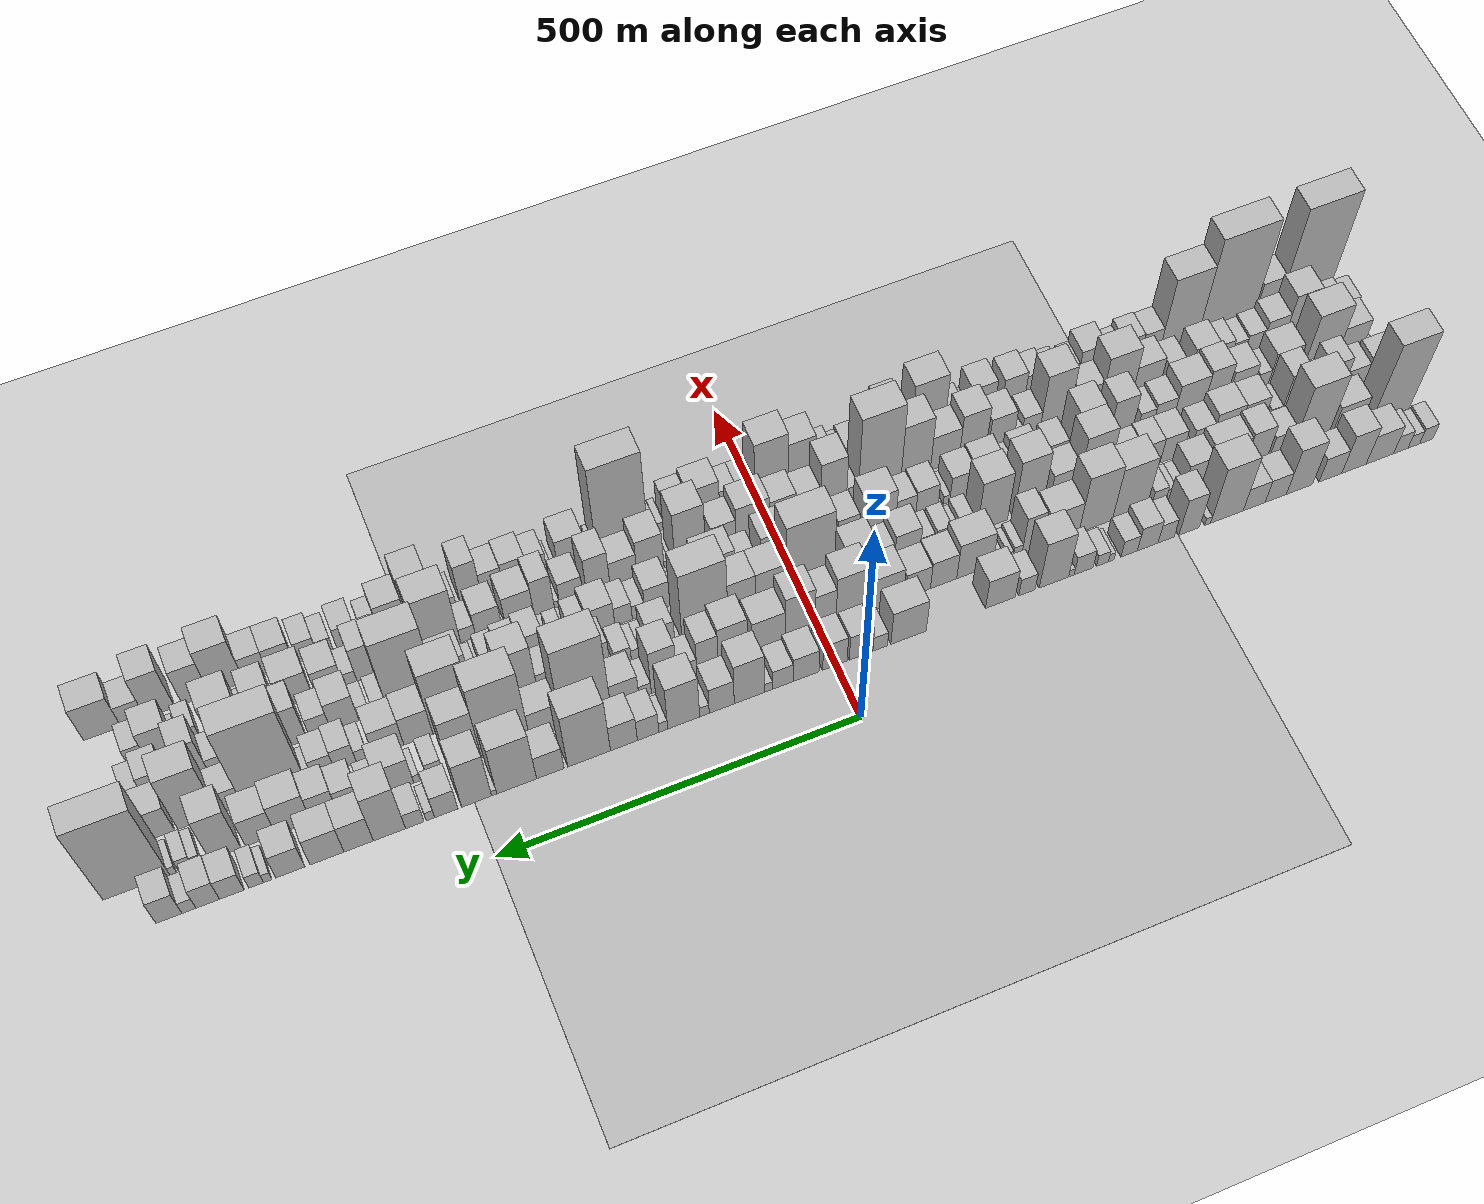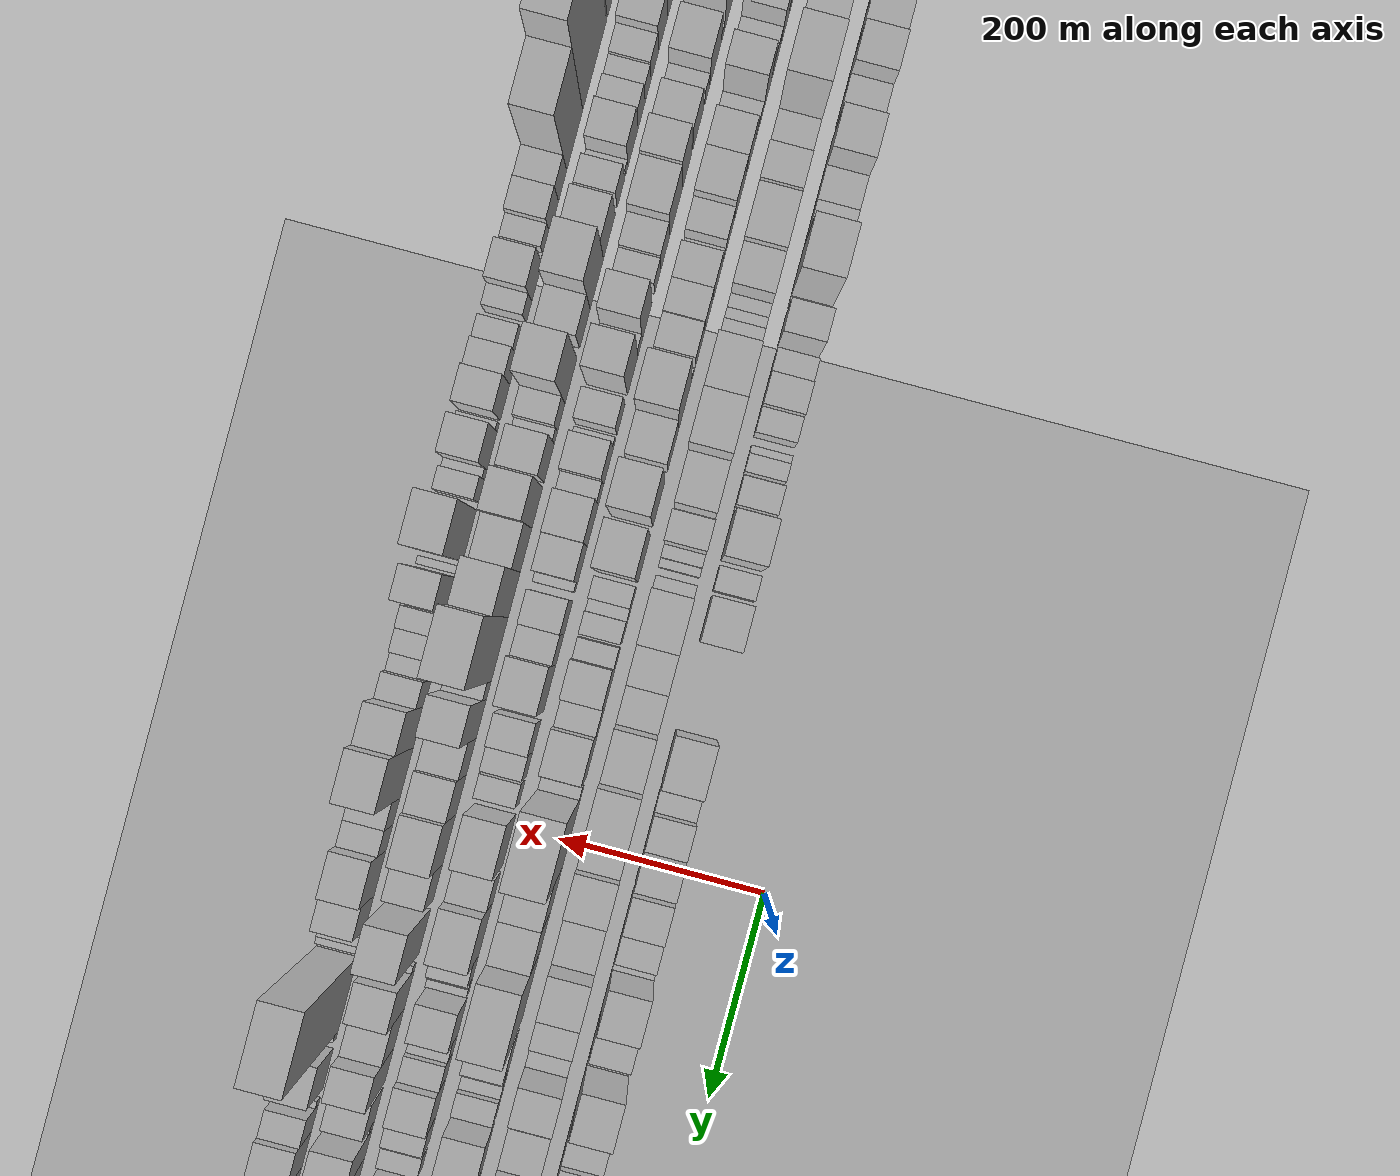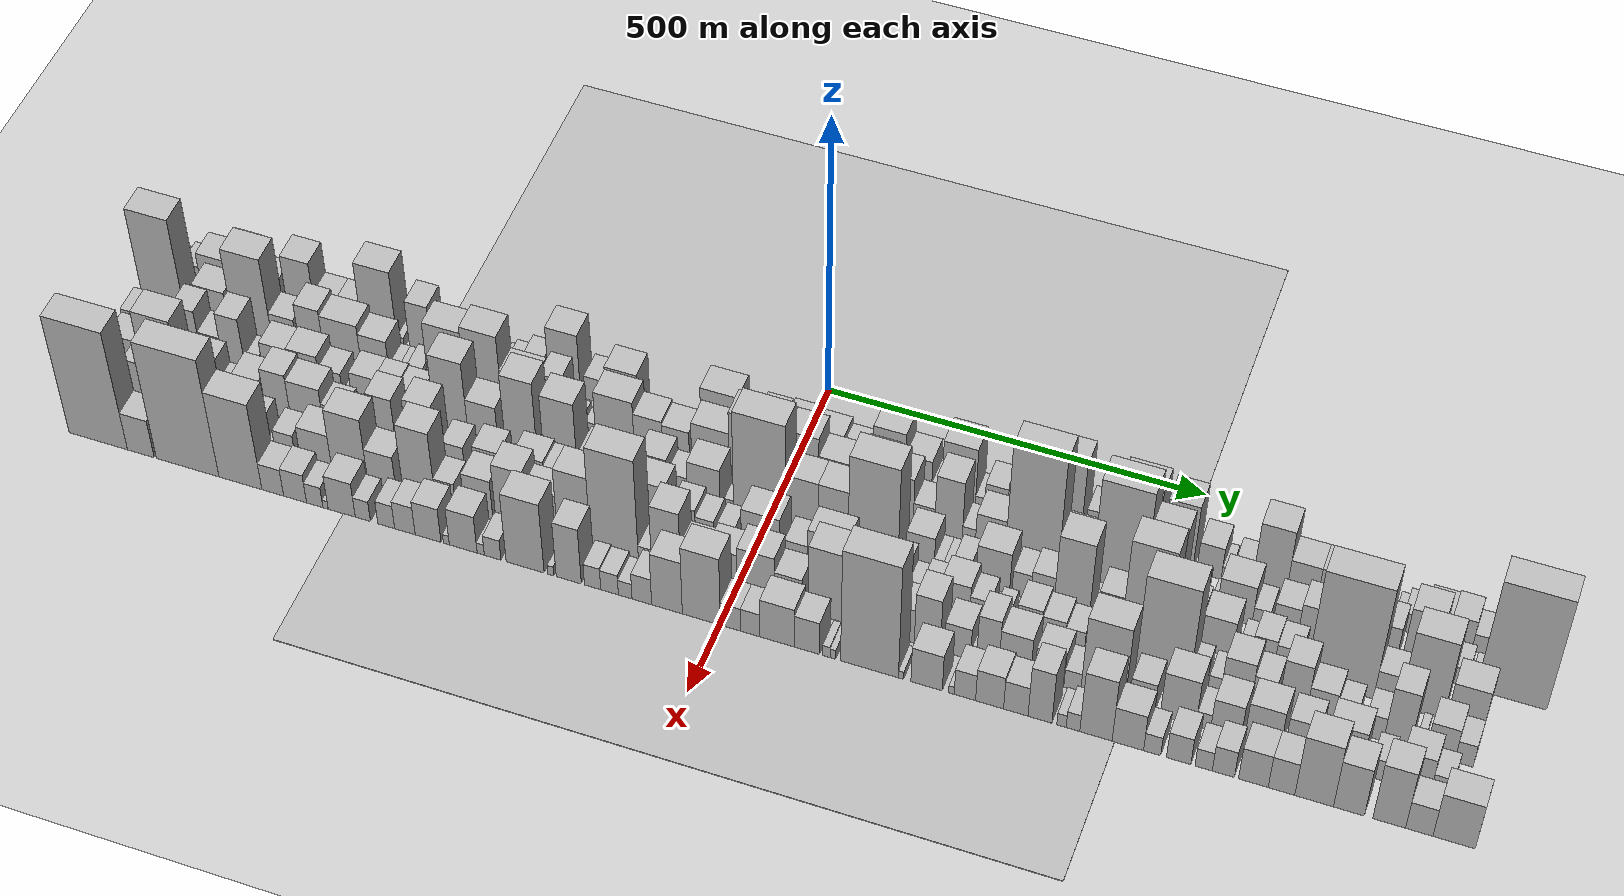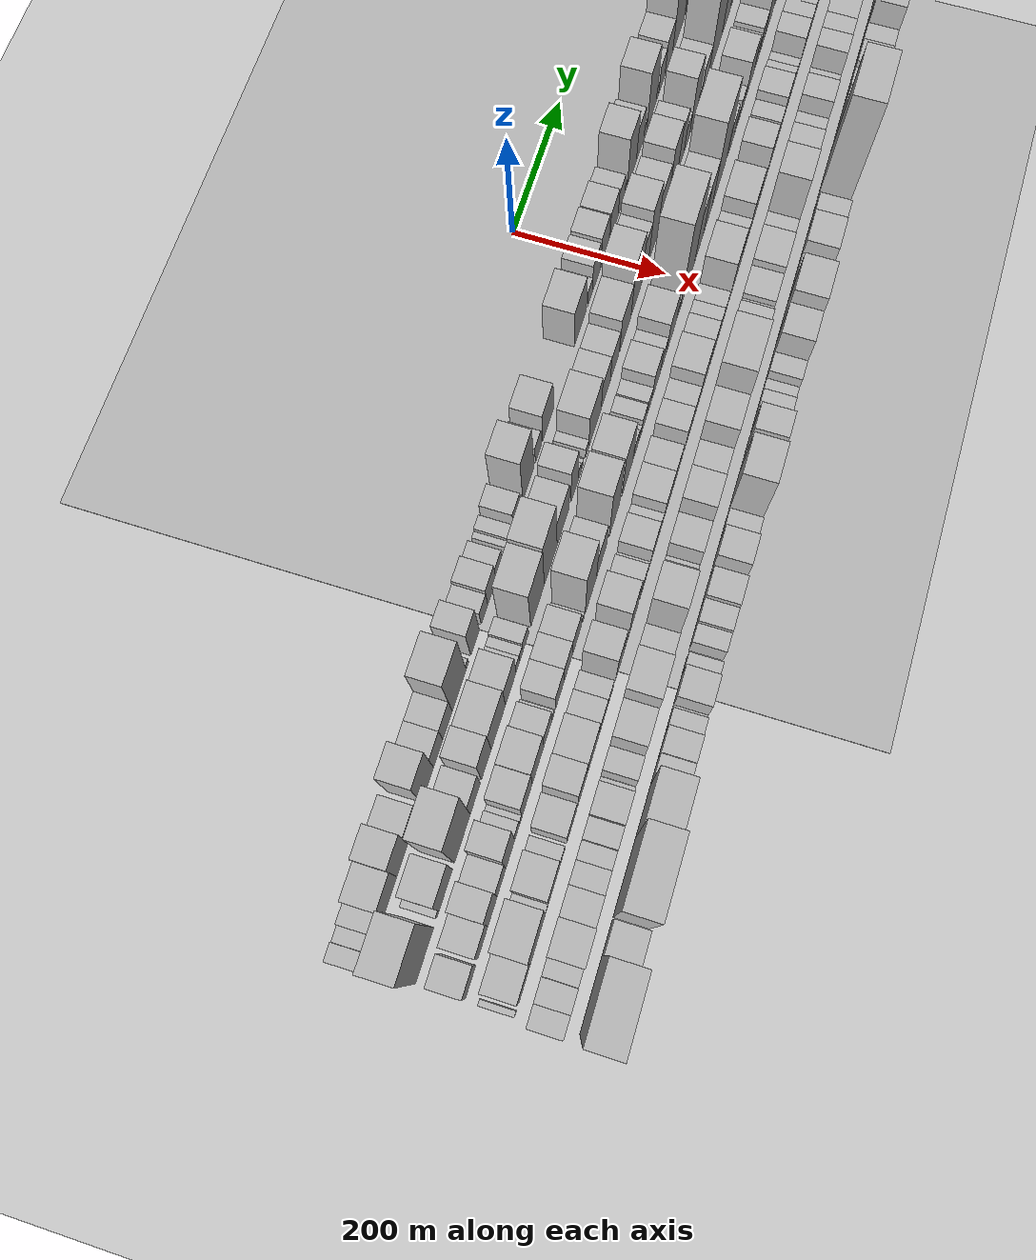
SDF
<?xml version="1.0" encoding="utf-8"?>

<sdf version="1.6">

   <world name="default">

      <gui fullscreen="0">

         <camera name="user_camera">

            <pose>-15 0 4.57585 0 0 0</pose>

            <view_controller>orbit</view_controller>

         </camera>

      </gui>

      <scene>

         <sky>

           <clouds>

             <speed>12</speed>

           </clouds>

         </sky>

         <ambient>0.4 0.4 0.4 1</ambient>

         <background>0.7 0.7 0.7 1</background>

         <shadows>1</shadows>

      </scene>

      <gravity>0 0 -9.8066</gravity>

      <magnetic_field>6e-06 2.3e-05 -4.2e-05</magnetic_field>

      <physics default="0" name="default_physics" type="ode">

         <ode>

            <solver>

               <type>quick</type>

               <iters>10</iters>

               <sor>1.0</sor>

               <use_dynamic_moi_rescaling>0</use_dynamic_moi_rescaling>

            </solver>

            <constraints>

               <cfm>0</cfm>

               <erp>0.2</erp>

               <contact_max_correcting_vel>100</contact_max_correcting_vel>

               <contact_surface_layer>0.001</contact_surface_layer>

            </constraints>

         </ode>

         <max_step_size>0.004</max_step_size>

         <real_time_factor>1</real_time_factor>

         <real_time_update_rate>250</real_time_update_rate>

      </physics>

      <light name="sun" type="directional">

         <cast_shadows>1</cast_shadows>

         <pose>0 0 10 0 0 0</pose>

         <diffuse>0.8 0.8 0.8 1</diffuse>

         <specular>0.2 0.2 0.2 1</specular>

         <attenuation>

            <range>1000</range>

            <constant>0.9</constant>

            <linear>0.01</linear>

            <quadratic>0.001</quadratic>

         </attenuation>

         <direction>-0.5 0.1 -0.9</direction>

      </light>

      <include>

         <name>ground_plane_1</name>

         <uri>model://HANNAS_ground_plane</uri>

         <pose>0 0 0  0 0 0</pose>

      </include>

      <include>

         <name>ground_plane_2</name>

         <uri>model://HANNAS_ground_plane</uri>

         <pose>100 0 0  0 0 0</pose>

      </include>

      <model name="building_1">

         <static>1</static>

         <pose frame="">100.0000 -879.7281 0 0.000000 0.000000 0.000000</pose>

         <link name="link">

            <pose frame="">0 0 19.50 0 0 0</pose>

            <collision name="collision">

               <geometry>

                  <box>

                     <size>40.0000 20.5438 39.0000</size>

                  </box>

               </geometry>

               <max_contacts>10</max_contacts>

               <surface>

                  <contact>

                     <ode/>

                  </contact>

                  <bounce/>

                  <friction>

                     <torsional>

                        <ode/>

                     </torsional>

                     <ode/>

                  </friction>

               </surface>

            </collision>

            <visual name="visual">

               <cast_shadows>0</cast_shadows>

               <geometry>

                  <box>

                     <size>40.0000 20.5438 39.0000</size>

                  </box>

               </geometry>

               <material>

                  <script>

                     <uri>model://HANNAS_wall/materials/scripts</uri>

                     <uri>model://HANNAS_wall/materials/textures</uri>

                     <name>vrc/HANNAS_wall</name>

                  </script>

               </material>

            </visual>

            <self_collide>0</self_collide>

            <enable_wind>0</enable_wind>

            <kinematic>0</kinematic>

         </link>

      </model>

      <model name="building_2">

         <static>1</static>

         <pose frame="">100.0000 -860.3485 0 0.000000 0.000000 0.000000</pose>

         <link name="link">

            <pose frame="">0 0 16.50 0 0 0</pose>

            <collision name="collision">

               <geometry>

                  <box>

                     <size>40.0000 18.2153 33.0000</size>

                  </box>

               </geometry>

               <max_contacts>10</max_contacts>

               <surface>

                  <contact>

                     <ode/>

                  </contact>

                  <bounce/>

                  <friction>

                     <torsional>

                        <ode/>

                     </torsional>

                     <ode/>

                  </friction>

               </surface>

            </collision>

            <visual name="visual">

               <cast_shadows>0</cast_shadows>

               <geometry>

                  <box>

                     <size>40.0000 18.2153 33.0000</size>

                  </box>

               </geometry>

               <material>

                  <script>

                     <uri>model://HANNAS_wall/materials/scripts</uri>

                     <uri>model://HANNAS_wall/materials/textures</uri>

                     <name>vrc/HANNAS_wall</name>

                  </script>

               </material>

            </visual>

            <self_collide>0</self_collide>

            <enable_wind>0</enable_wind>

            <kinematic>0</kinematic>

         </link>

      </model>

      <model name="building_3">

         <static>1</static>

         <pose frame="">100.0000 -839.9267 0 0.000000 0.000000 0.000000</pose>

         <link name="link">

            <pose frame="">0 0 22.50 0 0 0</pose>

            <collision name="collision">

               <geometry>

                  <box>

                     <size>40.0000 22.6282 45.0000</size>

                  </box>

               </geometry>

               <max_contacts>10</max_contacts>

               <surface>

                  <contact>

                     <ode/>

                  </contact>

                  <bounce/>

                  <friction>

                     <torsional>

                        <ode/>

                     </torsional>

                     <ode/>

                  </friction>

               </surface>

            </collision>

            <visual name="visual">

               <cast_shadows>0</cast_shadows>

               <geometry>

                  <box>

                     <size>40.0000 22.6282 45.0000</size>

                  </box>

               </geometry>

               <material>

                  <script>

                     <uri>model://HANNAS_wall/materials/scripts</uri>

                     <uri>model://HANNAS_wall/materials/textures</uri>

                     <name>vrc/HANNAS_wall</name>

                  </script>

               </material>

            </visual>

            <self_collide>0</self_collide>

            <enable_wind>0</enable_wind>

            <kinematic>0</kinematic>

         </link>

      </model>

      <model name="building_4">

         <static>1</static>

         <pose frame="">100.0000 -807.4633 0 0.000000 0.000000 0.000000</pose>

         <link name="link">

            <pose frame="">0 0 36.00 0 0 0</pose>

            <collision name="collision">

               <geometry>

                  <box>

                     <size>40.0000 42.2987 72.0000</size>

                  </box>

               </geometry>

               <max_contacts>10</max_contacts>

               <surface>

                  <contact>

                     <ode/>

                  </contact>

                  <bounce/>

                  <friction>

                     <torsional>

                        <ode/>

                     </torsional>

                     <ode/>

                  </friction>

               </surface>

            </collision>

            <visual name="visual">

               <cast_shadows>0</cast_shadows>

               <geometry>

                  <box>

                     <size>40.0000 42.2987 72.0000</size>

                  </box>

               </geometry>

               <material>

                  <script>

                     <uri>model://HANNAS_wall/materials/scripts</uri>

                     <uri>model://HANNAS_wall/materials/textures</uri>

                     <name>vrc/HANNAS_wall</name>

                  </script>

               </material>

            </visual>

            <self_collide>0</self_collide>

            <enable_wind>0</enable_wind>

            <kinematic>0</kinematic>

         </link>

      </model>

      <model name="building_5">

         <static>1</static>

         <pose frame="">100.0000 -767.4457 0 0.000000 0.000000 0.000000</pose>

         <link name="link">

            <pose frame="">0 0 48.00 0 0 0</pose>

            <collision name="collision">

               <geometry>

                  <box>

                     <size>40.0000 37.7364 96.0000</size>

                  </box>

               </geometry>

               <max_contacts>10</max_contacts>

               <surface>

                  <contact>

                     <ode/>

                  </contact>

                  <bounce/>

                  <friction>

                     <torsional>

                        <ode/>

                     </torsional>

                     <ode/>

                  </friction>

               </surface>

            </collision>

            <visual name="visual">

               <cast_shadows>0</cast_shadows>

               <geometry>

                  <box>

                     <size>40.0000 37.7364 96.0000</size>

                  </box>

               </geometry>

               <material>

                  <script>

                     <uri>model://HANNAS_wall/materials/scripts</uri>

                     <uri>model://HANNAS_wall/materials/textures</uri>

                     <name>vrc/HANNAS_wall</name>

                  </script>

               </material>

            </visual>

            <self_collide>0</self_collide>

            <enable_wind>0</enable_wind>

            <kinematic>0</kinematic>

         </link>

      </model>

      <model name="building_6">

         <static>1</static>

         <pose frame="">100.0000 -731.1510 0 0.000000 0.000000 0.000000</pose>

         <link name="link">

            <pose frame="">0 0 30.00 0 0 0</pose>

            <collision name="collision">

               <geometry>

                  <box>

                     <size>40.0000 34.8529 60.0000</size>

                  </box>

               </geometry>

               <max_contacts>10</max_contacts>

               <surface>

                  <contact>

                     <ode/>

                  </contact>

                  <bounce/>

                  <friction>

                     <torsional>

                        <ode/>

                     </torsional>

                     <ode/>

                  </friction>

               </surface>

            </collision>

            <visual name="visual">

               <cast_shadows>0</cast_shadows>

               <geometry>

                  <box>

                     <size>40.0000 34.8529 60.0000</size>

                  </box>

               </geometry>

               <material>

                  <script>

                     <uri>model://HANNAS_wall/materials/scripts</uri>

                     <uri>model://HANNAS_wall/materials/textures</uri>

                     <name>vrc/HANNAS_wall</name>

                  </script>

               </material>

            </visual>

            <self_collide>0</self_collide>

            <enable_wind>0</enable_wind>

            <kinematic>0</kinematic>

         </link>

      </model>

      <model name="building_7">

         <static>1</static>

         <pose frame="">100.0000 -683.6892 0 0.000000 0.000000 0.000000</pose>

         <link name="link">

            <pose frame="">0 0 57.00 0 0 0</pose>

            <collision name="collision">

               <geometry>

                  <box>

                     <size>40.0000 40.0708 114.0000</size>

                  </box>

               </geometry>

               <max_contacts>10</max_contacts>

               <surface>

                  <contact>

                     <ode/>

                  </contact>

                  <bounce/>

                  <friction>

                     <torsional>

                        <ode/>

                     </torsional>

                     <ode/>

                  </friction>

               </surface>

            </collision>

            <visual name="visual">

               <cast_shadows>0</cast_shadows>

               <geometry>

                  <box>

                     <size>40.0000 40.0708 114.0000</size>

                  </box>

               </geometry>

               <material>

                  <script>

                     <uri>model://HANNAS_wall/materials/scripts</uri>

                     <uri>model://HANNAS_wall/materials/textures</uri>

                     <name>vrc/HANNAS_wall</name>

                  </script>

               </material>

            </visual>

            <self_collide>0</self_collide>

            <enable_wind>0</enable_wind>

            <kinematic>0</kinematic>

         </link>

      </model>

      <model name="building_8">

         <static>1</static>

         <pose frame="">100.0000 -647.4908 0 0.000000 0.000000 0.000000</pose>

         <link name="link">

            <pose frame="">0 0 28.50 0 0 0</pose>

            <collision name="collision">

               <geometry>

                  <box>

                     <size>40.0000 32.3261 57.0000</size>

                  </box>

               </geometry>

               <max_contacts>10</max_contacts>

               <surface>

                  <contact>

                     <ode/>

                  </contact>

                  <bounce/>

                  <friction>

                     <torsional>

                        <ode/>

                     </torsional>

                     <ode/>

                  </friction>

               </surface>

            </collision>

            <visual name="visual">

               <cast_shadows>0</cast_shadows>

               <geometry>

                  <box>

                     <size>40.0000 32.3261 57.0000</size>

                  </box>

               </geometry>

               <material>

                  <script>

                     <uri>model://HANNAS_wall/materials/scripts</uri>

                     <uri>model://HANNAS_wall/materials/textures</uri>

                     <name>vrc/HANNAS_wall</name>

                  </script>

               </material>

            </visual>

            <self_collide>0</self_collide>

            <enable_wind>0</enable_wind>

            <kinematic>0</kinematic>

         </link>

      </model>

      <model name="building_9">

         <static>1</static>

         <pose frame="">100.0000 -614.7008 0 0.000000 0.000000 0.000000</pose>

         <link name="link">

            <pose frame="">0 0 28.50 0 0 0</pose>

            <collision name="collision">

               <geometry>

                  <box>

                     <size>40.0000 33.2538 57.0000</size>

                  </box>

               </geometry>

               <max_contacts>10</max_contacts>

               <surface>

                  <contact>

                     <ode/>

                  </contact>

                  <bounce/>

                  <friction>

                     <torsional>

                        <ode/>

                     </torsional>

                     <ode/>

                  </friction>

               </surface>

            </collision>

            <visual name="visual">

               <cast_shadows>0</cast_shadows>

               <geometry>

                  <box>

                     <size>40.0000 33.2538 57.0000</size>

                  </box>

               </geometry>

               <material>

                  <script>

                     <uri>model://HANNAS_wall/materials/scripts</uri>

                     <uri>model://HANNAS_wall/materials/textures</uri>

                     <name>vrc/HANNAS_wall</name>

                  </script>

               </material>

            </visual>

            <self_collide>0</self_collide>

            <enable_wind>0</enable_wind>

            <kinematic>0</kinematic>

         </link>

      </model>

      <model name="building_10">

         <static>1</static>

         <pose frame="">100.0000 -573.3062 0 0.000000 0.000000 0.000000</pose>

         <link name="link">

            <pose frame="">0 0 70.50 0 0 0</pose>

            <collision name="collision">

               <geometry>

                  <box>

                     <size>40.0000 49.5353 141.0000</size>

                  </box>

               </geometry>

               <max_contacts>10</max_contacts>

               <surface>

                  <contact>

                     <ode/>

                  </contact>

                  <bounce/>

                  <friction>

                     <torsional>

                        <ode/>

                     </torsional>

                     <ode/>

                  </friction>

               </surface>

            </collision>

            <visual name="visual">

               <cast_shadows>0</cast_shadows>

               <geometry>

                  <box>

                     <size>40.0000 49.5353 141.0000</size>

                  </box>

               </geometry>

               <material>

                  <script>

                     <uri>model://HANNAS_wall/materials/scripts</uri>

                     <uri>model://HANNAS_wall/materials/textures</uri>

                     <name>vrc/HANNAS_wall</name>

                  </script>

               </material>

            </visual>

            <self_collide>0</self_collide>

            <enable_wind>0</enable_wind>

            <kinematic>0</kinematic>

         </link>

      </model>

      <model name="building_11">

         <static>1</static>

         <pose frame="">100.0000 -544.0786 0 0.000000 0.000000 0.000000</pose>

         <link name="link">

            <pose frame="">0 0 9.00 0 0 0</pose>

            <collision name="collision">

               <geometry>

                  <box>

                     <size>40.0000 8.9200 18.0000</size>

                  </box>

               </geometry>

               <max_contacts>10</max_contacts>

               <surface>

                  <contact>

                     <ode/>

                  </contact>

                  <bounce/>

                  <friction>

                     <torsional>

                        <ode/>

                     </torsional>

                     <ode/>

                  </friction>

               </surface>

            </collision>

            <visual name="visual">

               <cast_shadows>0</cast_shadows>

               <geometry>

                  <box>

                     <size>40.0000 8.9200 18.0000</size>

                  </box>

               </geometry>

               <material>

                  <script>

                     <uri>model://HANNAS_wall/materials/scripts</uri>

                     <uri>model://HANNAS_wall/materials/textures</uri>

                     <name>vrc/HANNAS_wall</name>

                  </script>

               </material>

            </visual>

            <self_collide>0</self_collide>

            <enable_wind>0</enable_wind>

            <kinematic>0</kinematic>

         </link>

      </model>

      <model name="building_12">

         <static>1</static>

         <pose frame="">100.0000 -516.1670 0 0.000000 0.000000 0.000000</pose>

         <link name="link">

            <pose frame="">0 0 46.50 0 0 0</pose>

            <collision name="collision">

               <geometry>

                  <box>

                     <size>40.0000 30.9031 93.0000</size>

                  </box>

               </geometry>

               <max_contacts>10</max_contacts>

               <surface>

                  <contact>

                     <ode/>

                  </contact>

                  <bounce/>

                  <friction>

                     <torsional>

                        <ode/>

                     </torsional>

                     <ode/>

                  </friction>

               </surface>

            </collision>

            <visual name="visual">

               <cast_shadows>0</cast_shadows>

               <geometry>

                  <box>

                     <size>40.0000 30.9031 93.0000</size>

                  </box>

               </geometry>

               <material>

                  <script>

                     <uri>model://HANNAS_wall/materials/scripts</uri>

                     <uri>model://HANNAS_wall/materials/textures</uri>

                     <name>vrc/HANNAS_wall</name>

                  </script>

               </material>

            </visual>

            <self_collide>0</self_collide>

            <enable_wind>0</enable_wind>

            <kinematic>0</kinematic>

         </link>

      </model>

      <model name="building_13">

         <static>1</static>

         <pose frame="">100.0000 -481.6354 0 0.000000 0.000000 0.000000</pose>

         <link name="link">

            <pose frame="">0 0 24.00 0 0 0</pose>

            <collision name="collision">

               <geometry>

                  <box>

                     <size>40.0000 24.1601 48.0000</size>

                  </box>

               </geometry>

               <max_contacts>10</max_contacts>

               <surface>

                  <contact>

                     <ode/>

                  </contact>

                  <bounce/>

                  <friction>

                     <torsional>

                        <ode/>

                     </torsional>

                     <ode/>

                  </friction>

               </surface>

            </collision>

            <visual name="visual">

               <cast_shadows>0</cast_shadows>

               <geometry>

                  <box>

                     <size>40.0000 24.1601 48.0000</size>

                  </box>

               </geometry>

               <material>

                  <script>

                     <uri>model://HANNAS_wall/materials/scripts</uri>

                     <uri>model://HANNAS_wall/materials/textures</uri>

                     <name>vrc/HANNAS_wall</name>

                  </script>

               </material>

            </visual>

            <self_collide>0</self_collide>

            <enable_wind>0</enable_wind>

            <kinematic>0</kinematic>

         </link>

      </model>

      <model name="building_14">

         <static>1</static>

         <pose frame="">100.0000 -454.1454 0 0.000000 0.000000 0.000000</pose>

         <link name="link">

            <pose frame="">0 0 30.00 0 0 0</pose>

            <collision name="collision">

               <geometry>

                  <box>

                     <size>40.0000 30.8198 60.0000</size>

                  </box>

               </geometry>

               <max_contacts>10</max_contacts>

               <surface>

                  <contact>

                     <ode/>

                  </contact>

                  <bounce/>

                  <friction>

                     <torsional>

                        <ode/>

                     </torsional>

                     <ode/>

                  </friction>

               </surface>

            </collision>

            <visual name="visual">

               <cast_shadows>0</cast_shadows>

               <geometry>

                  <box>

                     <size>40.0000 30.8198 60.0000</size>

                  </box>

               </geometry>

               <material>

                  <script>

                     <uri>model://HANNAS_wall/materials/scripts</uri>

                     <uri>model://HANNAS_wall/materials/textures</uri>

                     <name>vrc/HANNAS_wall</name>

                  </script>

               </material>

            </visual>

            <self_collide>0</self_collide>

            <enable_wind>0</enable_wind>

            <kinematic>0</kinematic>

         </link>

      </model>

      <model name="building_15">

         <static>1</static>

         <pose frame="">100.0000 -426.4296 0 0.000000 0.000000 0.000000</pose>

         <link name="link">

            <pose frame="">0 0 21.00 0 0 0</pose>

            <collision name="collision">

               <geometry>

                  <box>

                     <size>40.0000 24.6120 42.0000</size>

                  </box>

               </geometry>

               <max_contacts>10</max_contacts>

               <surface>

                  <contact>

                     <ode/>

                  </contact>

                  <bounce/>

                  <friction>

                     <torsional>

                        <ode/>

                     </torsional>

                     <ode/>

                  </friction>

               </surface>

            </collision>

            <visual name="visual">

               <cast_shadows>0</cast_shadows>

               <geometry>

                  <box>

                     <size>40.0000 24.6120 42.0000</size>

                  </box>

               </geometry>

               <material>

                  <script>

                     <uri>model://HANNAS_wall/materials/scripts</uri>

                     <uri>model://HANNAS_wall/materials/textures</uri>

                     <name>vrc/HANNAS_wall</name>

                  </script>

               </material>

            </visual>

            <self_collide>0</self_collide>

            <enable_wind>0</enable_wind>

            <kinematic>0</kinematic>

         </link>

      </model>

      <model name="building_16">

         <static>1</static>

         <pose frame="">100.0000 -399.9136 0 0.000000 0.000000 0.000000</pose>

         <link name="link">

            <pose frame="">0 0 10.50 0 0 0</pose>

            <collision name="collision">

               <geometry>

                  <box>

                     <size>40.0000 8.4200 21.0000</size>

                  </box>

               </geometry>

               <max_contacts>10</max_contacts>

               <surface>

                  <contact>

                     <ode/>

                  </contact>

                  <bounce/>

                  <friction>

                     <torsional>

                        <ode/>

                     </torsional>

                     <ode/>

                  </friction>

               </surface>

            </collision>

            <visual name="visual">

               <cast_shadows>0</cast_shadows>

               <geometry>

                  <box>

                     <size>40.0000 8.4200 21.0000</size>

                  </box>

               </geometry>

               <material>

                  <script>

                     <uri>model://HANNAS_wall/materials/scripts</uri>

                     <uri>model://HANNAS_wall/materials/textures</uri>

                     <name>vrc/HANNAS_wall</name>

                  </script>

               </material>

            </visual>

            <self_collide>0</self_collide>

            <enable_wind>0</enable_wind>

            <kinematic>0</kinematic>

         </link>

      </model>

      <model name="building_17">

         <static>1</static>

         <pose frame="">100.0000 -386.7798 0 0.000000 0.000000 0.000000</pose>

         <link name="link">

            <pose frame="">0 0 15.00 0 0 0</pose>

            <collision name="collision">

               <geometry>

                  <box>

                     <size>40.0000 17.8474 30.0000</size>

                  </box>

               </geometry>

               <max_contacts>10</max_contacts>

               <surface>

                  <contact>

                     <ode/>

                  </contact>

                  <bounce/>

                  <friction>

                     <torsional>

                        <ode/>

                     </torsional>

                     <ode/>

                  </friction>

               </surface>

            </collision>

            <visual name="visual">

               <cast_shadows>0</cast_shadows>

               <geometry>

                  <box>

                     <size>40.0000 17.8474 30.0000</size>

                  </box>

               </geometry>

               <material>

                  <script>

                     <uri>model://HANNAS_wall/materials/scripts</uri>

                     <uri>model://HANNAS_wall/materials/textures</uri>

                     <name>vrc/HANNAS_wall</name>

                  </script>

               </material>

            </visual>

            <self_collide>0</self_collide>

            <enable_wind>0</enable_wind>

            <kinematic>0</kinematic>

         </link>

      </model>

      <model name="building_18">

         <static>1</static>

         <pose frame="">100.0000 -358.8407 0 0.000000 0.000000 0.000000</pose>

         <link name="link">

            <pose frame="">0 0 24.00 0 0 0</pose>

            <collision name="collision">

               <geometry>

                  <box>

                     <size>40.0000 28.0308 48.0000</size>

                  </box>

               </geometry>

               <max_contacts>10</max_contacts>

               <surface>

                  <contact>

                     <ode/>

                  </contact>

                  <bounce/>

                  <friction>

                     <torsional>

                        <ode/>

                     </torsional>

                     <ode/>

                  </friction>

               </surface>

            </collision>

            <visual name="visual">

               <cast_shadows>0</cast_shadows>

               <geometry>

                  <box>

                     <size>40.0000 28.0308 48.0000</size>

                  </box>

               </geometry>

               <material>

                  <script>

                     <uri>model://HANNAS_wall/materials/scripts</uri>

                     <uri>model://HANNAS_wall/materials/textures</uri>

                     <name>vrc/HANNAS_wall</name>

                  </script>

               </material>

            </visual>

            <self_collide>0</self_collide>

            <enable_wind>0</enable_wind>

            <kinematic>0</kinematic>

         </link>

      </model>

      <model name="building_19">

         <static>1</static>

         <pose frame="">100.0000 -340.6961 0 0.000000 0.000000 0.000000</pose>

         <link name="link">

            <pose frame="">0 0 9.00 0 0 0</pose>

            <collision name="collision">

               <geometry>

                  <box>

                     <size>40.0000 8.2584 18.0000</size>

                  </box>

               </geometry>

               <max_contacts>10</max_contacts>

               <surface>

                  <contact>

                     <ode/>

                  </contact>

                  <bounce/>

                  <friction>

                     <torsional>

                        <ode/>

                     </torsional>

                     <ode/>

                  </friction>

               </surface>

            </collision>

            <visual name="visual">

               <cast_shadows>0</cast_shadows>

               <geometry>

                  <box>

                     <size>40.0000 8.2584 18.0000</size>

                  </box>

               </geometry>

               <material>

                  <script>

                     <uri>model://HANNAS_wall/materials/scripts</uri>

                     <uri>model://HANNAS_wall/materials/textures</uri>

                     <name>vrc/HANNAS_wall</name>

                  </script>

               </material>

            </visual>

            <self_collide>0</self_collide>

            <enable_wind>0</enable_wind>

            <kinematic>0</kinematic>

         </link>

      </model>

      <model name="building_20">

         <static>1</static>

         <pose frame="">100.0000 -314.9943 0 0.000000 0.000000 0.000000</pose>

         <link name="link">

            <pose frame="">0 0 60.00 0 0 0</pose>

            <collision name="collision">

               <geometry>

                  <box>

                     <size>40.0000 43.1453 120.0000</size>

                  </box>

               </geometry>

               <max_contacts>10</max_contacts>

               <surface>

                  <contact>

                     <ode/>

                  </contact>

                  <bounce/>

                  <friction>

                     <torsional>

                        <ode/>

                     </torsional>

                     <ode/>

                  </friction>

               </surface>

            </collision>

            <visual name="visual">

               <cast_shadows>0</cast_shadows>

               <geometry>

                  <box>

                     <size>40.0000 43.1453 120.0000</size>

                  </box>

               </geometry>

               <material>

                  <script>

                     <uri>model://HANNAS_wall/materials/scripts</uri>

                     <uri>model://HANNAS_wall/materials/textures</uri>

                     <name>vrc/HANNAS_wall</name>

                  </script>

               </material>

            </visual>

            <self_collide>0</self_collide>

            <enable_wind>0</enable_wind>

            <kinematic>0</kinematic>

         </link>

      </model>

      <model name="building_21">

         <static>1</static>

         <pose frame="">100.0000 -275.4120 0 0.000000 0.000000 0.000000</pose>

         <link name="link">

            <pose frame="">0 0 22.50 0 0 0</pose>

            <collision name="collision">

               <geometry>

                  <box>

                     <size>40.0000 24.0193 45.0000</size>

                  </box>

               </geometry>

               <max_contacts>10</max_contacts>

               <surface>

                  <contact>

                     <ode/>

                  </contact>

                  <bounce/>

                  <friction>

                     <torsional>

                        <ode/>

                     </torsional>

                     <ode/>

                  </friction>

               </surface>

            </collision>

            <visual name="visual">

               <cast_shadows>0</cast_shadows>

               <geometry>

                  <box>

                     <size>40.0000 24.0193 45.0000</size>

                  </box>

               </geometry>

               <material>

                  <script>

                     <uri>model://HANNAS_wall/materials/scripts</uri>

                     <uri>model://HANNAS_wall/materials/textures</uri>

                     <name>vrc/HANNAS_wall</name>

                  </script>

               </material>

            </visual>

            <self_collide>0</self_collide>

            <enable_wind>0</enable_wind>

            <kinematic>0</kinematic>

         </link>

      </model>

      <model name="building_22">

         <static>1</static>

         <pose frame="">100.0000 -236.6050 0 0.000000 0.000000 0.000000</pose>

         <link name="link">

            <pose frame="">0 0 37.50 0 0 0</pose>

            <collision name="collision">

               <geometry>

                  <box>

                     <size>40.0000 43.5947 75.0000</size>

                  </box>

               </geometry>

               <max_contacts>10</max_contacts>

               <surface>

                  <contact>

                     <ode/>

                  </contact>

                  <bounce/>

                  <friction>

                     <torsional>

                        <ode/>

                     </torsional>

                     <ode/>

                  </friction>

               </surface>

            </collision>

            <visual name="visual">

               <cast_shadows>0</cast_shadows>

               <geometry>

                  <box>

                     <size>40.0000 43.5947 75.0000</size>

                  </box>

               </geometry>

               <material>

                  <script>

                     <uri>model://HANNAS_wall/materials/scripts</uri>

                     <uri>model://HANNAS_wall/materials/textures</uri>

                     <name>vrc/HANNAS_wall</name>

                  </script>

               </material>

            </visual>

            <self_collide>0</self_collide>

            <enable_wind>0</enable_wind>

            <kinematic>0</kinematic>

         </link>

      </model>

      <model name="building_23">

         <static>1</static>

         <pose frame="">100.0000 -103.5730 0 0.000000 0.000000 0.000000</pose>

         <link name="link">

            <pose frame="">0 0 43.50 0 0 0</pose>

            <collision name="collision">

               <geometry>

                  <box>

                     <size>40.0000 50.8231 87.0000</size>

                  </box>

               </geometry>

               <max_contacts>10</max_contacts>

               <surface>

                  <contact>

                     <ode/>

                  </contact>

                  <bounce/>

                  <friction>

                     <torsional>

                        <ode/>

                     </torsional>

                     <ode/>

                  </friction>

               </surface>

            </collision>

            <visual name="visual">

               <cast_shadows>0</cast_shadows>

               <geometry>

                  <box>

                     <size>40.0000 50.8231 87.0000</size>

                  </box>

               </geometry>

               <material>

                  <script>

                     <uri>model://HANNAS_wall/materials/scripts</uri>

                     <uri>model://HANNAS_wall/materials/textures</uri>

                     <name>vrc/HANNAS_wall</name>

                  </script>

               </material>

            </visual>

            <self_collide>0</self_collide>

            <enable_wind>0</enable_wind>

            <kinematic>0</kinematic>

         </link>

      </model>

      <model name="building_24">

         <static>1</static>

         <pose frame="">100.0000 -62.7627 0 0.000000 0.000000 0.000000</pose>

         <link name="link">

            <pose frame="">0 0 19.50 0 0 0</pose>

            <collision name="collision">

               <geometry>

                  <box>

                     <size>40.0000 20.7975 39.0000</size>

                  </box>

               </geometry>

               <max_contacts>10</max_contacts>

               <surface>

                  <contact>

                     <ode/>

                  </contact>

                  <bounce/>

                  <friction>

                     <torsional>

                        <ode/>

                     </torsional>

                     <ode/>

                  </friction>

               </surface>

            </collision>

            <visual name="visual">

               <cast_shadows>0</cast_shadows>

               <geometry>

                  <box>

                     <size>40.0000 20.7975 39.0000</size>

                  </box>

               </geometry>

               <material>

                  <script>

                     <uri>model://HANNAS_wall/materials/scripts</uri>

                     <uri>model://HANNAS_wall/materials/textures</uri>

                     <name>vrc/HANNAS_wall</name>

                  </script>

               </material>

            </visual>

            <self_collide>0</self_collide>

            <enable_wind>0</enable_wind>

            <kinematic>0</kinematic>

         </link>

      </model>

      <model name="building_25">

         <static>1</static>

         <pose frame="">100.0000 -35.5092 0 0.000000 0.000000 0.000000</pose>

         <link name="link">

            <pose frame="">0 0 33.00 0 0 0</pose>

            <collision name="collision">

               <geometry>

                  <box>

                     <size>40.0000 33.7094 66.0000</size>

                  </box>

               </geometry>

               <max_contacts>10</max_contacts>

               <surface>

                  <contact>

                     <ode/>

                  </contact>

                  <bounce/>

                  <friction>

                     <torsional>

                        <ode/>

                     </torsional>

                     <ode/>

                  </friction>

               </surface>

            </collision>

            <visual name="visual">

               <cast_shadows>0</cast_shadows>

               <geometry>

                  <box>

                     <size>40.0000 33.7094 66.0000</size>

                  </box>

               </geometry>

               <material>

                  <script>

                     <uri>model://HANNAS_wall/materials/scripts</uri>

                     <uri>model://HANNAS_wall/materials/textures</uri>

                     <name>vrc/HANNAS_wall</name>

                  </script>

               </material>

            </visual>

            <self_collide>0</self_collide>

            <enable_wind>0</enable_wind>

            <kinematic>0</kinematic>

         </link>

      </model>

      <model name="building_26">

         <static>1</static>

         <pose frame="">100.0000 1.7583 0 0.000000 0.000000 0.000000</pose>

         <link name="link">

            <pose frame="">0 0 34.50 0 0 0</pose>

            <collision name="collision">

               <geometry>

                  <box>

                     <size>40.0000 34.8256 69.0000</size>

                  </box>

               </geometry>

               <max_contacts>10</max_contacts>

               <surface>

                  <contact>

                     <ode/>

                  </contact>

                  <bounce/>

                  <friction>

                     <torsional>

                        <ode/>

                     </torsional>

                     <ode/>

                  </friction>

               </surface>

            </collision>

            <visual name="visual">

               <cast_shadows>0</cast_shadows>

               <geometry>

                  <box>

                     <size>40.0000 34.8256 69.0000</size>

                  </box>

               </geometry>

               <material>

                  <script>

                     <uri>model://HANNAS_wall/materials/scripts</uri>

                     <uri>model://HANNAS_wall/materials/textures</uri>

                     <name>vrc/HANNAS_wall</name>

                  </script>

               </material>

            </visual>

            <self_collide>0</self_collide>

            <enable_wind>0</enable_wind>

            <kinematic>0</kinematic>

         </link>

      </model>

      <model name="building_27">

         <static>1</static>

         <pose frame="">100.0000 42.5124 0 0.000000 0.000000 0.000000</pose>

         <link name="link">

            <pose frame="">0 0 31.50 0 0 0</pose>

            <collision name="collision">

               <geometry>

                  <box>

                     <size>40.0000 36.6826 63.0000</size>

                  </box>

               </geometry>

               <max_contacts>10</max_contacts>

               <surface>

                  <contact>

                     <ode/>

                  </contact>

                  <bounce/>

                  <friction>

                     <torsional>

                        <ode/>

                     </torsional>

                     <ode/>

                  </friction>

               </surface>

            </collision>

            <visual name="visual">

               <cast_shadows>0</cast_shadows>

               <geometry>

                  <box>

                     <size>40.0000 36.6826 63.0000</size>

                  </box>

               </geometry>

               <material>

                  <script>

                     <uri>model://HANNAS_wall/materials/scripts</uri>

                     <uri>model://HANNAS_wall/materials/textures</uri>

                     <name>vrc/HANNAS_wall</name>

                  </script>

               </material>

            </visual>

            <self_collide>0</self_collide>

            <enable_wind>0</enable_wind>

            <kinematic>0</kinematic>

         </link>

      </model>

      <model name="building_28">

         <static>1</static>

         <pose frame="">100.0000 75.3512 0 0.000000 0.000000 0.000000</pose>

         <link name="link">

            <pose frame="">0 0 25.50 0 0 0</pose>

            <collision name="collision">

               <geometry>

                  <box>

                     <size>40.0000 28.9949 51.0000</size>

                  </box>

               </geometry>

               <max_contacts>10</max_contacts>

               <surface>

                  <contact>

                     <ode/>

                  </contact>

                  <bounce/>

                  <friction>

                     <torsional>

                        <ode/>

                     </torsional>

                     <ode/>

                  </friction>

               </surface>

            </collision>

            <visual name="visual">

               <cast_shadows>0</cast_shadows>

               <geometry>

                  <box>

                     <size>40.0000 28.9949 51.0000</size>

                  </box>

               </geometry>

               <material>

                  <script>

                     <uri>model://HANNAS_wall/materials/scripts</uri>

                     <uri>model://HANNAS_wall/materials/textures</uri>

                     <name>vrc/HANNAS_wall</name>

                  </script>

               </material>

            </visual>

            <self_collide>0</self_collide>

            <enable_wind>0</enable_wind>

            <kinematic>0</kinematic>

         </link>

      </model>

      <model name="building_29">

         <static>1</static>

         <pose frame="">100.0000 95.3679 0 0.000000 0.000000 0.000000</pose>

         <link name="link">

            <pose frame="">0 0 12.00 0 0 0</pose>

            <collision name="collision">

               <geometry>

                  <box>

                     <size>40.0000 11.0385 24.0000</size>

                  </box>

               </geometry>

               <max_contacts>10</max_contacts>

               <surface>

                  <contact>

                     <ode/>

                  </contact>

                  <bounce/>

                  <friction>

                     <torsional>

                        <ode/>

                     </torsional>

                     <ode/>

                  </friction>

               </surface>

            </collision>

            <visual name="visual">

               <cast_shadows>0</cast_shadows>

               <geometry>

                  <box>

                     <size>40.0000 11.0385 24.0000</size>

                  </box>

               </geometry>

               <material>

                  <script>

                     <uri>model://HANNAS_wall/materials/scripts</uri>

                     <uri>model://HANNAS_wall/materials/textures</uri>

                     <name>vrc/HANNAS_wall</name>

                  </script>

               </material>

            </visual>

            <self_collide>0</self_collide>

            <enable_wind>0</enable_wind>

            <kinematic>0</kinematic>

         </link>

      </model>

      <model name="building_30">

         <static>1</static>

         <pose frame="">100.0000 122.2510 0 0.000000 0.000000 0.000000</pose>

         <link name="link">

            <pose frame="">0 0 54.00 0 0 0</pose>

            <collision name="collision">

               <geometry>

                  <box>

                     <size>40.0000 42.7277 108.0000</size>

                  </box>

               </geometry>

               <max_contacts>10</max_contacts>

               <surface>

                  <contact>

                     <ode/>

                  </contact>

                  <bounce/>

                  <friction>

                     <torsional>

                        <ode/>

                     </torsional>

                     <ode/>

                  </friction>

               </surface>

            </collision>

            <visual name="visual">

               <cast_shadows>0</cast_shadows>

               <geometry>

                  <box>

                     <size>40.0000 42.7277 108.0000</size>

                  </box>

               </geometry>

               <material>

                  <script>

                     <uri>model://HANNAS_wall/materials/scripts</uri>

                     <uri>model://HANNAS_wall/materials/textures</uri>

                     <name>vrc/HANNAS_wall</name>

                  </script>

               </material>

            </visual>

            <self_collide>0</self_collide>

            <enable_wind>0</enable_wind>

            <kinematic>0</kinematic>

         </link>

      </model>

      <model name="building_31">

         <static>1</static>

         <pose frame="">100.0000 161.0687 0 0.000000 0.000000 0.000000</pose>

         <link name="link">

            <pose frame="">0 0 34.50 0 0 0</pose>

            <collision name="collision">

               <geometry>

                  <box>

                     <size>40.0000 34.9078 69.0000</size>

                  </box>

               </geometry>

               <max_contacts>10</max_contacts>

               <surface>

                  <contact>

                     <ode/>

                  </contact>

                  <bounce/>

                  <friction>

                     <torsional>

                        <ode/>

                     </torsional>

                     <ode/>

                  </friction>

               </surface>

            </collision>

            <visual name="visual">

               <cast_shadows>0</cast_shadows>

               <geometry>

                  <box>

                     <size>40.0000 34.9078 69.0000</size>

                  </box>

               </geometry>

               <material>

                  <script>

                     <uri>model://HANNAS_wall/materials/scripts</uri>

                     <uri>model://HANNAS_wall/materials/textures</uri>

                     <name>vrc/HANNAS_wall</name>

                  </script>

               </material>

            </visual>

            <self_collide>0</self_collide>

            <enable_wind>0</enable_wind>

            <kinematic>0</kinematic>

         </link>

      </model>

      <model name="building_32">

         <static>1</static>

         <pose frame="">100.0000 185.1499 0 0.000000 0.000000 0.000000</pose>

         <link name="link">

            <pose frame="">0 0 13.50 0 0 0</pose>

            <collision name="collision">

               <geometry>

                  <box>

                     <size>40.0000 13.2545 27.0000</size>

                  </box>

               </geometry>

               <max_contacts>10</max_contacts>

               <surface>

                  <contact>

                     <ode/>

                  </contact>

                  <bounce/>

                  <friction>

                     <torsional>

                        <ode/>

                     </torsional>

                     <ode/>

                  </friction>

               </surface>

            </collision>

            <visual name="visual">

               <cast_shadows>0</cast_shadows>

               <geometry>

                  <box>

                     <size>40.0000 13.2545 27.0000</size>

                  </box>

               </geometry>

               <material>

                  <script>

                     <uri>model://HANNAS_wall/materials/scripts</uri>

                     <uri>model://HANNAS_wall/materials/textures</uri>

                     <name>vrc/HANNAS_wall</name>

                  </script>

               </material>

            </visual>

            <self_collide>0</self_collide>

            <enable_wind>0</enable_wind>

            <kinematic>0</kinematic>

         </link>

      </model>

      <model name="building_33">

         <static>1</static>

         <pose frame="">100.0000 213.9321 0 0.000000 0.000000 0.000000</pose>

         <link name="link">

            <pose frame="">0 0 58.50 0 0 0</pose>

            <collision name="collision">

               <geometry>

                  <box>

                     <size>40.0000 44.3101 117.0000</size>

                  </box>

               </geometry>

               <max_contacts>10</max_contacts>

               <surface>

                  <contact>

                     <ode/>

                  </contact>

                  <bounce/>

                  <friction>

                     <torsional>

                        <ode/>

                     </torsional>

                     <ode/>

                  </friction>

               </surface>

            </collision>

            <visual name="visual">

               <cast_shadows>0</cast_shadows>

               <geometry>

                  <box>

                     <size>40.0000 44.3101 117.0000</size>

                  </box>

               </geometry>

               <material>

                  <script>

                     <uri>model://HANNAS_wall/materials/scripts</uri>

                     <uri>model://HANNAS_wall/materials/textures</uri>

                     <name>vrc/HANNAS_wall</name>

                  </script>

               </material>

            </visual>

            <self_collide>0</self_collide>

            <enable_wind>0</enable_wind>

            <kinematic>0</kinematic>

         </link>

      </model>

      <model name="building_34">

         <static>1</static>

         <pose frame="">100.0000 242.2070 0 0.000000 0.000000 0.000000</pose>

         <link name="link">

            <pose frame="">0 0 13.50 0 0 0</pose>

            <collision name="collision">

               <geometry>

                  <box>

                     <size>40.0000 12.2397 27.0000</size>

                  </box>

               </geometry>

               <max_contacts>10</max_contacts>

               <surface>

                  <contact>

                     <ode/>

                  </contact>

                  <bounce/>

                  <friction>

                     <torsional>

                        <ode/>

                     </torsional>

                     <ode/>

                  </friction>

               </surface>

            </collision>

            <visual name="visual">

               <cast_shadows>0</cast_shadows>

               <geometry>

                  <box>

                     <size>40.0000 12.2397 27.0000</size>

                  </box>

               </geometry>

               <material>

                  <script>

                     <uri>model://HANNAS_wall/materials/scripts</uri>

                     <uri>model://HANNAS_wall/materials/textures</uri>

                     <name>vrc/HANNAS_wall</name>

                  </script>

               </material>

            </visual>

            <self_collide>0</self_collide>

            <enable_wind>0</enable_wind>

            <kinematic>0</kinematic>

         </link>

      </model>

      <model name="building_35">

         <static>1</static>

         <pose frame="">100.0000 263.1546 0 0.000000 0.000000 0.000000</pose>

         <link name="link">

            <pose frame="">0 0 28.50 0 0 0</pose>

            <collision name="collision">

               <geometry>

                  <box>

                     <size>40.0000 29.6554 57.0000</size>

                  </box>

               </geometry>

               <max_contacts>10</max_contacts>

               <surface>

                  <contact>

                     <ode/>

                  </contact>

                  <bounce/>

                  <friction>

                     <torsional>

                        <ode/>

                     </torsional>

                     <ode/>

                  </friction>

               </surface>

            </collision>

            <visual name="visual">

               <cast_shadows>0</cast_shadows>

               <geometry>

                  <box>

                     <size>40.0000 29.6554 57.0000</size>

                  </box>

               </geometry>

               <material>

                  <script>

                     <uri>model://HANNAS_wall/materials/scripts</uri>

                     <uri>model://HANNAS_wall/materials/textures</uri>

                     <name>vrc/HANNAS_wall</name>

                  </script>

               </material>

            </visual>

            <self_collide>0</self_collide>

            <enable_wind>0</enable_wind>

            <kinematic>0</kinematic>

         </link>

      </model>

      <model name="building_36">

         <static>1</static>

         <pose frame="">100.0000 296.5059 0 0.000000 0.000000 0.000000</pose>

         <link name="link">

            <pose frame="">0 0 34.50 0 0 0</pose>

            <collision name="collision">

               <geometry>

                  <box>

                     <size>40.0000 37.0472 69.0000</size>

                  </box>

               </geometry>

               <max_contacts>10</max_contacts>

               <surface>

                  <contact>

                     <ode/>

                  </contact>

                  <bounce/>

                  <friction>

                     <torsional>

                        <ode/>

                     </torsional>

                     <ode/>

                  </friction>

               </surface>

            </collision>

            <visual name="visual">

               <cast_shadows>0</cast_shadows>

               <geometry>

                  <box>

                     <size>40.0000 37.0472 69.0000</size>

                  </box>

               </geometry>

               <material>

                  <script>

                     <uri>model://HANNAS_wall/materials/scripts</uri>

                     <uri>model://HANNAS_wall/materials/textures</uri>

                     <name>vrc/HANNAS_wall</name>

                  </script>

               </material>

            </visual>

            <self_collide>0</self_collide>

            <enable_wind>0</enable_wind>

            <kinematic>0</kinematic>

         </link>

      </model>

      <model name="building_37">

         <static>1</static>

         <pose frame="">100.0000 344.2354 0 0.000000 0.000000 0.000000</pose>

         <link name="link">

            <pose frame="">0 0 73.50 0 0 0</pose>

            <collision name="collision">

               <geometry>

                  <box>

                     <size>40.0000 58.4118 147.0000</size>

                  </box>

               </geometry>

               <max_contacts>10</max_contacts>

               <surface>

                  <contact>

                     <ode/>

                  </contact>

                  <bounce/>

                  <friction>

                     <torsional>

                        <ode/>

                     </torsional>

                     <ode/>

                  </friction>

               </surface>

            </collision>

            <visual name="visual">

               <cast_shadows>0</cast_shadows>

               <geometry>

                  <box>

                     <size>40.0000 58.4118 147.0000</size>

                  </box>

               </geometry>

               <material>

                  <script>

                     <uri>model://HANNAS_wall/materials/scripts</uri>

                     <uri>model://HANNAS_wall/materials/textures</uri>

                     <name>vrc/HANNAS_wall</name>

                  </script>

               </material>

            </visual>

            <self_collide>0</self_collide>

            <enable_wind>0</enable_wind>

            <kinematic>0</kinematic>

         </link>

      </model>

      <model name="building_38">

         <static>1</static>

         <pose frame="">100.0000 397.1928 0 0.000000 0.000000 0.000000</pose>

         <link name="link">

            <pose frame="">0 0 31.50 0 0 0</pose>

            <collision name="collision">

               <geometry>

                  <box>

                     <size>40.0000 37.5030 63.0000</size>

                  </box>

               </geometry>

               <max_contacts>10</max_contacts>

               <surface>

                  <contact>

                     <ode/>

                  </contact>

                  <bounce/>

                  <friction>

                     <torsional>

                        <ode/>

                     </torsional>

                     <ode/>

                  </friction>

               </surface>

            </collision>

            <visual name="visual">

               <cast_shadows>0</cast_shadows>

               <geometry>

                  <box>

                     <size>40.0000 37.5030 63.0000</size>

                  </box>

               </geometry>

               <material>

                  <script>

                     <uri>model://HANNAS_wall/materials/scripts</uri>

                     <uri>model://HANNAS_wall/materials/textures</uri>

                     <name>vrc/HANNAS_wall</name>

                  </script>

               </material>

            </visual>

            <self_collide>0</self_collide>

            <enable_wind>0</enable_wind>

            <kinematic>0</kinematic>

         </link>

      </model>

      <model name="building_39">

         <static>1</static>

         <pose frame="">100.0000 442.8847 0 0.000000 0.000000 0.000000</pose>

         <link name="link">

            <pose frame="">0 0 67.50 0 0 0</pose>

            <collision name="collision">

               <geometry>

                  <box>

                     <size>40.0000 53.8809 135.0000</size>

                  </box>

               </geometry>

               <max_contacts>10</max_contacts>

               <surface>

                  <contact>

                     <ode/>

                  </contact>

                  <bounce/>

                  <friction>

                     <torsional>

                        <ode/>

                     </torsional>

                     <ode/>

                  </friction>

               </surface>

            </collision>

            <visual name="visual">

               <cast_shadows>0</cast_shadows>

               <geometry>

                  <box>

                     <size>40.0000 53.8809 135.0000</size>

                  </box>

               </geometry>

               <material>

                  <script>

                     <uri>model://HANNAS_wall/materials/scripts</uri>

                     <uri>model://HANNAS_wall/materials/textures</uri>

                     <name>vrc/HANNAS_wall</name>

                  </script>

               </material>

            </visual>

            <self_collide>0</self_collide>

            <enable_wind>0</enable_wind>

            <kinematic>0</kinematic>

         </link>

      </model>

      <model name="building_40">

         <static>1</static>

         <pose frame="">100.0000 473.2763 0 0.000000 0.000000 0.000000</pose>

         <link name="link">

            <pose frame="">0 0 7.50 0 0 0</pose>

            <collision name="collision">

               <geometry>

                  <box>

                     <size>40.0000 6.9024 15.0000</size>

                  </box>

               </geometry>

               <max_contacts>10</max_contacts>

               <surface>

                  <contact>

                     <ode/>

                  </contact>

                  <bounce/>

                  <friction>

                     <torsional>

                        <ode/>

                     </torsional>

                     <ode/>

                  </friction>

               </surface>

            </collision>

            <visual name="visual">

               <cast_shadows>0</cast_shadows>

               <geometry>

                  <box>

                     <size>40.0000 6.9024 15.0000</size>

                  </box>

               </geometry>

               <material>

                  <script>

                     <uri>model://HANNAS_wall/materials/scripts</uri>

                     <uri>model://HANNAS_wall/materials/textures</uri>

                     <name>vrc/HANNAS_wall</name>

                  </script>

               </material>

            </visual>

            <self_collide>0</self_collide>

            <enable_wind>0</enable_wind>

            <kinematic>0</kinematic>

         </link>

      </model>

      <model name="building_41">

         <static>1</static>

         <pose frame="">100.0000 496.8491 0 0.000000 0.000000 0.000000</pose>

         <link name="link">

            <pose frame="">0 0 63.00 0 0 0</pose>

            <collision name="collision">

               <geometry>

                  <box>

                     <size>40.0000 40.2432 126.0000</size>

                  </box>

               </geometry>

               <max_contacts>10</max_contacts>

               <surface>

                  <contact>

                     <ode/>

                  </contact>

                  <bounce/>

                  <friction>

                     <torsional>

                        <ode/>

                     </torsional>

                     <ode/>

                  </friction>

               </surface>

            </collision>

            <visual name="visual">

               <cast_shadows>0</cast_shadows>

               <geometry>

                  <box>

                     <size>40.0000 40.2432 126.0000</size>

                  </box>

               </geometry>

               <material>

                  <script>

                     <uri>model://HANNAS_wall/materials/scripts</uri>

                     <uri>model://HANNAS_wall/materials/textures</uri>

                     <name>vrc/HANNAS_wall</name>

                  </script>

               </material>

            </visual>

            <self_collide>0</self_collide>

            <enable_wind>0</enable_wind>

            <kinematic>0</kinematic>

         </link>

      </model>

      <model name="building_42">

         <static>1</static>

         <pose frame="">100.0000 537.6740 0 0.000000 0.000000 0.000000</pose>

         <link name="link">

            <pose frame="">0 0 30.00 0 0 0</pose>

            <collision name="collision">

               <geometry>

                  <box>

                     <size>40.0000 31.4066 60.0000</size>

                  </box>

               </geometry>

               <max_contacts>10</max_contacts>

               <surface>

                  <contact>

                     <ode/>

                  </contact>

                  <bounce/>

                  <friction>

                     <torsional>

                        <ode/>

                     </torsional>

                     <ode/>

                  </friction>

               </surface>

            </collision>

            <visual name="visual">

               <cast_shadows>0</cast_shadows>

               <geometry>

                  <box>

                     <size>40.0000 31.4066 60.0000</size>

                  </box>

               </geometry>

               <material>

                  <script>

                     <uri>model://HANNAS_wall/materials/scripts</uri>

                     <uri>model://HANNAS_wall/materials/textures</uri>

                     <name>vrc/HANNAS_wall</name>

                  </script>

               </material>

            </visual>

            <self_collide>0</self_collide>

            <enable_wind>0</enable_wind>

            <kinematic>0</kinematic>

         </link>

      </model>

      <model name="building_43">

         <static>1</static>

         <pose frame="">100.0000 558.9490 0 0.000000 0.000000 0.000000</pose>

         <link name="link">

            <pose frame="">0 0 12.00 0 0 0</pose>

            <collision name="collision">

               <geometry>

                  <box>

                     <size>40.0000 11.1433 24.0000</size>

                  </box>

               </geometry>

               <max_contacts>10</max_contacts>

               <surface>

                  <contact>

                     <ode/>

                  </contact>

                  <bounce/>

                  <friction>

                     <torsional>

                        <ode/>

                     </torsional>

                     <ode/>

                  </friction>

               </surface>

            </collision>

            <visual name="visual">

               <cast_shadows>0</cast_shadows>

               <geometry>

                  <box>

                     <size>40.0000 11.1433 24.0000</size>

                  </box>

               </geometry>

               <material>

                  <script>

                     <uri>model://HANNAS_wall/materials/scripts</uri>

                     <uri>model://HANNAS_wall/materials/textures</uri>

                     <name>vrc/HANNAS_wall</name>

                  </script>

               </material>

            </visual>

            <self_collide>0</self_collide>

            <enable_wind>0</enable_wind>

            <kinematic>0</kinematic>

         </link>

      </model>

      <model name="building_44">

         <static>1</static>

         <pose frame="">100.0000 579.7572 0 0.000000 0.000000 0.000000</pose>

         <link name="link">

            <pose frame="">0 0 21.00 0 0 0</pose>

            <collision name="collision">

               <geometry>

                  <box>

                     <size>40.0000 24.4732 42.0000</size>

                  </box>

               </geometry>

               <max_contacts>10</max_contacts>

               <surface>

                  <contact>

                     <ode/>

                  </contact>

                  <bounce/>

                  <friction>

                     <torsional>

                        <ode/>

                     </torsional>

                     <ode/>

                  </friction>

               </surface>

            </collision>

            <visual name="visual">

               <cast_shadows>0</cast_shadows>

               <geometry>

                  <box>

                     <size>40.0000 24.4732 42.0000</size>

                  </box>

               </geometry>

               <material>

                  <script>

                     <uri>model://HANNAS_wall/materials/scripts</uri>

                     <uri>model://HANNAS_wall/materials/textures</uri>

                     <name>vrc/HANNAS_wall</name>

                  </script>

               </material>

            </visual>

            <self_collide>0</self_collide>

            <enable_wind>0</enable_wind>

            <kinematic>0</kinematic>

         </link>

      </model>

      <model name="building_45">

         <static>1</static>

         <pose frame="">100.0000 613.3735 0 0.000000 0.000000 0.000000</pose>

         <link name="link">

            <pose frame="">0 0 64.50 0 0 0</pose>

            <collision name="collision">

               <geometry>

                  <box>

                     <size>40.0000 42.7593 129.0000</size>

                  </box>

               </geometry>

               <max_contacts>10</max_contacts>

               <surface>

                  <contact>

                     <ode/>

                  </contact>

                  <bounce/>

                  <friction>

                     <torsional>

                        <ode/>

                     </torsional>

                     <ode/>

                  </friction>

               </surface>

            </collision>

            <visual name="visual">

               <cast_shadows>0</cast_shadows>

               <geometry>

                  <box>

                     <size>40.0000 42.7593 129.0000</size>

                  </box>

               </geometry>

               <material>

                  <script>

                     <uri>model://HANNAS_wall/materials/scripts</uri>

                     <uri>model://HANNAS_wall/materials/textures</uri>

                     <name>vrc/HANNAS_wall</name>

                  </script>

               </material>

            </visual>

            <self_collide>0</self_collide>

            <enable_wind>0</enable_wind>

            <kinematic>0</kinematic>

         </link>

      </model>

      <model name="building_46">

         <static>1</static>

         <pose frame="">100.0000 654.0883 0 0.000000 0.000000 0.000000</pose>

         <link name="link">

            <pose frame="">0 0 37.50 0 0 0</pose>

            <collision name="collision">

               <geometry>

                  <box>

                     <size>40.0000 38.6704 75.0000</size>

                  </box>

               </geometry>

               <max_contacts>10</max_contacts>

               <surface>

                  <contact>

                     <ode/>

                  </contact>

                  <bounce/>

                  <friction>

                     <torsional>

                        <ode/>

                     </torsional>

                     <ode/>

                  </friction>

               </surface>

            </collision>

            <visual name="visual">

               <cast_shadows>0</cast_shadows>

               <geometry>

                  <box>

                     <size>40.0000 38.6704 75.0000</size>

                  </box>

               </geometry>

               <material>

                  <script>

                     <uri>model://HANNAS_wall/materials/scripts</uri>

                     <uri>model://HANNAS_wall/materials/textures</uri>

                     <name>vrc/HANNAS_wall</name>

                  </script>

               </material>

            </visual>

            <self_collide>0</self_collide>

            <enable_wind>0</enable_wind>

            <kinematic>0</kinematic>

         </link>

      </model>

      <model name="building_47">

         <static>1</static>

         <pose frame="">100.0000 695.7352 0 0.000000 0.000000 0.000000</pose>

         <link name="link">

            <pose frame="">0 0 37.50 0 0 0</pose>

            <collision name="collision">

               <geometry>

                  <box>

                     <size>40.0000 44.6233 75.0000</size>

                  </box>

               </geometry>

               <max_contacts>10</max_contacts>

               <surface>

                  <contact>

                     <ode/>

                  </contact>

                  <bounce/>

                  <friction>

                     <torsional>

                        <ode/>

                     </torsional>

                     <ode/>

                  </friction>

               </surface>

            </collision>

            <visual name="visual">

               <cast_shadows>0</cast_shadows>

               <geometry>

                  <box>

                     <size>40.0000 44.6233 75.0000</size>

                  </box>

               </geometry>

               <material>

                  <script>

                     <uri>model://HANNAS_wall/materials/scripts</uri>

                     <uri>model://HANNAS_wall/materials/textures</uri>

                     <name>vrc/HANNAS_wall</name>

                  </script>

               </material>

            </visual>

            <self_collide>0</self_collide>

            <enable_wind>0</enable_wind>

            <kinematic>0</kinematic>

         </link>

      </model>

      <model name="building_48">

         <static>1</static>

         <pose frame="">100.0000 744.0485 0 0.000000 0.000000 0.000000</pose>

         <link name="link">

            <pose frame="">0 0 33.00 0 0 0</pose>

            <collision name="collision">

               <geometry>

                  <box>

                     <size>40.0000 38.0034 66.0000</size>

                  </box>

               </geometry>

               <max_contacts>10</max_contacts>

               <surface>

                  <contact>

                     <ode/>

                  </contact>

                  <bounce/>

                  <friction>

                     <torsional>

                        <ode/>

                     </torsional>

                     <ode/>

                  </friction>

               </surface>

            </collision>

            <visual name="visual">

               <cast_shadows>0</cast_shadows>

               <geometry>

                  <box>

                     <size>40.0000 38.0034 66.0000</size>

                  </box>

               </geometry>

               <material>

                  <script>

                     <uri>model://HANNAS_wall/materials/scripts</uri>

                     <uri>model://HANNAS_wall/materials/textures</uri>

                     <name>vrc/HANNAS_wall</name>

                  </script>

               </material>

            </visual>

            <self_collide>0</self_collide>

            <enable_wind>0</enable_wind>

            <kinematic>0</kinematic>

         </link>

      </model>

      <model name="building_49">

         <static>1</static>

         <pose frame="">100.0000 773.5010 0 0.000000 0.000000 0.000000</pose>

         <link name="link">

            <pose frame="">0 0 12.00 0 0 0</pose>

            <collision name="collision">

               <geometry>

                  <box>

                     <size>40.0000 10.9015 24.0000</size>

                  </box>

               </geometry>

               <max_contacts>10</max_contacts>

               <surface>

                  <contact>

                     <ode/>

                  </contact>

                  <bounce/>

                  <friction>

                     <torsional>

                        <ode/>

                     </torsional>

                     <ode/>

                  </friction>

               </surface>

            </collision>

            <visual name="visual">

               <cast_shadows>0</cast_shadows>

               <geometry>

                  <box>

                     <size>40.0000 10.9015 24.0000</size>

                  </box>

               </geometry>

               <material>

                  <script>

                     <uri>model://HANNAS_wall/materials/scripts</uri>

                     <uri>model://HANNAS_wall/materials/textures</uri>

                     <name>vrc/HANNAS_wall</name>

                  </script>

               </material>

            </visual>

            <self_collide>0</self_collide>

            <enable_wind>0</enable_wind>

            <kinematic>0</kinematic>

         </link>

      </model>

      <model name="building_50">

         <static>1</static>

         <pose frame="">100.0000 788.5138 0 0.000000 0.000000 0.000000</pose>

         <link name="link">

            <pose frame="">0 0 18.00 0 0 0</pose>

            <collision name="collision">

               <geometry>

                  <box>

                     <size>40.0000 19.1242 36.0000</size>

                  </box>

               </geometry>

               <max_contacts>10</max_contacts>

               <surface>

                  <contact>

                     <ode/>

                  </contact>

                  <bounce/>

                  <friction>

                     <torsional>

                        <ode/>

                     </torsional>

                     <ode/>

                  </friction>

               </surface>

            </collision>

            <visual name="visual">

               <cast_shadows>0</cast_shadows>

               <geometry>

                  <box>

                     <size>40.0000 19.1242 36.0000</size>

                  </box>

               </geometry>

               <material>

                  <script>

                     <uri>model://HANNAS_wall/materials/scripts</uri>

                     <uri>model://HANNAS_wall/materials/textures</uri>

                     <name>vrc/HANNAS_wall</name>

                  </script>

               </material>

            </visual>

            <self_collide>0</self_collide>

            <enable_wind>0</enable_wind>

            <kinematic>0</kinematic>

         </link>

      </model>

      <model name="building_51">

         <static>1</static>

         <pose frame="">100.0000 820.0976 0 0.000000 0.000000 0.000000</pose>

         <link name="link">

            <pose frame="">0 0 27.00 0 0 0</pose>

            <collision name="collision">

               <geometry>

                  <box>

                     <size>40.0000 32.0433 54.0000</size>

                  </box>

               </geometry>

               <max_contacts>10</max_contacts>

               <surface>

                  <contact>

                     <ode/>

                  </contact>

                  <bounce/>

                  <friction>

                     <torsional>

                        <ode/>

                     </torsional>

                     <ode/>

                  </friction>

               </surface>

            </collision>

            <visual name="visual">

               <cast_shadows>0</cast_shadows>

               <geometry>

                  <box>

                     <size>40.0000 32.0433 54.0000</size>

                  </box>

               </geometry>

               <material>

                  <script>

                     <uri>model://HANNAS_wall/materials/scripts</uri>

                     <uri>model://HANNAS_wall/materials/textures</uri>

                     <name>vrc/HANNAS_wall</name>

                  </script>

               </material>

            </visual>

            <self_collide>0</self_collide>

            <enable_wind>0</enable_wind>

            <kinematic>0</kinematic>

         </link>

      </model>

      <model name="building_52">

         <static>1</static>

         <pose frame="">100.0000 851.3586 0 0.000000 0.000000 0.000000</pose>

         <link name="link">

            <pose frame="">0 0 28.50 0 0 0</pose>

            <collision name="collision">

               <geometry>

                  <box>

                     <size>40.0000 30.4788 57.0000</size>

                  </box>

               </geometry>

               <max_contacts>10</max_contacts>

               <surface>

                  <contact>

                     <ode/>

                  </contact>

                  <bounce/>

                  <friction>

                     <torsional>

                        <ode/>

                     </torsional>

                     <ode/>

                  </friction>

               </surface>

            </collision>

            <visual name="visual">

               <cast_shadows>0</cast_shadows>

               <geometry>

                  <box>

                     <size>40.0000 30.4788 57.0000</size>

                  </box>

               </geometry>

               <material>

                  <script>

                     <uri>model://HANNAS_wall/materials/scripts</uri>

                     <uri>model://HANNAS_wall/materials/textures</uri>

                     <name>vrc/HANNAS_wall</name>

                  </script>

               </material>

            </visual>

            <self_collide>0</self_collide>

            <enable_wind>0</enable_wind>

            <kinematic>0</kinematic>

         </link>

      </model>

      <model name="building_53">

         <static>1</static>

         <pose frame="">100.0000 875.5450 0 0.000000 0.000000 0.000000</pose>

         <link name="link">

            <pose frame="">0 0 16.50 0 0 0</pose>

            <collision name="collision">

               <geometry>

                  <box>

                     <size>40.0000 17.8940 33.0000</size>

                  </box>

               </geometry>

               <max_contacts>10</max_contacts>

               <surface>

                  <contact>

                     <ode/>

                  </contact>

                  <bounce/>

                  <friction>

                     <torsional>

                        <ode/>

                     </torsional>

                     <ode/>

                  </friction>

               </surface>

            </collision>

            <visual name="visual">

               <cast_shadows>0</cast_shadows>

               <geometry>

                  <box>

                     <size>40.0000 17.8940 33.0000</size>

                  </box>

               </geometry>

               <material>

                  <script>

                     <uri>model://HANNAS_wall/materials/scripts</uri>

                     <uri>model://HANNAS_wall/materials/textures</uri>

                     <name>vrc/HANNAS_wall</name>

                  </script>

               </material>

            </visual>

            <self_collide>0</self_collide>

            <enable_wind>0</enable_wind>

            <kinematic>0</kinematic>

         </link>

      </model>

      <model name="building_54">

         <static>1</static>

         <pose frame="">100.0000 901.2601 0 0.000000 0.000000 0.000000</pose>

         <link name="link">

            <pose frame="">0 0 33.00 0 0 0</pose>

            <collision name="collision">

               <geometry>

                  <box>

                     <size>40.0000 33.5363 66.0000</size>

                  </box>

               </geometry>

               <max_contacts>10</max_contacts>

               <surface>

                  <contact>

                     <ode/>

                  </contact>

                  <bounce/>

                  <friction>

                     <torsional>

                        <ode/>

                     </torsional>

                     <ode/>

                  </friction>

               </surface>

            </collision>

            <visual name="visual">

               <cast_shadows>0</cast_shadows>

               <geometry>

                  <box>

                     <size>40.0000 33.5363 66.0000</size>

                  </box>

               </geometry>

               <material>

                  <script>

                     <uri>model://HANNAS_wall/materials/scripts</uri>

                     <uri>model://HANNAS_wall/materials/textures</uri>

                     <name>vrc/HANNAS_wall</name>

                  </script>

               </material>

            </visual>

            <self_collide>0</self_collide>

            <enable_wind>0</enable_wind>

            <kinematic>0</kinematic>

         </link>

      </model>

      <model name="building_55">

         <static>1</static>

         <pose frame="">155.0000 -854.1976 0 0.000000 0.000000 0.000000</pose>

         <link name="link">

            <pose frame="">0 0 96.00 0 0 0</pose>

            <collision name="collision">

               <geometry>

                  <box>

                     <size>40.0000 59.6047 192.0000</size>

                  </box>

               </geometry>

               <max_contacts>10</max_contacts>

               <surface>

                  <contact>

                     <ode/>

                  </contact>

                  <bounce/>

                  <friction>

                     <torsional>

                        <ode/>

                     </torsional>

                     <ode/>

                  </friction>

               </surface>

            </collision>

            <visual name="visual">

               <cast_shadows>0</cast_shadows>

               <geometry>

                  <box>

                     <size>40.0000 59.6047 192.0000</size>

                  </box>

               </geometry>

               <material>

                  <script>

                     <uri>model://HANNAS_wall/materials/scripts</uri>

                     <uri>model://HANNAS_wall/materials/textures</uri>

                     <name>vrc/HANNAS_wall</name>

                  </script>

               </material>

            </visual>

            <self_collide>0</self_collide>

            <enable_wind>0</enable_wind>

            <kinematic>0</kinematic>

         </link>

      </model>

      <model name="building_56">

         <static>1</static>

         <pose frame="">155.0000 -811.1726 0 0.000000 0.000000 0.000000</pose>

         <link name="link">

            <pose frame="">0 0 9.00 0 0 0</pose>

            <collision name="collision">

               <geometry>

                  <box>

                     <size>40.0000 8.4454 18.0000</size>

                  </box>

               </geometry>

               <max_contacts>10</max_contacts>

               <surface>

                  <contact>

                     <ode/>

                  </contact>

                  <bounce/>

                  <friction>

                     <torsional>

                        <ode/>

                     </torsional>

                     <ode/>

                  </friction>

               </surface>

            </collision>

            <visual name="visual">

               <cast_shadows>0</cast_shadows>

               <geometry>

                  <box>

                     <size>40.0000 8.4454 18.0000</size>

                  </box>

               </geometry>

               <material>

                  <script>

                     <uri>model://HANNAS_wall/materials/scripts</uri>

                     <uri>model://HANNAS_wall/materials/textures</uri>

                     <name>vrc/HANNAS_wall</name>

                  </script>

               </material>

            </visual>

            <self_collide>0</self_collide>

            <enable_wind>0</enable_wind>

            <kinematic>0</kinematic>

         </link>

      </model>

      <model name="building_57">

         <static>1</static>

         <pose frame="">155.0000 -784.1661 0 0.000000 0.000000 0.000000</pose>

         <link name="link">

            <pose frame="">0 0 39.00 0 0 0</pose>

            <collision name="collision">

               <geometry>

                  <box>

                     <size>40.0000 45.5676 78.0000</size>

                  </box>

               </geometry>

               <max_contacts>10</max_contacts>

               <surface>

                  <contact>

                     <ode/>

                  </contact>

                  <bounce/>

                  <friction>

                     <torsional>

                        <ode/>

                     </torsional>

                     <ode/>

                  </friction>

               </surface>

            </collision>

            <visual name="visual">

               <cast_shadows>0</cast_shadows>

               <geometry>

                  <box>

                     <size>40.0000 45.5676 78.0000</size>

                  </box>

               </geometry>

               <material>

                  <script>

                     <uri>model://HANNAS_wall/materials/scripts</uri>

                     <uri>model://HANNAS_wall/materials/textures</uri>

                     <name>vrc/HANNAS_wall</name>

                  </script>

               </material>

            </visual>

            <self_collide>0</self_collide>

            <enable_wind>0</enable_wind>

            <kinematic>0</kinematic>

         </link>

      </model>

      <model name="building_58">

         <static>1</static>

         <pose frame="">155.0000 -727.2576 0 0.000000 0.000000 0.000000</pose>

         <link name="link">

            <pose frame="">0 0 82.50 0 0 0</pose>

            <collision name="collision">

               <geometry>

                  <box>

                     <size>40.0000 54.2494 165.0000</size>

                  </box>

               </geometry>

               <max_contacts>10</max_contacts>

               <surface>

                  <contact>

                     <ode/>

                  </contact>

                  <bounce/>

                  <friction>

                     <torsional>

                        <ode/>

                     </torsional>

                     <ode/>

                  </friction>

               </surface>

            </collision>

            <visual name="visual">

               <cast_shadows>0</cast_shadows>

               <geometry>

                  <box>

                     <size>40.0000 54.2494 165.0000</size>

                  </box>

               </geometry>

               <material>

                  <script>

                     <uri>model://HANNAS_wall/materials/scripts</uri>

                     <uri>model://HANNAS_wall/materials/textures</uri>

                     <name>vrc/HANNAS_wall</name>

                  </script>

               </material>

            </visual>

            <self_collide>0</self_collide>

            <enable_wind>0</enable_wind>

            <kinematic>0</kinematic>

         </link>

      </model>

      <model name="building_59">

         <static>1</static>

         <pose frame="">155.0000 -682.4981 0 0.000000 0.000000 0.000000</pose>

         <link name="link">

            <pose frame="">0 0 31.50 0 0 0</pose>

            <collision name="collision">

               <geometry>

                  <box>

                     <size>40.0000 35.2697 63.0000</size>

                  </box>

               </geometry>

               <max_contacts>10</max_contacts>

               <surface>

                  <contact>

                     <ode/>

                  </contact>

                  <bounce/>

                  <friction>

                     <torsional>

                        <ode/>

                     </torsional>

                     <ode/>

                  </friction>

               </surface>

            </collision>

            <visual name="visual">

               <cast_shadows>0</cast_shadows>

               <geometry>

                  <box>

                     <size>40.0000 35.2697 63.0000</size>

                  </box>

               </geometry>

               <material>

                  <script>

                     <uri>model://HANNAS_wall/materials/scripts</uri>

                     <uri>model://HANNAS_wall/materials/textures</uri>

                     <name>vrc/HANNAS_wall</name>

                  </script>

               </material>

            </visual>

            <self_collide>0</self_collide>

            <enable_wind>0</enable_wind>

            <kinematic>0</kinematic>

         </link>

      </model>

      <model name="building_60">

         <static>1</static>

         <pose frame="">155.0000 -643.5896 0 0.000000 0.000000 0.000000</pose>

         <link name="link">

            <pose frame="">0 0 48.00 0 0 0</pose>

            <collision name="collision">

               <geometry>

                  <box>

                     <size>40.0000 34.5473 96.0000</size>

                  </box>

               </geometry>

               <max_contacts>10</max_contacts>

               <surface>

                  <contact>

                     <ode/>

                  </contact>

                  <bounce/>

                  <friction>

                     <torsional>

                        <ode/>

                     </torsional>

                     <ode/>

                  </friction>

               </surface>

            </collision>

            <visual name="visual">

               <cast_shadows>0</cast_shadows>

               <geometry>

                  <box>

                     <size>40.0000 34.5473 96.0000</size>

                  </box>

               </geometry>

               <material>

                  <script>

                     <uri>model://HANNAS_wall/materials/scripts</uri>

                     <uri>model://HANNAS_wall/materials/textures</uri>

                     <name>vrc/HANNAS_wall</name>

                  </script>

               </material>

            </visual>

            <self_collide>0</self_collide>

            <enable_wind>0</enable_wind>

            <kinematic>0</kinematic>

         </link>

      </model>

      <model name="building_61">

         <static>1</static>

         <pose frame="">155.0000 -600.2814 0 0.000000 0.000000 0.000000</pose>

         <link name="link">

            <pose frame="">0 0 43.50 0 0 0</pose>

            <collision name="collision">

               <geometry>

                  <box>

                     <size>40.0000 52.0693 87.0000</size>

                  </box>

               </geometry>

               <max_contacts>10</max_contacts>

               <surface>

                  <contact>

                     <ode/>

                  </contact>

                  <bounce/>

                  <friction>

                     <torsional>

                        <ode/>

                     </torsional>

                     <ode/>

                  </friction>

               </surface>

            </collision>

            <visual name="visual">

               <cast_shadows>0</cast_shadows>

               <geometry>

                  <box>

                     <size>40.0000 52.0693 87.0000</size>

                  </box>

               </geometry>

               <material>

                  <script>

                     <uri>model://HANNAS_wall/materials/scripts</uri>

                     <uri>model://HANNAS_wall/materials/textures</uri>

                     <name>vrc/HANNAS_wall</name>

                  </script>

               </material>

            </visual>

            <self_collide>0</self_collide>

            <enable_wind>0</enable_wind>

            <kinematic>0</kinematic>

         </link>

      </model>

      <model name="building_62">

         <static>1</static>

         <pose frame="">155.0000 -554.6018 0 0.000000 0.000000 0.000000</pose>

         <link name="link">

            <pose frame="">0 0 36.00 0 0 0</pose>

            <collision name="collision">

               <geometry>

                  <box>

                     <size>40.0000 39.2900 72.0000</size>

                  </box>

               </geometry>

               <max_contacts>10</max_contacts>

               <surface>

                  <contact>

                     <ode/>

                  </contact>

                  <bounce/>

                  <friction>

                     <torsional>

                        <ode/>

                     </torsional>

                     <ode/>

                  </friction>

               </surface>

            </collision>

            <visual name="visual">

               <cast_shadows>0</cast_shadows>

               <geometry>

                  <box>

                     <size>40.0000 39.2900 72.0000</size>

                  </box>

               </geometry>

               <material>

                  <script>

                     <uri>model://HANNAS_wall/materials/scripts</uri>

                     <uri>model://HANNAS_wall/materials/textures</uri>

                     <name>vrc/HANNAS_wall</name>

                  </script>

               </material>

            </visual>

            <self_collide>0</self_collide>

            <enable_wind>0</enable_wind>

            <kinematic>0</kinematic>

         </link>

      </model>

      <model name="building_63">

         <static>1</static>

         <pose frame="">155.0000 -528.2861 0 0.000000 0.000000 0.000000</pose>

         <link name="link">

            <pose frame="">0 0 13.50 0 0 0</pose>

            <collision name="collision">

               <geometry>

                  <box>

                     <size>40.0000 13.3414 27.0000</size>

                  </box>

               </geometry>

               <max_contacts>10</max_contacts>

               <surface>

                  <contact>

                     <ode/>

                  </contact>

                  <bounce/>

                  <friction>

                     <torsional>

                        <ode/>

                     </torsional>

                     <ode/>

                  </friction>

               </surface>

            </collision>

            <visual name="visual">

               <cast_shadows>0</cast_shadows>

               <geometry>

                  <box>

                     <size>40.0000 13.3414 27.0000</size>

                  </box>

               </geometry>

               <material>

                  <script>

                     <uri>model://HANNAS_wall/materials/scripts</uri>

                     <uri>model://HANNAS_wall/materials/textures</uri>

                     <name>vrc/HANNAS_wall</name>

                  </script>

               </material>

            </visual>

            <self_collide>0</self_collide>

            <enable_wind>0</enable_wind>

            <kinematic>0</kinematic>

         </link>

      </model>

      <model name="building_64">

         <static>1</static>

         <pose frame="">155.0000 -515.5749 0 0.000000 0.000000 0.000000</pose>

         <link name="link">

            <pose frame="">0 0 13.50 0 0 0</pose>

            <collision name="collision">

               <geometry>

                  <box>

                     <size>40.0000 12.0809 27.0000</size>

                  </box>

               </geometry>

               <max_contacts>10</max_contacts>

               <surface>

                  <contact>

                     <ode/>

                  </contact>

                  <bounce/>

                  <friction>

                     <torsional>

                        <ode/>

                     </torsional>

                     <ode/>

                  </friction>

               </surface>

            </collision>

            <visual name="visual">

               <cast_shadows>0</cast_shadows>

               <geometry>

                  <box>

                     <size>40.0000 12.0809 27.0000</size>

                  </box>

               </geometry>

               <material>

                  <script>

                     <uri>model://HANNAS_wall/materials/scripts</uri>

                     <uri>model://HANNAS_wall/materials/textures</uri>

                     <name>vrc/HANNAS_wall</name>

                  </script>

               </material>

            </visual>

            <self_collide>0</self_collide>

            <enable_wind>0</enable_wind>

            <kinematic>0</kinematic>

         </link>

      </model>

      <model name="building_65">

         <static>1</static>

         <pose frame="">155.0000 -498.7532 0 0.000000 0.000000 0.000000</pose>

         <link name="link">

            <pose frame="">0 0 18.00 0 0 0</pose>

            <collision name="collision">

               <geometry>

                  <box>

                     <size>40.0000 21.5627 36.0000</size>

                  </box>

               </geometry>

               <max_contacts>10</max_contacts>

               <surface>

                  <contact>

                     <ode/>

                  </contact>

                  <bounce/>

                  <friction>

                     <torsional>

                        <ode/>

                     </torsional>

                     <ode/>

                  </friction>

               </surface>

            </collision>

            <visual name="visual">

               <cast_shadows>0</cast_shadows>

               <geometry>

                  <box>

                     <size>40.0000 21.5627 36.0000</size>

                  </box>

               </geometry>

               <material>

                  <script>

                     <uri>model://HANNAS_wall/materials/scripts</uri>

                     <uri>model://HANNAS_wall/materials/textures</uri>

                     <name>vrc/HANNAS_wall</name>

                  </script>

               </material>

            </visual>

            <self_collide>0</self_collide>

            <enable_wind>0</enable_wind>

            <kinematic>0</kinematic>

         </link>

      </model>

      <model name="building_66">

         <static>1</static>

         <pose frame="">155.0000 -454.1949 0 0.000000 0.000000 0.000000</pose>

         <link name="link">

            <pose frame="">0 0 66.00 0 0 0</pose>

            <collision name="collision">

               <geometry>

                  <box>

                     <size>40.0000 51.5539 132.0000</size>

                  </box>

               </geometry>

               <max_contacts>10</max_contacts>

               <surface>

                  <contact>

                     <ode/>

                  </contact>

                  <bounce/>

                  <friction>

                     <torsional>

                        <ode/>

                     </torsional>

                     <ode/>

                  </friction>

               </surface>

            </collision>

            <visual name="visual">

               <cast_shadows>0</cast_shadows>

               <geometry>

                  <box>

                     <size>40.0000 51.5539 132.0000</size>

                  </box>

               </geometry>

               <material>

                  <script>

                     <uri>model://HANNAS_wall/materials/scripts</uri>

                     <uri>model://HANNAS_wall/materials/textures</uri>

                     <name>vrc/HANNAS_wall</name>

                  </script>

               </material>

            </visual>

            <self_collide>0</self_collide>

            <enable_wind>0</enable_wind>

            <kinematic>0</kinematic>

         </link>

      </model>

      <model name="building_67">

         <static>1</static>

         <pose frame="">155.0000 -403.4001 0 0.000000 0.000000 0.000000</pose>

         <link name="link">

            <pose frame="">0 0 72.00 0 0 0</pose>

            <collision name="collision">

               <geometry>

                  <box>

                     <size>40.0000 50.0356 144.0000</size>

                  </box>

               </geometry>

               <max_contacts>10</max_contacts>

               <surface>

                  <contact>

                     <ode/>

                  </contact>

                  <bounce/>

                  <friction>

                     <torsional>

                        <ode/>

                     </torsional>

                     <ode/>

                  </friction>

               </surface>

            </collision>

            <visual name="visual">

               <cast_shadows>0</cast_shadows>

               <geometry>

                  <box>

                     <size>40.0000 50.0356 144.0000</size>

                  </box>

               </geometry>

               <material>

                  <script>

                     <uri>model://HANNAS_wall/materials/scripts</uri>

                     <uri>model://HANNAS_wall/materials/textures</uri>

                     <name>vrc/HANNAS_wall</name>

                  </script>

               </material>

            </visual>

            <self_collide>0</self_collide>

            <enable_wind>0</enable_wind>

            <kinematic>0</kinematic>

         </link>

      </model>

      <model name="building_68">

         <static>1</static>

         <pose frame="">155.0000 -354.1777 0 0.000000 0.000000 0.000000</pose>

         <link name="link">

            <pose frame="">0 0 40.50 0 0 0</pose>

            <collision name="collision">

               <geometry>

                  <box>

                     <size>40.0000 48.4093 81.0000</size>

                  </box>

               </geometry>

               <max_contacts>10</max_contacts>

               <surface>

                  <contact>

                     <ode/>

                  </contact>

                  <bounce/>

                  <friction>

                     <torsional>

                        <ode/>

                     </torsional>

                     <ode/>

                  </friction>

               </surface>

            </collision>

            <visual name="visual">

               <cast_shadows>0</cast_shadows>

               <geometry>

                  <box>

                     <size>40.0000 48.4093 81.0000</size>

                  </box>

               </geometry>

               <material>

                  <script>

                     <uri>model://HANNAS_wall/materials/scripts</uri>

                     <uri>model://HANNAS_wall/materials/textures</uri>

                     <name>vrc/HANNAS_wall</name>

                  </script>

               </material>

            </visual>

            <self_collide>0</self_collide>

            <enable_wind>0</enable_wind>

            <kinematic>0</kinematic>

         </link>

      </model>

      <model name="building_69">

         <static>1</static>

         <pose frame="">155.0000 -308.4458 0 0.000000 0.000000 0.000000</pose>

         <link name="link">

            <pose frame="">0 0 48.00 0 0 0</pose>

            <collision name="collision">

               <geometry>

                  <box>

                     <size>40.0000 29.0544 96.0000</size>

                  </box>

               </geometry>

               <max_contacts>10</max_contacts>

               <surface>

                  <contact>

                     <ode/>

                  </contact>

                  <bounce/>

                  <friction>

                     <torsional>

                        <ode/>

                     </torsional>

                     <ode/>

                  </friction>

               </surface>

            </collision>

            <visual name="visual">

               <cast_shadows>0</cast_shadows>

               <geometry>

                  <box>

                     <size>40.0000 29.0544 96.0000</size>

                  </box>

               </geometry>

               <material>

                  <script>

                     <uri>model://HANNAS_wall/materials/scripts</uri>

                     <uri>model://HANNAS_wall/materials/textures</uri>

                     <name>vrc/HANNAS_wall</name>

                  </script>

               </material>

            </visual>

            <self_collide>0</self_collide>

            <enable_wind>0</enable_wind>

            <kinematic>0</kinematic>

         </link>

      </model>

      <model name="building_70">

         <static>1</static>

         <pose frame="">155.0000 -287.5103 0 0.000000 0.000000 0.000000</pose>

         <link name="link">

            <pose frame="">0 0 13.50 0 0 0</pose>

            <collision name="collision">

               <geometry>

                  <box>

                     <size>40.0000 12.8167 27.0000</size>

                  </box>

               </geometry>

               <max_contacts>10</max_contacts>

               <surface>

                  <contact>

                     <ode/>

                  </contact>

                  <bounce/>

                  <friction>

                     <torsional>

                        <ode/>

                     </torsional>

                     <ode/>

                  </friction>

               </surface>

            </collision>

            <visual name="visual">

               <cast_shadows>0</cast_shadows>

               <geometry>

                  <box>

                     <size>40.0000 12.8167 27.0000</size>

                  </box>

               </geometry>

               <material>

                  <script>

                     <uri>model://HANNAS_wall/materials/scripts</uri>

                     <uri>model://HANNAS_wall/materials/textures</uri>

                     <name>vrc/HANNAS_wall</name>

                  </script>

               </material>

            </visual>

            <self_collide>0</self_collide>

            <enable_wind>0</enable_wind>

            <kinematic>0</kinematic>

         </link>

      </model>

      <model name="building_71">

         <static>1</static>

         <pose frame="">155.0000 -276.6305 0 0.000000 0.000000 0.000000</pose>

         <link name="link">

            <pose frame="">0 0 9.00 0 0 0</pose>

            <collision name="collision">

               <geometry>

                  <box>

                     <size>40.0000 8.9430 18.0000</size>

                  </box>

               </geometry>

               <max_contacts>10</max_contacts>

               <surface>

                  <contact>

                     <ode/>

                  </contact>

                  <bounce/>

                  <friction>

                     <torsional>

                        <ode/>

                     </torsional>

                     <ode/>

                  </friction>

               </surface>

            </collision>

            <visual name="visual">

               <cast_shadows>0</cast_shadows>

               <geometry>

                  <box>

                     <size>40.0000 8.9430 18.0000</size>

                  </box>

               </geometry>

               <material>

                  <script>

                     <uri>model://HANNAS_wall/materials/scripts</uri>

                     <uri>model://HANNAS_wall/materials/textures</uri>

                     <name>vrc/HANNAS_wall</name>

                  </script>

               </material>

            </visual>

            <self_collide>0</self_collide>

            <enable_wind>0</enable_wind>

            <kinematic>0</kinematic>

         </link>

      </model>

      <model name="building_72">

         <static>1</static>

         <pose frame="">155.0000 -257.4332 0 0.000000 0.000000 0.000000</pose>

         <link name="link">

            <pose frame="">0 0 13.50 0 0 0</pose>

            <collision name="collision">

               <geometry>

                  <box>

                     <size>40.0000 13.4516 27.0000</size>

                  </box>

               </geometry>

               <max_contacts>10</max_contacts>

               <surface>

                  <contact>

                     <ode/>

                  </contact>

                  <bounce/>

                  <friction>

                     <torsional>

                        <ode/>

                     </torsional>

                     <ode/>

                  </friction>

               </surface>

            </collision>

            <visual name="visual">

               <cast_shadows>0</cast_shadows>

               <geometry>

                  <box>

                     <size>40.0000 13.4516 27.0000</size>

                  </box>

               </geometry>

               <material>

                  <script>

                     <uri>model://HANNAS_wall/materials/scripts</uri>

                     <uri>model://HANNAS_wall/materials/textures</uri>

                     <name>vrc/HANNAS_wall</name>

                  </script>

               </material>

            </visual>

            <self_collide>0</self_collide>

            <enable_wind>0</enable_wind>

            <kinematic>0</kinematic>

         </link>

      </model>

      <model name="building_73">

         <static>1</static>

         <pose frame="">155.0000 -224.4726 0 0.000000 0.000000 0.000000</pose>

         <link name="link">

            <pose frame="">0 0 45.00 0 0 0</pose>

            <collision name="collision">

               <geometry>

                  <box>

                     <size>40.0000 52.4696 90.0000</size>

                  </box>

               </geometry>

               <max_contacts>10</max_contacts>

               <surface>

                  <contact>

                     <ode/>

                  </contact>

                  <bounce/>

                  <friction>

                     <torsional>

                        <ode/>

                     </torsional>

                     <ode/>

                  </friction>

               </surface>

            </collision>

            <visual name="visual">

               <cast_shadows>0</cast_shadows>

               <geometry>

                  <box>

                     <size>40.0000 52.4696 90.0000</size>

                  </box>

               </geometry>

               <material>

                  <script>

                     <uri>model://HANNAS_wall/materials/scripts</uri>

                     <uri>model://HANNAS_wall/materials/textures</uri>

                     <name>vrc/HANNAS_wall</name>

                  </script>

               </material>

            </visual>

            <self_collide>0</self_collide>

            <enable_wind>0</enable_wind>

            <kinematic>0</kinematic>

         </link>

      </model>

      <model name="building_74">

         <static>1</static>

         <pose frame="">155.0000 -179.0641 0 0.000000 0.000000 0.000000</pose>

         <link name="link">

            <pose frame="">0 0 34.50 0 0 0</pose>

            <collision name="collision">

               <geometry>

                  <box>

                     <size>40.0000 38.3473 69.0000</size>

                  </box>

               </geometry>

               <max_contacts>10</max_contacts>

               <surface>

                  <contact>

                     <ode/>

                  </contact>

                  <bounce/>

                  <friction>

                     <torsional>

                        <ode/>

                     </torsional>

                     <ode/>

                  </friction>

               </surface>

            </collision>

            <visual name="visual">

               <cast_shadows>0</cast_shadows>

               <geometry>

                  <box>

                     <size>40.0000 38.3473 69.0000</size>

                  </box>

               </geometry>

               <material>

                  <script>

                     <uri>model://HANNAS_wall/materials/scripts</uri>

                     <uri>model://HANNAS_wall/materials/textures</uri>

                     <name>vrc/HANNAS_wall</name>

                  </script>

               </material>

            </visual>

            <self_collide>0</self_collide>

            <enable_wind>0</enable_wind>

            <kinematic>0</kinematic>

         </link>

      </model>

      <model name="building_75">

         <static>1</static>

         <pose frame="">155.0000 -141.5818 0 0.000000 0.000000 0.000000</pose>

         <link name="link">

            <pose frame="">0 0 31.50 0 0 0</pose>

            <collision name="collision">

               <geometry>

                  <box>

                     <size>40.0000 36.6174 63.0000</size>

                  </box>

               </geometry>

               <max_contacts>10</max_contacts>

               <surface>

                  <contact>

                     <ode/>

                  </contact>

                  <bounce/>

                  <friction>

                     <torsional>

                        <ode/>

                     </torsional>

                     <ode/>

                  </friction>

               </surface>

            </collision>

            <visual name="visual">

               <cast_shadows>0</cast_shadows>

               <geometry>

                  <box>

                     <size>40.0000 36.6174 63.0000</size>

                  </box>

               </geometry>

               <material>

                  <script>

                     <uri>model://HANNAS_wall/materials/scripts</uri>

                     <uri>model://HANNAS_wall/materials/textures</uri>

                     <name>vrc/HANNAS_wall</name>

                  </script>

               </material>

            </visual>

            <self_collide>0</self_collide>

            <enable_wind>0</enable_wind>

            <kinematic>0</kinematic>

         </link>

      </model>

      <model name="building_76">

         <static>1</static>

         <pose frame="">155.0000 -95.1414 0 0.000000 0.000000 0.000000</pose>

         <link name="link">

            <pose frame="">0 0 42.00 0 0 0</pose>

            <collision name="collision">

               <geometry>

                  <box>

                     <size>40.0000 50.2634 84.0000</size>

                  </box>

               </geometry>

               <max_contacts>10</max_contacts>

               <surface>

                  <contact>

                     <ode/>

                  </contact>

                  <bounce/>

                  <friction>

                     <torsional>

                        <ode/>

                     </torsional>

                     <ode/>

                  </friction>

               </surface>

            </collision>

            <visual name="visual">

               <cast_shadows>0</cast_shadows>

               <geometry>

                  <box>

                     <size>40.0000 50.2634 84.0000</size>

                  </box>

               </geometry>

               <material>

                  <script>

                     <uri>model://HANNAS_wall/materials/scripts</uri>

                     <uri>model://HANNAS_wall/materials/textures</uri>

                     <name>vrc/HANNAS_wall</name>

                  </script>

               </material>

            </visual>

            <self_collide>0</self_collide>

            <enable_wind>0</enable_wind>

            <kinematic>0</kinematic>

         </link>

      </model>

      <model name="building_77">

         <static>1</static>

         <pose frame="">155.0000 -46.6092 0 0.000000 0.000000 0.000000</pose>

         <link name="link">

            <pose frame="">0 0 63.00 0 0 0</pose>

            <collision name="collision">

               <geometry>

                  <box>

                     <size>40.0000 46.8009 126.0000</size>

                  </box>

               </geometry>

               <max_contacts>10</max_contacts>

               <surface>

                  <contact>

                     <ode/>

                  </contact>

                  <bounce/>

                  <friction>

                     <torsional>

                        <ode/>

                     </torsional>

                     <ode/>

                  </friction>

               </surface>

            </collision>

            <visual name="visual">

               <cast_shadows>0</cast_shadows>

               <geometry>

                  <box>

                     <size>40.0000 46.8009 126.0000</size>

                  </box>

               </geometry>

               <material>

                  <script>

                     <uri>model://HANNAS_wall/materials/scripts</uri>

                     <uri>model://HANNAS_wall/materials/textures</uri>

                     <name>vrc/HANNAS_wall</name>

                  </script>

               </material>

            </visual>

            <self_collide>0</self_collide>

            <enable_wind>0</enable_wind>

            <kinematic>0</kinematic>

         </link>

      </model>

      <model name="building_78">

         <static>1</static>

         <pose frame="">155.0000 -8.1289 0 0.000000 0.000000 0.000000</pose>

         <link name="link">

            <pose frame="">0 0 49.50 0 0 0</pose>

            <collision name="collision">

               <geometry>

                  <box>

                     <size>40.0000 30.1599 99.0000</size>

                  </box>

               </geometry>

               <max_contacts>10</max_contacts>

               <surface>

                  <contact>

                     <ode/>

                  </contact>

                  <bounce/>

                  <friction>

                     <torsional>

                        <ode/>

                     </torsional>

                     <ode/>

                  </friction>

               </surface>

            </collision>

            <visual name="visual">

               <cast_shadows>0</cast_shadows>

               <geometry>

                  <box>

                     <size>40.0000 30.1599 99.0000</size>

                  </box>

               </geometry>

               <material>

                  <script>

                     <uri>model://HANNAS_wall/materials/scripts</uri>

                     <uri>model://HANNAS_wall/materials/textures</uri>

                     <name>vrc/HANNAS_wall</name>

                  </script>

               </material>

            </visual>

            <self_collide>0</self_collide>

            <enable_wind>0</enable_wind>

            <kinematic>0</kinematic>

         </link>

      </model>

      <model name="building_79">

         <static>1</static>

         <pose frame="">155.0000 27.8453 0 0.000000 0.000000 0.000000</pose>

         <link name="link">

            <pose frame="">0 0 61.50 0 0 0</pose>

            <collision name="collision">

               <geometry>

                  <box>

                     <size>40.0000 41.7885 123.0000</size>

                  </box>

               </geometry>

               <max_contacts>10</max_contacts>

               <surface>

                  <contact>

                     <ode/>

                  </contact>

                  <bounce/>

                  <friction>

                     <torsional>

                        <ode/>

                     </torsional>

                     <ode/>

                  </friction>

               </surface>

            </collision>

            <visual name="visual">

               <cast_shadows>0</cast_shadows>

               <geometry>

                  <box>

                     <size>40.0000 41.7885 123.0000</size>

                  </box>

               </geometry>

               <material>

                  <script>

                     <uri>model://HANNAS_wall/materials/scripts</uri>

                     <uri>model://HANNAS_wall/materials/textures</uri>

                     <name>vrc/HANNAS_wall</name>

                  </script>

               </material>

            </visual>

            <self_collide>0</self_collide>

            <enable_wind>0</enable_wind>

            <kinematic>0</kinematic>

         </link>

      </model>

      <model name="building_80">

         <static>1</static>

         <pose frame="">155.0000 72.2314 0 0.000000 0.000000 0.000000</pose>

         <link name="link">

            <pose frame="">0 0 45.00 0 0 0</pose>

            <collision name="collision">

               <geometry>

                  <box>

                     <size>40.0000 46.9836 90.0000</size>

                  </box>

               </geometry>

               <max_contacts>10</max_contacts>

               <surface>

                  <contact>

                     <ode/>

                  </contact>

                  <bounce/>

                  <friction>

                     <torsional>

                        <ode/>

                     </torsional>

                     <ode/>

                  </friction>

               </surface>

            </collision>

            <visual name="visual">

               <cast_shadows>0</cast_shadows>

               <geometry>

                  <box>

                     <size>40.0000 46.9836 90.0000</size>

                  </box>

               </geometry>

               <material>

                  <script>

                     <uri>model://HANNAS_wall/materials/scripts</uri>

                     <uri>model://HANNAS_wall/materials/textures</uri>

                     <name>vrc/HANNAS_wall</name>

                  </script>

               </material>

            </visual>

            <self_collide>0</self_collide>

            <enable_wind>0</enable_wind>

            <kinematic>0</kinematic>

         </link>

      </model>

      <model name="building_81">

         <static>1</static>

         <pose frame="">155.0000 122.4988 0 0.000000 0.000000 0.000000</pose>

         <link name="link">

            <pose frame="">0 0 55.50 0 0 0</pose>

            <collision name="collision">

               <geometry>

                  <box>

                     <size>40.0000 41.5512 111.0000</size>

                  </box>

               </geometry>

               <max_contacts>10</max_contacts>

               <surface>

                  <contact>

                     <ode/>

                  </contact>

                  <bounce/>

                  <friction>

                     <torsional>

                        <ode/>

                     </torsional>

                     <ode/>

                  </friction>

               </surface>

            </collision>

            <visual name="visual">

               <cast_shadows>0</cast_shadows>

               <geometry>

                  <box>

                     <size>40.0000 41.5512 111.0000</size>

                  </box>

               </geometry>

               <material>

                  <script>

                     <uri>model://HANNAS_wall/materials/scripts</uri>

                     <uri>model://HANNAS_wall/materials/textures</uri>

                     <name>vrc/HANNAS_wall</name>

                  </script>

               </material>

            </visual>

            <self_collide>0</self_collide>

            <enable_wind>0</enable_wind>

            <kinematic>0</kinematic>

         </link>

      </model>

      <model name="building_82">

         <static>1</static>

         <pose frame="">155.0000 158.2174 0 0.000000 0.000000 0.000000</pose>

         <link name="link">

            <pose frame="">0 0 48.00 0 0 0</pose>

            <collision name="collision">

               <geometry>

                  <box>

                     <size>40.0000 29.8861 96.0000</size>

                  </box>

               </geometry>

               <max_contacts>10</max_contacts>

               <surface>

                  <contact>

                     <ode/>

                  </contact>

                  <bounce/>

                  <friction>

                     <torsional>

                        <ode/>

                     </torsional>

                     <ode/>

                  </friction>

               </surface>

            </collision>

            <visual name="visual">

               <cast_shadows>0</cast_shadows>

               <geometry>

                  <box>

                     <size>40.0000 29.8861 96.0000</size>

                  </box>

               </geometry>

               <material>

                  <script>

                     <uri>model://HANNAS_wall/materials/scripts</uri>

                     <uri>model://HANNAS_wall/materials/textures</uri>

                     <name>vrc/HANNAS_wall</name>

                  </script>

               </material>

            </visual>

            <self_collide>0</self_collide>

            <enable_wind>0</enable_wind>

            <kinematic>0</kinematic>

         </link>

      </model>

      <model name="building_83">

         <static>1</static>

         <pose frame="">155.0000 187.1447 0 0.000000 0.000000 0.000000</pose>

         <link name="link">

            <pose frame="">0 0 25.50 0 0 0</pose>

            <collision name="collision">

               <geometry>

                  <box>

                     <size>40.0000 27.9684 51.0000</size>

                  </box>

               </geometry>

               <max_contacts>10</max_contacts>

               <surface>

                  <contact>

                     <ode/>

                  </contact>

                  <bounce/>

                  <friction>

                     <torsional>

                        <ode/>

                     </torsional>

                     <ode/>

                  </friction>

               </surface>

            </collision>

            <visual name="visual">

               <cast_shadows>0</cast_shadows>

               <geometry>

                  <box>

                     <size>40.0000 27.9684 51.0000</size>

                  </box>

               </geometry>

               <material>

                  <script>

                     <uri>model://HANNAS_wall/materials/scripts</uri>

                     <uri>model://HANNAS_wall/materials/textures</uri>

                     <name>vrc/HANNAS_wall</name>

                  </script>

               </material>

            </visual>

            <self_collide>0</self_collide>

            <enable_wind>0</enable_wind>

            <kinematic>0</kinematic>

         </link>

      </model>

      <model name="building_84">

         <static>1</static>

         <pose frame="">155.0000 219.1390 0 0.000000 0.000000 0.000000</pose>

         <link name="link">

            <pose frame="">0 0 58.50 0 0 0</pose>

            <collision name="collision">

               <geometry>

                  <box>

                     <size>40.0000 36.0202 117.0000</size>

                  </box>

               </geometry>

               <max_contacts>10</max_contacts>

               <surface>

                  <contact>

                     <ode/>

                  </contact>

                  <bounce/>

                  <friction>

                     <torsional>

                        <ode/>

                     </torsional>

                     <ode/>

                  </friction>

               </surface>

            </collision>

            <visual name="visual">

               <cast_shadows>0</cast_shadows>

               <geometry>

                  <box>

                     <size>40.0000 36.0202 117.0000</size>

                  </box>

               </geometry>

               <material>

                  <script>

                     <uri>model://HANNAS_wall/materials/scripts</uri>

                     <uri>model://HANNAS_wall/materials/textures</uri>

                     <name>vrc/HANNAS_wall</name>

                  </script>

               </material>

            </visual>

            <self_collide>0</self_collide>

            <enable_wind>0</enable_wind>

            <kinematic>0</kinematic>

         </link>

      </model>

      <model name="building_85">

         <static>1</static>

         <pose frame="">155.0000 245.7394 0 0.000000 0.000000 0.000000</pose>

         <link name="link">

            <pose frame="">0 0 16.50 0 0 0</pose>

            <collision name="collision">

               <geometry>

                  <box>

                     <size>40.0000 17.1807 33.0000</size>

                  </box>

               </geometry>

               <max_contacts>10</max_contacts>

               <surface>

                  <contact>

                     <ode/>

                  </contact>

                  <bounce/>

                  <friction>

                     <torsional>

                        <ode/>

                     </torsional>

                     <ode/>

                  </friction>

               </surface>

            </collision>

            <visual name="visual">

               <cast_shadows>0</cast_shadows>

               <geometry>

                  <box>

                     <size>40.0000 17.1807 33.0000</size>

                  </box>

               </geometry>

               <material>

                  <script>

                     <uri>model://HANNAS_wall/materials/scripts</uri>

                     <uri>model://HANNAS_wall/materials/textures</uri>

                     <name>vrc/HANNAS_wall</name>

                  </script>

               </material>

            </visual>

            <self_collide>0</self_collide>

            <enable_wind>0</enable_wind>

            <kinematic>0</kinematic>

         </link>

      </model>

      <model name="building_86">

         <static>1</static>

         <pose frame="">155.0000 273.8346 0 0.000000 0.000000 0.000000</pose>

         <link name="link">

            <pose frame="">0 0 33.00 0 0 0</pose>

            <collision name="collision">

               <geometry>

                  <box>

                     <size>40.0000 39.0097 66.0000</size>

                  </box>

               </geometry>

               <max_contacts>10</max_contacts>

               <surface>

                  <contact>

                     <ode/>

                  </contact>

                  <bounce/>

                  <friction>

                     <torsional>

                        <ode/>

                     </torsional>

                     <ode/>

                  </friction>

               </surface>

            </collision>

            <visual name="visual">

               <cast_shadows>0</cast_shadows>

               <geometry>

                  <box>

                     <size>40.0000 39.0097 66.0000</size>

                  </box>

               </geometry>

               <material>

                  <script>

                     <uri>model://HANNAS_wall/materials/scripts</uri>

                     <uri>model://HANNAS_wall/materials/textures</uri>

                     <name>vrc/HANNAS_wall</name>

                  </script>

               </material>

            </visual>

            <self_collide>0</self_collide>

            <enable_wind>0</enable_wind>

            <kinematic>0</kinematic>

         </link>

      </model>

      <model name="building_87">

         <static>1</static>

         <pose frame="">155.0000 327.4245 0 0.000000 0.000000 0.000000</pose>

         <link name="link">

            <pose frame="">0 0 108.00 0 0 0</pose>

            <collision name="collision">

               <geometry>

                  <box>

                     <size>40.0000 68.1700 216.0000</size>

                  </box>

               </geometry>

               <max_contacts>10</max_contacts>

               <surface>

                  <contact>

                     <ode/>

                  </contact>

                  <bounce/>

                  <friction>

                     <torsional>

                        <ode/>

                     </torsional>

                     <ode/>

                  </friction>

               </surface>

            </collision>

            <visual name="visual">

               <cast_shadows>0</cast_shadows>

               <geometry>

                  <box>

                     <size>40.0000 68.1700 216.0000</size>

                  </box>

               </geometry>

               <material>

                  <script>

                     <uri>model://HANNAS_wall/materials/scripts</uri>

                     <uri>model://HANNAS_wall/materials/textures</uri>

                     <name>vrc/HANNAS_wall</name>

                  </script>

               </material>

            </visual>

            <self_collide>0</self_collide>

            <enable_wind>0</enable_wind>

            <kinematic>0</kinematic>

         </link>

      </model>

      <model name="building_88">

         <static>1</static>

         <pose frame="">155.0000 383.0594 0 0.000000 0.000000 0.000000</pose>

         <link name="link">

            <pose frame="">0 0 36.00 0 0 0</pose>

            <collision name="collision">

               <geometry>

                  <box>

                     <size>40.0000 43.0999 72.0000</size>

                  </box>

               </geometry>

               <max_contacts>10</max_contacts>

               <surface>

                  <contact>

                     <ode/>

                  </contact>

                  <bounce/>

                  <friction>

                     <torsional>

                        <ode/>

                     </torsional>

                     <ode/>

                  </friction>

               </surface>

            </collision>

            <visual name="visual">

               <cast_shadows>0</cast_shadows>

               <geometry>

                  <box>

                     <size>40.0000 43.0999 72.0000</size>

                  </box>

               </geometry>

               <material>

                  <script>

                     <uri>model://HANNAS_wall/materials/scripts</uri>

                     <uri>model://HANNAS_wall/materials/textures</uri>

                     <name>vrc/HANNAS_wall</name>

                  </script>

               </material>

            </visual>

            <self_collide>0</self_collide>

            <enable_wind>0</enable_wind>

            <kinematic>0</kinematic>

         </link>

      </model>

      <model name="building_89">

         <static>1</static>

         <pose frame="">155.0000 437.7868 0 0.000000 0.000000 0.000000</pose>

         <link name="link">

            <pose frame="">0 0 99.00 0 0 0</pose>

            <collision name="collision">

               <geometry>

                  <box>

                     <size>40.0000 66.3550 198.0000</size>

                  </box>

               </geometry>

               <max_contacts>10</max_contacts>

               <surface>

                  <contact>

                     <ode/>

                  </contact>

                  <bounce/>

                  <friction>

                     <torsional>

                        <ode/>

                     </torsional>

                     <ode/>

                  </friction>

               </surface>

            </collision>

            <visual name="visual">

               <cast_shadows>0</cast_shadows>

               <geometry>

                  <box>

                     <size>40.0000 66.3550 198.0000</size>

                  </box>

               </geometry>

               <material>

                  <script>

                     <uri>model://HANNAS_wall/materials/scripts</uri>

                     <uri>model://HANNAS_wall/materials/textures</uri>

                     <name>vrc/HANNAS_wall</name>

                  </script>

               </material>

            </visual>

            <self_collide>0</self_collide>

            <enable_wind>0</enable_wind>

            <kinematic>0</kinematic>

         </link>

      </model>

      <model name="building_90">

         <static>1</static>

         <pose frame="">155.0000 493.0287 0 0.000000 0.000000 0.000000</pose>

         <link name="link">

            <pose frame="">0 0 69.00 0 0 0</pose>

            <collision name="collision">

               <geometry>

                  <box>

                     <size>40.0000 44.1287 138.0000</size>

                  </box>

               </geometry>

               <max_contacts>10</max_contacts>

               <surface>

                  <contact>

                     <ode/>

                  </contact>

                  <bounce/>

                  <friction>

                     <torsional>

                        <ode/>

                     </torsional>

                     <ode/>

                  </friction>

               </surface>

            </collision>

            <visual name="visual">

               <cast_shadows>0</cast_shadows>

               <geometry>

                  <box>

                     <size>40.0000 44.1287 138.0000</size>

                  </box>

               </geometry>

               <material>

                  <script>

                     <uri>model://HANNAS_wall/materials/scripts</uri>

                     <uri>model://HANNAS_wall/materials/textures</uri>

                     <name>vrc/HANNAS_wall</name>

                  </script>

               </material>

            </visual>

            <self_collide>0</self_collide>

            <enable_wind>0</enable_wind>

            <kinematic>0</kinematic>

         </link>

      </model>

      <model name="building_91">

         <static>1</static>

         <pose frame="">155.0000 533.7193 0 0.000000 0.000000 0.000000</pose>

         <link name="link">

            <pose frame="">0 0 19.50 0 0 0</pose>

            <collision name="collision">

               <geometry>

                  <box>

                     <size>40.0000 21.2525 39.0000</size>

                  </box>

               </geometry>

               <max_contacts>10</max_contacts>

               <surface>

                  <contact>

                     <ode/>

                  </contact>

                  <bounce/>

                  <friction>

                     <torsional>

                        <ode/>

                     </torsional>

                     <ode/>

                  </friction>

               </surface>

            </collision>

            <visual name="visual">

               <cast_shadows>0</cast_shadows>

               <geometry>

                  <box>

                     <size>40.0000 21.2525 39.0000</size>

                  </box>

               </geometry>

               <material>

                  <script>

                     <uri>model://HANNAS_wall/materials/scripts</uri>

                     <uri>model://HANNAS_wall/materials/textures</uri>

                     <name>vrc/HANNAS_wall</name>

                  </script>

               </material>

            </visual>

            <self_collide>0</self_collide>

            <enable_wind>0</enable_wind>

            <kinematic>0</kinematic>

         </link>

      </model>

      <model name="building_92">

         <static>1</static>

         <pose frame="">155.0000 557.8090 0 0.000000 0.000000 0.000000</pose>

         <link name="link">

            <pose frame="">0 0 10.50 0 0 0</pose>

            <collision name="collision">

               <geometry>

                  <box>

                     <size>40.0000 8.9268 21.0000</size>

                  </box>

               </geometry>

               <max_contacts>10</max_contacts>

               <surface>

                  <contact>

                     <ode/>

                  </contact>

                  <bounce/>

                  <friction>

                     <torsional>

                        <ode/>

                     </torsional>

                     <ode/>

                  </friction>

               </surface>

            </collision>

            <visual name="visual">

               <cast_shadows>0</cast_shadows>

               <geometry>

                  <box>

                     <size>40.0000 8.9268 21.0000</size>

                  </box>

               </geometry>

               <material>

                  <script>

                     <uri>model://HANNAS_wall/materials/scripts</uri>

                     <uri>model://HANNAS_wall/materials/textures</uri>

                     <name>vrc/HANNAS_wall</name>

                  </script>

               </material>

            </visual>

            <self_collide>0</self_collide>

            <enable_wind>0</enable_wind>

            <kinematic>0</kinematic>

         </link>

      </model>

      <model name="building_93">

         <static>1</static>

         <pose frame="">155.0000 584.7493 0 0.000000 0.000000 0.000000</pose>

         <link name="link">

            <pose frame="">0 0 37.50 0 0 0</pose>

            <collision name="collision">

               <geometry>

                  <box>

                     <size>40.0000 44.9538 75.0000</size>

                  </box>

               </geometry>

               <max_contacts>10</max_contacts>

               <surface>

                  <contact>

                     <ode/>

                  </contact>

                  <bounce/>

                  <friction>

                     <torsional>

                        <ode/>

                     </torsional>

                     <ode/>

                  </friction>

               </surface>

            </collision>

            <visual name="visual">

               <cast_shadows>0</cast_shadows>

               <geometry>

                  <box>

                     <size>40.0000 44.9538 75.0000</size>

                  </box>

               </geometry>

               <material>

                  <script>

                     <uri>model://HANNAS_wall/materials/scripts</uri>

                     <uri>model://HANNAS_wall/materials/textures</uri>

                     <name>vrc/HANNAS_wall</name>

                  </script>

               </material>

            </visual>

            <self_collide>0</self_collide>

            <enable_wind>0</enable_wind>

            <kinematic>0</kinematic>

         </link>

      </model>

      <model name="building_94">

         <static>1</static>

         <pose frame="">155.0000 617.6124 0 0.000000 0.000000 0.000000</pose>

         <link name="link">

            <pose frame="">0 0 18.00 0 0 0</pose>

            <collision name="collision">

               <geometry>

                  <box>

                     <size>40.0000 20.7725 36.0000</size>

                  </box>

               </geometry>

               <max_contacts>10</max_contacts>

               <surface>

                  <contact>

                     <ode/>

                  </contact>

                  <bounce/>

                  <friction>

                     <torsional>

                        <ode/>

                     </torsional>

                     <ode/>

                  </friction>

               </surface>

            </collision>

            <visual name="visual">

               <cast_shadows>0</cast_shadows>

               <geometry>

                  <box>

                     <size>40.0000 20.7725 36.0000</size>

                  </box>

               </geometry>

               <material>

                  <script>

                     <uri>model://HANNAS_wall/materials/scripts</uri>

                     <uri>model://HANNAS_wall/materials/textures</uri>

                     <name>vrc/HANNAS_wall</name>

                  </script>

               </material>

            </visual>

            <self_collide>0</self_collide>

            <enable_wind>0</enable_wind>

            <kinematic>0</kinematic>

         </link>

      </model>

      <model name="building_95">

         <static>1</static>

         <pose frame="">155.0000 648.0194 0 0.000000 0.000000 0.000000</pose>

         <link name="link">

            <pose frame="">0 0 28.50 0 0 0</pose>

            <collision name="collision">

               <geometry>

                  <box>

                     <size>40.0000 32.0415 57.0000</size>

                  </box>

               </geometry>

               <max_contacts>10</max_contacts>

               <surface>

                  <contact>

                     <ode/>

                  </contact>

                  <bounce/>

                  <friction>

                     <torsional>

                        <ode/>

                     </torsional>

                     <ode/>

                  </friction>

               </surface>

            </collision>

            <visual name="visual">

               <cast_shadows>0</cast_shadows>

               <geometry>

                  <box>

                     <size>40.0000 32.0415 57.0000</size>

                  </box>

               </geometry>

               <material>

                  <script>

                     <uri>model://HANNAS_wall/materials/scripts</uri>

                     <uri>model://HANNAS_wall/materials/textures</uri>

                     <name>vrc/HANNAS_wall</name>

                  </script>

               </material>

            </visual>

            <self_collide>0</self_collide>

            <enable_wind>0</enable_wind>

            <kinematic>0</kinematic>

         </link>

      </model>

      <model name="building_96">

         <static>1</static>

         <pose frame="">155.0000 681.2914 0 0.000000 0.000000 0.000000</pose>

         <link name="link">

            <pose frame="">0 0 34.50 0 0 0</pose>

            <collision name="collision">

               <geometry>

                  <box>

                     <size>40.0000 34.5025 69.0000</size>

                  </box>

               </geometry>

               <max_contacts>10</max_contacts>

               <surface>

                  <contact>

                     <ode/>

                  </contact>

                  <bounce/>

                  <friction>

                     <torsional>

                        <ode/>

                     </torsional>

                     <ode/>

                  </friction>

               </surface>

            </collision>

            <visual name="visual">

               <cast_shadows>0</cast_shadows>

               <geometry>

                  <box>

                     <size>40.0000 34.5025 69.0000</size>

                  </box>

               </geometry>

               <material>

                  <script>

                     <uri>model://HANNAS_wall/materials/scripts</uri>

                     <uri>model://HANNAS_wall/materials/textures</uri>

                     <name>vrc/HANNAS_wall</name>

                  </script>

               </material>

            </visual>

            <self_collide>0</self_collide>

            <enable_wind>0</enable_wind>

            <kinematic>0</kinematic>

         </link>

      </model>

      <model name="building_97">

         <static>1</static>

         <pose frame="">155.0000 721.8726 0 0.000000 0.000000 0.000000</pose>

         <link name="link">

            <pose frame="">0 0 42.00 0 0 0</pose>

            <collision name="collision">

               <geometry>

                  <box>

                     <size>40.0000 46.6599 84.0000</size>

                  </box>

               </geometry>

               <max_contacts>10</max_contacts>

               <surface>

                  <contact>

                     <ode/>

                  </contact>

                  <bounce/>

                  <friction>

                     <torsional>

                        <ode/>

                     </torsional>

                     <ode/>

                  </friction>

               </surface>

            </collision>

            <visual name="visual">

               <cast_shadows>0</cast_shadows>

               <geometry>

                  <box>

                     <size>40.0000 46.6599 84.0000</size>

                  </box>

               </geometry>

               <material>

                  <script>

                     <uri>model://HANNAS_wall/materials/scripts</uri>

                     <uri>model://HANNAS_wall/materials/textures</uri>

                     <name>vrc/HANNAS_wall</name>

                  </script>

               </material>

            </visual>

            <self_collide>0</self_collide>

            <enable_wind>0</enable_wind>

            <kinematic>0</kinematic>

         </link>

      </model>

      <model name="building_98">

         <static>1</static>

         <pose frame="">155.0000 765.2753 0 0.000000 0.000000 0.000000</pose>

         <link name="link">

            <pose frame="">0 0 37.50 0 0 0</pose>

            <collision name="collision">

               <geometry>

                  <box>

                     <size>40.0000 40.1456 75.0000</size>

                  </box>

               </geometry>

               <max_contacts>10</max_contacts>

               <surface>

                  <contact>

                     <ode/>

                  </contact>

                  <bounce/>

                  <friction>

                     <torsional>

                        <ode/>

                     </torsional>

                     <ode/>

                  </friction>

               </surface>

            </collision>

            <visual name="visual">

               <cast_shadows>0</cast_shadows>

               <geometry>

                  <box>

                     <size>40.0000 40.1456 75.0000</size>

                  </box>

               </geometry>

               <material>

                  <script>

                     <uri>model://HANNAS_wall/materials/scripts</uri>

                     <uri>model://HANNAS_wall/materials/textures</uri>

                     <name>vrc/HANNAS_wall</name>

                  </script>

               </material>

            </visual>

            <self_collide>0</self_collide>

            <enable_wind>0</enable_wind>

            <kinematic>0</kinematic>

         </link>

      </model>

      <model name="building_99">

         <static>1</static>

         <pose frame="">155.0000 811.8887 0 0.000000 0.000000 0.000000</pose>

         <link name="link">

            <pose frame="">0 0 60.00 0 0 0</pose>

            <collision name="collision">

               <geometry>

                  <box>

                     <size>40.0000 41.0811 120.0000</size>

                  </box>

               </geometry>

               <max_contacts>10</max_contacts>

               <surface>

                  <contact>

                     <ode/>

                  </contact>

                  <bounce/>

                  <friction>

                     <torsional>

                        <ode/>

                     </torsional>

                     <ode/>

                  </friction>

               </surface>

            </collision>

            <visual name="visual">

               <cast_shadows>0</cast_shadows>

               <geometry>

                  <box>

                     <size>40.0000 41.0811 120.0000</size>

                  </box>

               </geometry>

               <material>

                  <script>

                     <uri>model://HANNAS_wall/materials/scripts</uri>

                     <uri>model://HANNAS_wall/materials/textures</uri>

                     <name>vrc/HANNAS_wall</name>

                  </script>

               </material>

            </visual>

            <self_collide>0</self_collide>

            <enable_wind>0</enable_wind>

            <kinematic>0</kinematic>

         </link>

      </model>

      <model name="building_100">

         <static>1</static>

         <pose frame="">155.0000 848.6807 0 0.000000 0.000000 0.000000</pose>

         <link name="link">

            <pose frame="">0 0 13.50 0 0 0</pose>

            <collision name="collision">

               <geometry>

                  <box>

                     <size>40.0000 12.5030 27.0000</size>

                  </box>

               </geometry>

               <max_contacts>10</max_contacts>

               <surface>

                  <contact>

                     <ode/>

                  </contact>

                  <bounce/>

                  <friction>

                     <torsional>

                        <ode/>

                     </torsional>

                     <ode/>

                  </friction>

               </surface>

            </collision>

            <visual name="visual">

               <cast_shadows>0</cast_shadows>

               <geometry>

                  <box>

                     <size>40.0000 12.5030 27.0000</size>

                  </box>

               </geometry>

               <material>

                  <script>

                     <uri>model://HANNAS_wall/materials/scripts</uri>

                     <uri>model://HANNAS_wall/materials/textures</uri>

                     <name>vrc/HANNAS_wall</name>

                  </script>

               </material>

            </visual>

            <self_collide>0</self_collide>

            <enable_wind>0</enable_wind>

            <kinematic>0</kinematic>

         </link>

      </model>

      <model name="building_101">

         <static>1</static>

         <pose frame="">155.0000 863.7509 0 0.000000 0.000000 0.000000</pose>

         <link name="link">

            <pose frame="">0 0 16.50 0 0 0</pose>

            <collision name="collision">

               <geometry>

                  <box>

                     <size>40.0000 17.6373 33.0000</size>

                  </box>

               </geometry>

               <max_contacts>10</max_contacts>

               <surface>

                  <contact>

                     <ode/>

                  </contact>

                  <bounce/>

                  <friction>

                     <torsional>

                        <ode/>

                     </torsional>

                     <ode/>

                  </friction>

               </surface>

            </collision>

            <visual name="visual">

               <cast_shadows>0</cast_shadows>

               <geometry>

                  <box>

                     <size>40.0000 17.6373 33.0000</size>

                  </box>

               </geometry>

               <material>

                  <script>

                     <uri>model://HANNAS_wall/materials/scripts</uri>

                     <uri>model://HANNAS_wall/materials/textures</uri>

                     <name>vrc/HANNAS_wall</name>

                  </script>

               </material>

            </visual>

            <self_collide>0</self_collide>

            <enable_wind>0</enable_wind>

            <kinematic>0</kinematic>

         </link>

      </model>

      <model name="building_102">

         <static>1</static>

         <pose frame="">155.0000 879.9991 0 0.000000 0.000000 0.000000</pose>

         <link name="link">

            <pose frame="">0 0 10.50 0 0 0</pose>

            <collision name="collision">

               <geometry>

                  <box>

                     <size>40.0000 8.8590 21.0000</size>

                  </box>

               </geometry>

               <max_contacts>10</max_contacts>

               <surface>

                  <contact>

                     <ode/>

                  </contact>

                  <bounce/>

                  <friction>

                     <torsional>

                        <ode/>

                     </torsional>

                     <ode/>

                  </friction>

               </surface>

            </collision>

            <visual name="visual">

               <cast_shadows>0</cast_shadows>

               <geometry>

                  <box>

                     <size>40.0000 8.8590 21.0000</size>

                  </box>

               </geometry>

               <material>

                  <script>

                     <uri>model://HANNAS_wall/materials/scripts</uri>

                     <uri>model://HANNAS_wall/materials/textures</uri>

                     <name>vrc/HANNAS_wall</name>

                  </script>

               </material>

            </visual>

            <self_collide>0</self_collide>

            <enable_wind>0</enable_wind>

            <kinematic>0</kinematic>

         </link>

      </model>

      <model name="building_103">

         <static>1</static>

         <pose frame="">155.0000 927.4068 0 0.000000 0.000000 0.000000</pose>

         <link name="link">

            <pose frame="">0 0 108.00 0 0 0</pose>

            <collision name="collision">

               <geometry>

                  <box>

                     <size>40.0000 85.9563 216.0000</size>

                  </box>

               </geometry>

               <max_contacts>10</max_contacts>

               <surface>

                  <contact>

                     <ode/>

                  </contact>

                  <bounce/>

                  <friction>

                     <torsional>

                        <ode/>

                     </torsional>

                     <ode/>

                  </friction>

               </surface>

            </collision>

            <visual name="visual">

               <cast_shadows>0</cast_shadows>

               <geometry>

                  <box>

                     <size>40.0000 85.9563 216.0000</size>

                  </box>

               </geometry>

               <material>

                  <script>

                     <uri>model://HANNAS_wall/materials/scripts</uri>

                     <uri>model://HANNAS_wall/materials/textures</uri>

                     <name>vrc/HANNAS_wall</name>

                  </script>

               </material>

            </visual>

            <self_collide>0</self_collide>

            <enable_wind>0</enable_wind>

            <kinematic>0</kinematic>

         </link>

      </model>

      <model name="building_104">

         <static>1</static>

         <pose frame="">210.0000 -865.3353 0 0.000000 0.000000 0.000000</pose>

         <link name="link">

            <pose frame="">0 0 30.00 0 0 0</pose>

            <collision name="collision">

               <geometry>

                  <box>

                     <size>40.0000 35.3293 60.0000</size>

                  </box>

               </geometry>

               <max_contacts>10</max_contacts>

               <surface>

                  <contact>

                     <ode/>

                  </contact>

                  <bounce/>

                  <friction>

                     <torsional>

                        <ode/>

                     </torsional>

                     <ode/>

                  </friction>

               </surface>

            </collision>

            <visual name="visual">

               <cast_shadows>0</cast_shadows>

               <geometry>

                  <box>

                     <size>40.0000 35.3293 60.0000</size>

                  </box>

               </geometry>

               <material>

                  <script>

                     <uri>model://HANNAS_wall/materials/scripts</uri>

                     <uri>model://HANNAS_wall/materials/textures</uri>

                     <name>vrc/HANNAS_wall</name>

                  </script>

               </material>

            </visual>

            <self_collide>0</self_collide>

            <enable_wind>0</enable_wind>

            <kinematic>0</kinematic>

         </link>

      </model>

      <model name="building_105">

         <static>1</static>

         <pose frame="">210.0000 -824.0180 0 0.000000 0.000000 0.000000</pose>

         <link name="link">

            <pose frame="">0 0 30.00 0 0 0</pose>

            <collision name="collision">

               <geometry>

                  <box>

                     <size>40.0000 35.3052 60.0000</size>

                  </box>

               </geometry>

               <max_contacts>10</max_contacts>

               <surface>

                  <contact>

                     <ode/>

                  </contact>

                  <bounce/>

                  <friction>

                     <torsional>

                        <ode/>

                     </torsional>

                     <ode/>

                  </friction>

               </surface>

            </collision>

            <visual name="visual">

               <cast_shadows>0</cast_shadows>

               <geometry>

                  <box>

                     <size>40.0000 35.3052 60.0000</size>

                  </box>

               </geometry>

               <material>

                  <script>

                     <uri>model://HANNAS_wall/materials/scripts</uri>

                     <uri>model://HANNAS_wall/materials/textures</uri>

                     <name>vrc/HANNAS_wall</name>

                  </script>

               </material>

            </visual>

            <self_collide>0</self_collide>

            <enable_wind>0</enable_wind>

            <kinematic>0</kinematic>

         </link>

      </model>

      <model name="building_106">

         <static>1</static>

         <pose frame="">210.0000 -790.4608 0 0.000000 0.000000 0.000000</pose>

         <link name="link">

            <pose frame="">0 0 48.00 0 0 0</pose>

            <collision name="collision">

               <geometry>

                  <box>

                     <size>40.0000 31.8093 96.0000</size>

                  </box>

               </geometry>

               <max_contacts>10</max_contacts>

               <surface>

                  <contact>

                     <ode/>

                  </contact>

                  <bounce/>

                  <friction>

                     <torsional>

                        <ode/>

                     </torsional>

                     <ode/>

                  </friction>

               </surface>

            </collision>

            <visual name="visual">

               <cast_shadows>0</cast_shadows>

               <geometry>

                  <box>

                     <size>40.0000 31.8093 96.0000</size>

                  </box>

               </geometry>

               <material>

                  <script>

                     <uri>model://HANNAS_wall/materials/scripts</uri>

                     <uri>model://HANNAS_wall/materials/textures</uri>

                     <name>vrc/HANNAS_wall</name>

                  </script>

               </material>

            </visual>

            <self_collide>0</self_collide>

            <enable_wind>0</enable_wind>

            <kinematic>0</kinematic>

         </link>

      </model>

      <model name="building_107">

         <static>1</static>

         <pose frame="">210.0000 -759.1476 0 0.000000 0.000000 0.000000</pose>

         <link name="link">

            <pose frame="">0 0 28.50 0 0 0</pose>

            <collision name="collision">

               <geometry>

                  <box>

                     <size>40.0000 30.8170 57.0000</size>

                  </box>

               </geometry>

               <max_contacts>10</max_contacts>

               <surface>

                  <contact>

                     <ode/>

                  </contact>

                  <bounce/>

                  <friction>

                     <torsional>

                        <ode/>

                     </torsional>

                     <ode/>

                  </friction>

               </surface>

            </collision>

            <visual name="visual">

               <cast_shadows>0</cast_shadows>

               <geometry>

                  <box>

                     <size>40.0000 30.8170 57.0000</size>

                  </box>

               </geometry>

               <material>

                  <script>

                     <uri>model://HANNAS_wall/materials/scripts</uri>

                     <uri>model://HANNAS_wall/materials/textures</uri>

                     <name>vrc/HANNAS_wall</name>

                  </script>

               </material>

            </visual>

            <self_collide>0</self_collide>

            <enable_wind>0</enable_wind>

            <kinematic>0</kinematic>

         </link>

      </model>

      <model name="building_108">

         <static>1</static>

         <pose frame="">210.0000 -727.8220 0 0.000000 0.000000 0.000000</pose>

         <link name="link">

            <pose frame="">0 0 52.50 0 0 0</pose>

            <collision name="collision">

               <geometry>

                  <box>

                     <size>40.0000 31.8343 105.0000</size>

                  </box>

               </geometry>

               <max_contacts>10</max_contacts>

               <surface>

                  <contact>

                     <ode/>

                  </contact>

                  <bounce/>

                  <friction>

                     <torsional>

                        <ode/>

                     </torsional>

                     <ode/>

                  </friction>

               </surface>

            </collision>

            <visual name="visual">

               <cast_shadows>0</cast_shadows>

               <geometry>

                  <box>

                     <size>40.0000 31.8343 105.0000</size>

                  </box>

               </geometry>

               <material>

                  <script>

                     <uri>model://HANNAS_wall/materials/scripts</uri>

                     <uri>model://HANNAS_wall/materials/textures</uri>

                     <name>vrc/HANNAS_wall</name>

                  </script>

               </material>

            </visual>

            <self_collide>0</self_collide>

            <enable_wind>0</enable_wind>

            <kinematic>0</kinematic>

         </link>

      </model>

      <model name="building_109">

         <static>1</static>

         <pose frame="">210.0000 -703.1631 0 0.000000 0.000000 0.000000</pose>

         <link name="link">

            <pose frame="">0 0 16.50 0 0 0</pose>

            <collision name="collision">

               <geometry>

                  <box>

                     <size>40.0000 17.4833 33.0000</size>

                  </box>

               </geometry>

               <max_contacts>10</max_contacts>

               <surface>

                  <contact>

                     <ode/>

                  </contact>

                  <bounce/>

                  <friction>

                     <torsional>

                        <ode/>

                     </torsional>

                     <ode/>

                  </friction>

               </surface>

            </collision>

            <visual name="visual">

               <cast_shadows>0</cast_shadows>

               <geometry>

                  <box>

                     <size>40.0000 17.4833 33.0000</size>

                  </box>

               </geometry>

               <material>

                  <script>

                     <uri>model://HANNAS_wall/materials/scripts</uri>

                     <uri>model://HANNAS_wall/materials/textures</uri>

                     <name>vrc/HANNAS_wall</name>

                  </script>

               </material>

            </visual>

            <self_collide>0</self_collide>

            <enable_wind>0</enable_wind>

            <kinematic>0</kinematic>

         </link>

      </model>

      <model name="building_110">

         <static>1</static>

         <pose frame="">210.0000 -690.2807 0 0.000000 0.000000 0.000000</pose>

         <link name="link">

            <pose frame="">0 0 9.00 0 0 0</pose>

            <collision name="collision">

               <geometry>

                  <box>

                     <size>40.0000 8.2816 18.0000</size>

                  </box>

               </geometry>

               <max_contacts>10</max_contacts>

               <surface>

                  <contact>

                     <ode/>

                  </contact>

                  <bounce/>

                  <friction>

                     <torsional>

                        <ode/>

                     </torsional>

                     <ode/>

                  </friction>

               </surface>

            </collision>

            <visual name="visual">

               <cast_shadows>0</cast_shadows>

               <geometry>

                  <box>

                     <size>40.0000 8.2816 18.0000</size>

                  </box>

               </geometry>

               <material>

                  <script>

                     <uri>model://HANNAS_wall/materials/scripts</uri>

                     <uri>model://HANNAS_wall/materials/textures</uri>

                     <name>vrc/HANNAS_wall</name>

                  </script>

               </material>

            </visual>

            <self_collide>0</self_collide>

            <enable_wind>0</enable_wind>

            <kinematic>0</kinematic>

         </link>

      </model>

      <model name="building_111">

         <static>1</static>

         <pose frame="">210.0000 -667.3790 0 0.000000 0.000000 0.000000</pose>

         <link name="link">

            <pose frame="">0 0 36.00 0 0 0</pose>

            <collision name="collision">

               <geometry>

                  <box>

                     <size>40.0000 37.5217 72.0000</size>

                  </box>

               </geometry>

               <max_contacts>10</max_contacts>

               <surface>

                  <contact>

                     <ode/>

                  </contact>

                  <bounce/>

                  <friction>

                     <torsional>

                        <ode/>

                     </torsional>

                     <ode/>

                  </friction>

               </surface>

            </collision>

            <visual name="visual">

               <cast_shadows>0</cast_shadows>

               <geometry>

                  <box>

                     <size>40.0000 37.5217 72.0000</size>

                  </box>

               </geometry>

               <material>

                  <script>

                     <uri>model://HANNAS_wall/materials/scripts</uri>

                     <uri>model://HANNAS_wall/materials/textures</uri>

                     <name>vrc/HANNAS_wall</name>

                  </script>

               </material>

            </visual>

            <self_collide>0</self_collide>

            <enable_wind>0</enable_wind>

            <kinematic>0</kinematic>

         </link>

      </model>

      <model name="building_112">

         <static>1</static>

         <pose frame="">210.0000 -627.3576 0 0.000000 0.000000 0.000000</pose>

         <link name="link">

            <pose frame="">0 0 37.50 0 0 0</pose>

            <collision name="collision">

               <geometry>

                  <box>

                     <size>40.0000 42.5210 75.0000</size>

                  </box>

               </geometry>

               <max_contacts>10</max_contacts>

               <surface>

                  <contact>

                     <ode/>

                  </contact>

                  <bounce/>

                  <friction>

                     <torsional>

                        <ode/>

                     </torsional>

                     <ode/>

                  </friction>

               </surface>

            </collision>

            <visual name="visual">

               <cast_shadows>0</cast_shadows>

               <geometry>

                  <box>

                     <size>40.0000 42.5210 75.0000</size>

                  </box>

               </geometry>

               <material>

                  <script>

                     <uri>model://HANNAS_wall/materials/scripts</uri>

                     <uri>model://HANNAS_wall/materials/textures</uri>

                     <name>vrc/HANNAS_wall</name>

                  </script>

               </material>

            </visual>

            <self_collide>0</self_collide>

            <enable_wind>0</enable_wind>

            <kinematic>0</kinematic>

         </link>

      </model>

      <model name="building_113">

         <static>1</static>

         <pose frame="">210.0000 -590.4951 0 0.000000 0.000000 0.000000</pose>

         <link name="link">

            <pose frame="">0 0 27.00 0 0 0</pose>

            <collision name="collision">

               <geometry>

                  <box>

                     <size>40.0000 31.2040 54.0000</size>

                  </box>

               </geometry>

               <max_contacts>10</max_contacts>

               <surface>

                  <contact>

                     <ode/>

                  </contact>

                  <bounce/>

                  <friction>

                     <torsional>

                        <ode/>

                     </torsional>

                     <ode/>

                  </friction>

               </surface>

            </collision>

            <visual name="visual">

               <cast_shadows>0</cast_shadows>

               <geometry>

                  <box>

                     <size>40.0000 31.2040 54.0000</size>

                  </box>

               </geometry>

               <material>

                  <script>

                     <uri>model://HANNAS_wall/materials/scripts</uri>

                     <uri>model://HANNAS_wall/materials/textures</uri>

                     <name>vrc/HANNAS_wall</name>

                  </script>

               </material>

            </visual>

            <self_collide>0</self_collide>

            <enable_wind>0</enable_wind>

            <kinematic>0</kinematic>

         </link>

      </model>

      <model name="building_114">

         <static>1</static>

         <pose frame="">210.0000 -570.6466 0 0.000000 0.000000 0.000000</pose>

         <link name="link">

            <pose frame="">0 0 10.50 0 0 0</pose>

            <collision name="collision">

               <geometry>

                  <box>

                     <size>40.0000 8.4931 21.0000</size>

                  </box>

               </geometry>

               <max_contacts>10</max_contacts>

               <surface>

                  <contact>

                     <ode/>

                  </contact>

                  <bounce/>

                  <friction>

                     <torsional>

                        <ode/>

                     </torsional>

                     <ode/>

                  </friction>

               </surface>

            </collision>

            <visual name="visual">

               <cast_shadows>0</cast_shadows>

               <geometry>

                  <box>

                     <size>40.0000 8.4931 21.0000</size>

                  </box>

               </geometry>

               <material>

                  <script>

                     <uri>model://HANNAS_wall/materials/scripts</uri>

                     <uri>model://HANNAS_wall/materials/textures</uri>

                     <name>vrc/HANNAS_wall</name>

                  </script>

               </material>

            </visual>

            <self_collide>0</self_collide>

            <enable_wind>0</enable_wind>

            <kinematic>0</kinematic>

         </link>

      </model>

      <model name="building_115">

         <static>1</static>

         <pose frame="">210.0000 -545.1533 0 0.000000 0.000000 0.000000</pose>

         <link name="link">

            <pose frame="">0 0 31.50 0 0 0</pose>

            <collision name="collision">

               <geometry>

                  <box>

                     <size>40.0000 34.4934 63.0000</size>

                  </box>

               </geometry>

               <max_contacts>10</max_contacts>

               <surface>

                  <contact>

                     <ode/>

                  </contact>

                  <bounce/>

                  <friction>

                     <torsional>

                        <ode/>

                     </torsional>

                     <ode/>

                  </friction>

               </surface>

            </collision>

            <visual name="visual">

               <cast_shadows>0</cast_shadows>

               <geometry>

                  <box>

                     <size>40.0000 34.4934 63.0000</size>

                  </box>

               </geometry>

               <material>

                  <script>

                     <uri>model://HANNAS_wall/materials/scripts</uri>

                     <uri>model://HANNAS_wall/materials/textures</uri>

                     <name>vrc/HANNAS_wall</name>

                  </script>

               </material>

            </visual>

            <self_collide>0</self_collide>

            <enable_wind>0</enable_wind>

            <kinematic>0</kinematic>

         </link>

      </model>

      <model name="building_116">

         <static>1</static>

         <pose frame="">210.0000 -512.0512 0 0.000000 0.000000 0.000000</pose>

         <link name="link">

            <pose frame="">0 0 31.50 0 0 0</pose>

            <collision name="collision">

               <geometry>

                  <box>

                     <size>40.0000 31.7108 63.0000</size>

                  </box>

               </geometry>

               <max_contacts>10</max_contacts>

               <surface>

                  <contact>

                     <ode/>

                  </contact>

                  <bounce/>

                  <friction>

                     <torsional>

                        <ode/>

                     </torsional>

                     <ode/>

                  </friction>

               </surface>

            </collision>

            <visual name="visual">

               <cast_shadows>0</cast_shadows>

               <geometry>

                  <box>

                     <size>40.0000 31.7108 63.0000</size>

                  </box>

               </geometry>

               <material>

                  <script>

                     <uri>model://HANNAS_wall/materials/scripts</uri>

                     <uri>model://HANNAS_wall/materials/textures</uri>

                     <name>vrc/HANNAS_wall</name>

                  </script>

               </material>

            </visual>

            <self_collide>0</self_collide>

            <enable_wind>0</enable_wind>

            <kinematic>0</kinematic>

         </link>

      </model>

      <model name="building_117">

         <static>1</static>

         <pose frame="">210.0000 -479.5767 0 0.000000 0.000000 0.000000</pose>

         <link name="link">

            <pose frame="">0 0 30.00 0 0 0</pose>

            <collision name="collision">

               <geometry>

                  <box>

                     <size>40.0000 33.2381 60.0000</size>

                  </box>

               </geometry>

               <max_contacts>10</max_contacts>

               <surface>

                  <contact>

                     <ode/>

                  </contact>

                  <bounce/>

                  <friction>

                     <torsional>

                        <ode/>

                     </torsional>

                     <ode/>

                  </friction>

               </surface>

            </collision>

            <visual name="visual">

               <cast_shadows>0</cast_shadows>

               <geometry>

                  <box>

                     <size>40.0000 33.2381 60.0000</size>

                  </box>

               </geometry>

               <material>

                  <script>

                     <uri>model://HANNAS_wall/materials/scripts</uri>

                     <uri>model://HANNAS_wall/materials/textures</uri>

                     <name>vrc/HANNAS_wall</name>

                  </script>

               </material>

            </visual>

            <self_collide>0</self_collide>

            <enable_wind>0</enable_wind>

            <kinematic>0</kinematic>

         </link>

      </model>

      <model name="building_118">

         <static>1</static>

         <pose frame="">210.0000 -454.7564 0 0.000000 0.000000 0.000000</pose>

         <link name="link">

            <pose frame="">0 0 10.50 0 0 0</pose>

            <collision name="collision">

               <geometry>

                  <box>

                     <size>40.0000 8.4026 21.0000</size>

                  </box>

               </geometry>

               <max_contacts>10</max_contacts>

               <surface>

                  <contact>

                     <ode/>

                  </contact>

                  <bounce/>

                  <friction>

                     <torsional>

                        <ode/>

                     </torsional>

                     <ode/>

                  </friction>

               </surface>

            </collision>

            <visual name="visual">

               <cast_shadows>0</cast_shadows>

               <geometry>

                  <box>

                     <size>40.0000 8.4026 21.0000</size>

                  </box>

               </geometry>

               <material>

                  <script>

                     <uri>model://HANNAS_wall/materials/scripts</uri>

                     <uri>model://HANNAS_wall/materials/textures</uri>

                     <name>vrc/HANNAS_wall</name>

                  </script>

               </material>

            </visual>

            <self_collide>0</self_collide>

            <enable_wind>0</enable_wind>

            <kinematic>0</kinematic>

         </link>

      </model>

      <model name="building_119">

         <static>1</static>

         <pose frame="">210.0000 -424.7437 0 0.000000 0.000000 0.000000</pose>

         <link name="link">

            <pose frame="">0 0 72.00 0 0 0</pose>

            <collision name="collision">

               <geometry>

                  <box>

                     <size>40.0000 45.6228 144.0000</size>

                  </box>

               </geometry>

               <max_contacts>10</max_contacts>

               <surface>

                  <contact>

                     <ode/>

                  </contact>

                  <bounce/>

                  <friction>

                     <torsional>

                        <ode/>

                     </torsional>

                     <ode/>

                  </friction>

               </surface>

            </collision>

            <visual name="visual">

               <cast_shadows>0</cast_shadows>

               <geometry>

                  <box>

                     <size>40.0000 45.6228 144.0000</size>

                  </box>

               </geometry>

               <material>

                  <script>

                     <uri>model://HANNAS_wall/materials/scripts</uri>

                     <uri>model://HANNAS_wall/materials/textures</uri>

                     <name>vrc/HANNAS_wall</name>

                  </script>

               </material>

            </visual>

            <self_collide>0</self_collide>

            <enable_wind>0</enable_wind>

            <kinematic>0</kinematic>

         </link>

      </model>

      <model name="building_120">

         <static>1</static>

         <pose frame="">210.0000 -381.4199 0 0.000000 0.000000 0.000000</pose>

         <link name="link">

            <pose frame="">0 0 37.50 0 0 0</pose>

            <collision name="collision">

               <geometry>

                  <box>

                     <size>40.0000 41.0248 75.0000</size>

                  </box>

               </geometry>

               <max_contacts>10</max_contacts>

               <surface>

                  <contact>

                     <ode/>

                  </contact>

                  <bounce/>

                  <friction>

                     <torsional>

                        <ode/>

                     </torsional>

                     <ode/>

                  </friction>

               </surface>

            </collision>

            <visual name="visual">

               <cast_shadows>0</cast_shadows>

               <geometry>

                  <box>

                     <size>40.0000 41.0248 75.0000</size>

                  </box>

               </geometry>

               <material>

                  <script>

                     <uri>model://HANNAS_wall/materials/scripts</uri>

                     <uri>model://HANNAS_wall/materials/textures</uri>

                     <name>vrc/HANNAS_wall</name>

                  </script>

               </material>

            </visual>

            <self_collide>0</self_collide>

            <enable_wind>0</enable_wind>

            <kinematic>0</kinematic>

         </link>

      </model>

      <model name="building_121">

         <static>1</static>

         <pose frame="">210.0000 -329.2158 0 0.000000 0.000000 0.000000</pose>

         <link name="link">

            <pose frame="">0 0 72.00 0 0 0</pose>

            <collision name="collision">

               <geometry>

                  <box>

                     <size>40.0000 43.3836 144.0000</size>

                  </box>

               </geometry>

               <max_contacts>10</max_contacts>

               <surface>

                  <contact>

                     <ode/>

                  </contact>

                  <bounce/>

                  <friction>

                     <torsional>

                        <ode/>

                     </torsional>

                     <ode/>

                  </friction>

               </surface>

            </collision>

            <visual name="visual">

               <cast_shadows>0</cast_shadows>

               <geometry>

                  <box>

                     <size>40.0000 43.3836 144.0000</size>

                  </box>

               </geometry>

               <material>

                  <script>

                     <uri>model://HANNAS_wall/materials/scripts</uri>

                     <uri>model://HANNAS_wall/materials/textures</uri>

                     <name>vrc/HANNAS_wall</name>

                  </script>

               </material>

            </visual>

            <self_collide>0</self_collide>

            <enable_wind>0</enable_wind>

            <kinematic>0</kinematic>

         </link>

      </model>

      <model name="building_122">

         <static>1</static>

         <pose frame="">210.0000 -275.9784 0 0.000000 0.000000 0.000000</pose>

         <link name="link">

            <pose frame="">0 0 63.00 0 0 0</pose>

            <collision name="collision">

               <geometry>

                  <box>

                     <size>40.0000 45.0911 126.0000</size>

                  </box>

               </geometry>

               <max_contacts>10</max_contacts>

               <surface>

                  <contact>

                     <ode/>

                  </contact>

                  <bounce/>

                  <friction>

                     <torsional>

                        <ode/>

                     </torsional>

                     <ode/>

                  </friction>

               </surface>

            </collision>

            <visual name="visual">

               <cast_shadows>0</cast_shadows>

               <geometry>

                  <box>

                     <size>40.0000 45.0911 126.0000</size>

                  </box>

               </geometry>

               <material>

                  <script>

                     <uri>model://HANNAS_wall/materials/scripts</uri>

                     <uri>model://HANNAS_wall/materials/textures</uri>

                     <name>vrc/HANNAS_wall</name>

                  </script>

               </material>

            </visual>

            <self_collide>0</self_collide>

            <enable_wind>0</enable_wind>

            <kinematic>0</kinematic>

         </link>

      </model>

      <model name="building_123">

         <static>1</static>

         <pose frame="">210.0000 -237.7855 0 0.000000 0.000000 0.000000</pose>

         <link name="link">

            <pose frame="">0 0 21.00 0 0 0</pose>

            <collision name="collision">

               <geometry>

                  <box>

                     <size>40.0000 21.2947 42.0000</size>

                  </box>

               </geometry>

               <max_contacts>10</max_contacts>

               <surface>

                  <contact>

                     <ode/>

                  </contact>

                  <bounce/>

                  <friction>

                     <torsional>

                        <ode/>

                     </torsional>

                     <ode/>

                  </friction>

               </surface>

            </collision>

            <visual name="visual">

               <cast_shadows>0</cast_shadows>

               <geometry>

                  <box>

                     <size>40.0000 21.2947 42.0000</size>

                  </box>

               </geometry>

               <material>

                  <script>

                     <uri>model://HANNAS_wall/materials/scripts</uri>

                     <uri>model://HANNAS_wall/materials/textures</uri>

                     <name>vrc/HANNAS_wall</name>

                  </script>

               </material>

            </visual>

            <self_collide>0</self_collide>

            <enable_wind>0</enable_wind>

            <kinematic>0</kinematic>

         </link>

      </model>

      <model name="building_124">

         <static>1</static>

         <pose frame="">210.0000 -221.0467 0 0.000000 0.000000 0.000000</pose>

         <link name="link">

            <pose frame="">0 0 13.50 0 0 0</pose>

            <collision name="collision">

               <geometry>

                  <box>

                     <size>40.0000 12.1828 27.0000</size>

                  </box>

               </geometry>

               <max_contacts>10</max_contacts>

               <surface>

                  <contact>

                     <ode/>

                  </contact>

                  <bounce/>

                  <friction>

                     <torsional>

                        <ode/>

                     </torsional>

                     <ode/>

                  </friction>

               </surface>

            </collision>

            <visual name="visual">

               <cast_shadows>0</cast_shadows>

               <geometry>

                  <box>

                     <size>40.0000 12.1828 27.0000</size>

                  </box>

               </geometry>

               <material>

                  <script>

                     <uri>model://HANNAS_wall/materials/scripts</uri>

                     <uri>model://HANNAS_wall/materials/textures</uri>

                     <name>vrc/HANNAS_wall</name>

                  </script>

               </material>

            </visual>

            <self_collide>0</self_collide>

            <enable_wind>0</enable_wind>

            <kinematic>0</kinematic>

         </link>

      </model>

      <model name="building_125">

         <static>1</static>

         <pose frame="">210.0000 -204.0303 0 0.000000 0.000000 0.000000</pose>

         <link name="link">

            <pose frame="">0 0 21.00 0 0 0</pose>

            <collision name="collision">

               <geometry>

                  <box>

                     <size>40.0000 21.8500 42.0000</size>

                  </box>

               </geometry>

               <max_contacts>10</max_contacts>

               <surface>

                  <contact>

                     <ode/>

                  </contact>

                  <bounce/>

                  <friction>

                     <torsional>

                        <ode/>

                     </torsional>

                     <ode/>

                  </friction>

               </surface>

            </collision>

            <visual name="visual">

               <cast_shadows>0</cast_shadows>

               <geometry>

                  <box>

                     <size>40.0000 21.8500 42.0000</size>

                  </box>

               </geometry>

               <material>

                  <script>

                     <uri>model://HANNAS_wall/materials/scripts</uri>

                     <uri>model://HANNAS_wall/materials/textures</uri>

                     <name>vrc/HANNAS_wall</name>

                  </script>

               </material>

            </visual>

            <self_collide>0</self_collide>

            <enable_wind>0</enable_wind>

            <kinematic>0</kinematic>

         </link>

      </model>

      <model name="building_126">

         <static>1</static>

         <pose frame="">210.0000 -179.8747 0 0.000000 0.000000 0.000000</pose>

         <link name="link">

            <pose frame="">0 0 19.50 0 0 0</pose>

            <collision name="collision">

               <geometry>

                  <box>

                     <size>40.0000 20.4613 39.0000</size>

                  </box>

               </geometry>

               <max_contacts>10</max_contacts>

               <surface>

                  <contact>

                     <ode/>

                  </contact>

                  <bounce/>

                  <friction>

                     <torsional>

                        <ode/>

                     </torsional>

                     <ode/>

                  </friction>

               </surface>

            </collision>

            <visual name="visual">

               <cast_shadows>0</cast_shadows>

               <geometry>

                  <box>

                     <size>40.0000 20.4613 39.0000</size>

                  </box>

               </geometry>

               <material>

                  <script>

                     <uri>model://HANNAS_wall/materials/scripts</uri>

                     <uri>model://HANNAS_wall/materials/textures</uri>

                     <name>vrc/HANNAS_wall</name>

                  </script>

               </material>

            </visual>

            <self_collide>0</self_collide>

            <enable_wind>0</enable_wind>

            <kinematic>0</kinematic>

         </link>

      </model>

      <model name="building_127">

         <static>1</static>

         <pose frame="">210.0000 -150.8243 0 0.000000 0.000000 0.000000</pose>

         <link name="link">

            <pose frame="">0 0 34.50 0 0 0</pose>

            <collision name="collision">

               <geometry>

                  <box>

                     <size>40.0000 37.6395 69.0000</size>

                  </box>

               </geometry>

               <max_contacts>10</max_contacts>

               <surface>

                  <contact>

                     <ode/>

                  </contact>

                  <bounce/>

                  <friction>

                     <torsional>

                        <ode/>

                     </torsional>

                     <ode/>

                  </friction>

               </surface>

            </collision>

            <visual name="visual">

               <cast_shadows>0</cast_shadows>

               <geometry>

                  <box>

                     <size>40.0000 37.6395 69.0000</size>

                  </box>

               </geometry>

               <material>

                  <script>

                     <uri>model://HANNAS_wall/materials/scripts</uri>

                     <uri>model://HANNAS_wall/materials/textures</uri>

                     <name>vrc/HANNAS_wall</name>

                  </script>

               </material>

            </visual>

            <self_collide>0</self_collide>

            <enable_wind>0</enable_wind>

            <kinematic>0</kinematic>

         </link>

      </model>

      <model name="building_128">

         <static>1</static>

         <pose frame="">210.0000 -118.5716 0 0.000000 0.000000 0.000000</pose>

         <link name="link">

            <pose frame="">0 0 22.50 0 0 0</pose>

            <collision name="collision">

               <geometry>

                  <box>

                     <size>40.0000 26.8660 45.0000</size>

                  </box>

               </geometry>

               <max_contacts>10</max_contacts>

               <surface>

                  <contact>

                     <ode/>

                  </contact>

                  <bounce/>

                  <friction>

                     <torsional>

                        <ode/>

                     </torsional>

                     <ode/>

                  </friction>

               </surface>

            </collision>

            <visual name="visual">

               <cast_shadows>0</cast_shadows>

               <geometry>

                  <box>

                     <size>40.0000 26.8660 45.0000</size>

                  </box>

               </geometry>

               <material>

                  <script>

                     <uri>model://HANNAS_wall/materials/scripts</uri>

                     <uri>model://HANNAS_wall/materials/textures</uri>

                     <name>vrc/HANNAS_wall</name>

                  </script>

               </material>

            </visual>

            <self_collide>0</self_collide>

            <enable_wind>0</enable_wind>

            <kinematic>0</kinematic>

         </link>

      </model>

      <model name="building_129">

         <static>1</static>

         <pose frame="">210.0000 -83.3404 0 0.000000 0.000000 0.000000</pose>

         <link name="link">

            <pose frame="">0 0 39.00 0 0 0</pose>

            <collision name="collision">

               <geometry>

                  <box>

                     <size>40.0000 43.5964 78.0000</size>

                  </box>

               </geometry>

               <max_contacts>10</max_contacts>

               <surface>

                  <contact>

                     <ode/>

                  </contact>

                  <bounce/>

                  <friction>

                     <torsional>

                        <ode/>

                     </torsional>

                     <ode/>

                  </friction>

               </surface>

            </collision>

            <visual name="visual">

               <cast_shadows>0</cast_shadows>

               <geometry>

                  <box>

                     <size>40.0000 43.5964 78.0000</size>

                  </box>

               </geometry>

               <material>

                  <script>

                     <uri>model://HANNAS_wall/materials/scripts</uri>

                     <uri>model://HANNAS_wall/materials/textures</uri>

                     <name>vrc/HANNAS_wall</name>

                  </script>

               </material>

            </visual>

            <self_collide>0</self_collide>

            <enable_wind>0</enable_wind>

            <kinematic>0</kinematic>

         </link>

      </model>

      <model name="building_130">

         <static>1</static>

         <pose frame="">210.0000 -49.5904 0 0.000000 0.000000 0.000000</pose>

         <link name="link">

            <pose frame="">0 0 13.50 0 0 0</pose>

            <collision name="collision">

               <geometry>

                  <box>

                     <size>40.0000 11.9034 27.0000</size>

                  </box>

               </geometry>

               <max_contacts>10</max_contacts>

               <surface>

                  <contact>

                     <ode/>

                  </contact>

                  <bounce/>

                  <friction>

                     <torsional>

                        <ode/>

                     </torsional>

                     <ode/>

                  </friction>

               </surface>

            </collision>

            <visual name="visual">

               <cast_shadows>0</cast_shadows>

               <geometry>

                  <box>

                     <size>40.0000 11.9034 27.0000</size>

                  </box>

               </geometry>

               <material>

                  <script>

                     <uri>model://HANNAS_wall/materials/scripts</uri>

                     <uri>model://HANNAS_wall/materials/textures</uri>

                     <name>vrc/HANNAS_wall</name>

                  </script>

               </material>

            </visual>

            <self_collide>0</self_collide>

            <enable_wind>0</enable_wind>

            <kinematic>0</kinematic>

         </link>

      </model>

      <model name="building_131">

         <static>1</static>

         <pose frame="">210.0000 -9.3462 0 0.000000 0.000000 0.000000</pose>

         <link name="link">

            <pose frame="">0 0 100.50 0 0 0</pose>

            <collision name="collision">

               <geometry>

                  <box>

                     <size>40.0000 68.5850 201.0000</size>

                  </box>

               </geometry>

               <max_contacts>10</max_contacts>

               <surface>

                  <contact>

                     <ode/>

                  </contact>

                  <bounce/>

                  <friction>

                     <torsional>

                        <ode/>

                     </torsional>

                     <ode/>

                  </friction>

               </surface>

            </collision>

            <visual name="visual">

               <cast_shadows>0</cast_shadows>

               <geometry>

                  <box>

                     <size>40.0000 68.5850 201.0000</size>

                  </box>

               </geometry>

               <material>

                  <script>

                     <uri>model://HANNAS_wall/materials/scripts</uri>

                     <uri>model://HANNAS_wall/materials/textures</uri>

                     <name>vrc/HANNAS_wall</name>

                  </script>

               </material>

            </visual>

            <self_collide>0</self_collide>

            <enable_wind>0</enable_wind>

            <kinematic>0</kinematic>

         </link>

      </model>

      <model name="building_132">

         <static>1</static>

         <pose frame="">210.0000 46.2725 0 0.000000 0.000000 0.000000</pose>

         <link name="link">

            <pose frame="">0 0 54.00 0 0 0</pose>

            <collision name="collision">

               <geometry>

                  <box>

                     <size>40.0000 42.6525 108.0000</size>

                  </box>

               </geometry>

               <max_contacts>10</max_contacts>

               <surface>

                  <contact>

                     <ode/>

                  </contact>

                  <bounce/>

                  <friction>

                     <torsional>

                        <ode/>

                     </torsional>

                     <ode/>

                  </friction>

               </surface>

            </collision>

            <visual name="visual">

               <cast_shadows>0</cast_shadows>

               <geometry>

                  <box>

                     <size>40.0000 42.6525 108.0000</size>

                  </box>

               </geometry>

               <material>

                  <script>

                     <uri>model://HANNAS_wall/materials/scripts</uri>

                     <uri>model://HANNAS_wall/materials/textures</uri>

                     <name>vrc/HANNAS_wall</name>

                  </script>

               </material>

            </visual>

            <self_collide>0</self_collide>

            <enable_wind>0</enable_wind>

            <kinematic>0</kinematic>

         </link>

      </model>

      <model name="building_133">

         <static>1</static>

         <pose frame="">210.0000 87.3771 0 0.000000 0.000000 0.000000</pose>

         <link name="link">

            <pose frame="">0 0 54.00 0 0 0</pose>

            <collision name="collision">

               <geometry>

                  <box>

                     <size>40.0000 39.5568 108.0000</size>

                  </box>

               </geometry>

               <max_contacts>10</max_contacts>

               <surface>

                  <contact>

                     <ode/>

                  </contact>

                  <bounce/>

                  <friction>

                     <torsional>

                        <ode/>

                     </torsional>

                     <ode/>

                  </friction>

               </surface>

            </collision>

            <visual name="visual">

               <cast_shadows>0</cast_shadows>

               <geometry>

                  <box>

                     <size>40.0000 39.5568 108.0000</size>

                  </box>

               </geometry>

               <material>

                  <script>

                     <uri>model://HANNAS_wall/materials/scripts</uri>

                     <uri>model://HANNAS_wall/materials/textures</uri>

                     <name>vrc/HANNAS_wall</name>

                  </script>

               </material>

            </visual>

            <self_collide>0</self_collide>

            <enable_wind>0</enable_wind>

            <kinematic>0</kinematic>

         </link>

      </model>

      <model name="building_134">

         <static>1</static>

         <pose frame="">210.0000 139.8029 0 0.000000 0.000000 0.000000</pose>

         <link name="link">

            <pose frame="">0 0 90.00 0 0 0</pose>

            <collision name="collision">

               <geometry>

                  <box>

                     <size>40.0000 65.2948 180.0000</size>

                  </box>

               </geometry>

               <max_contacts>10</max_contacts>

               <surface>

                  <contact>

                     <ode/>

                  </contact>

                  <bounce/>

                  <friction>

                     <torsional>

                        <ode/>

                     </torsional>

                     <ode/>

                  </friction>

               </surface>

            </collision>

            <visual name="visual">

               <cast_shadows>0</cast_shadows>

               <geometry>

                  <box>

                     <size>40.0000 65.2948 180.0000</size>

                  </box>

               </geometry>

               <material>

                  <script>

                     <uri>model://HANNAS_wall/materials/scripts</uri>

                     <uri>model://HANNAS_wall/materials/textures</uri>

                     <name>vrc/HANNAS_wall</name>

                  </script>

               </material>

            </visual>

            <self_collide>0</self_collide>

            <enable_wind>0</enable_wind>

            <kinematic>0</kinematic>

         </link>

      </model>

      <model name="building_135">

         <static>1</static>

         <pose frame="">210.0000 200.7250 0 0.000000 0.000000 0.000000</pose>

         <link name="link">

            <pose frame="">0 0 33.00 0 0 0</pose>

            <collision name="collision">

               <geometry>

                  <box>

                     <size>40.0000 36.5494 66.0000</size>

                  </box>

               </geometry>

               <max_contacts>10</max_contacts>

               <surface>

                  <contact>

                     <ode/>

                  </contact>

                  <bounce/>

                  <friction>

                     <torsional>

                        <ode/>

                     </torsional>

                     <ode/>

                  </friction>

               </surface>

            </collision>

            <visual name="visual">

               <cast_shadows>0</cast_shadows>

               <geometry>

                  <box>

                     <size>40.0000 36.5494 66.0000</size>

                  </box>

               </geometry>

               <material>

                  <script>

                     <uri>model://HANNAS_wall/materials/scripts</uri>

                     <uri>model://HANNAS_wall/materials/textures</uri>

                     <name>vrc/HANNAS_wall</name>

                  </script>

               </material>

            </visual>

            <self_collide>0</self_collide>

            <enable_wind>0</enable_wind>

            <kinematic>0</kinematic>

         </link>

      </model>

      <model name="building_136">

         <static>1</static>

         <pose frame="">210.0000 225.2711 0 0.000000 0.000000 0.000000</pose>

         <link name="link">

            <pose frame="">0 0 13.50 0 0 0</pose>

            <collision name="collision">

               <geometry>

                  <box>

                     <size>40.0000 12.5429 27.0000</size>

                  </box>

               </geometry>

               <max_contacts>10</max_contacts>

               <surface>

                  <contact>

                     <ode/>

                  </contact>

                  <bounce/>

                  <friction>

                     <torsional>

                        <ode/>

                     </torsional>

                     <ode/>

                  </friction>

               </surface>

            </collision>

            <visual name="visual">

               <cast_shadows>0</cast_shadows>

               <geometry>

                  <box>

                     <size>40.0000 12.5429 27.0000</size>

                  </box>

               </geometry>

               <material>

                  <script>

                     <uri>model://HANNAS_wall/materials/scripts</uri>

                     <uri>model://HANNAS_wall/materials/textures</uri>

                     <name>vrc/HANNAS_wall</name>

                  </script>

               </material>

            </visual>

            <self_collide>0</self_collide>

            <enable_wind>0</enable_wind>

            <kinematic>0</kinematic>

         </link>

      </model>

      <model name="building_137">

         <static>1</static>

         <pose frame="">210.0000 237.6743 0 0.000000 0.000000 0.000000</pose>

         <link name="link">

            <pose frame="">0 0 13.50 0 0 0</pose>

            <collision name="collision">

               <geometry>

                  <box>

                     <size>40.0000 12.2636 27.0000</size>

                  </box>

               </geometry>

               <max_contacts>10</max_contacts>

               <surface>

                  <contact>

                     <ode/>

                  </contact>

                  <bounce/>

                  <friction>

                     <torsional>

                        <ode/>

                     </torsional>

                     <ode/>

                  </friction>

               </surface>

            </collision>

            <visual name="visual">

               <cast_shadows>0</cast_shadows>

               <geometry>

                  <box>

                     <size>40.0000 12.2636 27.0000</size>

                  </box>

               </geometry>

               <material>

                  <script>

                     <uri>model://HANNAS_wall/materials/scripts</uri>

                     <uri>model://HANNAS_wall/materials/textures</uri>

                     <name>vrc/HANNAS_wall</name>

                  </script>

               </material>

            </visual>

            <self_collide>0</self_collide>

            <enable_wind>0</enable_wind>

            <kinematic>0</kinematic>

         </link>

      </model>

      <model name="building_138">

         <static>1</static>

         <pose frame="">210.0000 255.3234 0 0.000000 0.000000 0.000000</pose>

         <link name="link">

            <pose frame="">0 0 19.50 0 0 0</pose>

            <collision name="collision">

               <geometry>

                  <box>

                     <size>40.0000 23.0345 39.0000</size>

                  </box>

               </geometry>

               <max_contacts>10</max_contacts>

               <surface>

                  <contact>

                     <ode/>

                  </contact>

                  <bounce/>

                  <friction>

                     <torsional>

                        <ode/>

                     </torsional>

                     <ode/>

                  </friction>

               </surface>

            </collision>

            <visual name="visual">

               <cast_shadows>0</cast_shadows>

               <geometry>

                  <box>

                     <size>40.0000 23.0345 39.0000</size>

                  </box>

               </geometry>

               <material>

                  <script>

                     <uri>model://HANNAS_wall/materials/scripts</uri>

                     <uri>model://HANNAS_wall/materials/textures</uri>

                     <name>vrc/HANNAS_wall</name>

                  </script>

               </material>

            </visual>

            <self_collide>0</self_collide>

            <enable_wind>0</enable_wind>

            <kinematic>0</kinematic>

         </link>

      </model>

      <model name="building_139">

         <static>1</static>

         <pose frame="">210.0000 294.5655 0 0.000000 0.000000 0.000000</pose>

         <link name="link">

            <pose frame="">0 0 39.00 0 0 0</pose>

            <collision name="collision">

               <geometry>

                  <box>

                     <size>40.0000 43.4496 78.0000</size>

                  </box>

               </geometry>

               <max_contacts>10</max_contacts>

               <surface>

                  <contact>

                     <ode/>

                  </contact>

                  <bounce/>

                  <friction>

                     <torsional>

                        <ode/>

                     </torsional>

                     <ode/>

                  </friction>

               </surface>

            </collision>

            <visual name="visual">

               <cast_shadows>0</cast_shadows>

               <geometry>

                  <box>

                     <size>40.0000 43.4496 78.0000</size>

                  </box>

               </geometry>

               <material>

                  <script>

                     <uri>model://HANNAS_wall/materials/scripts</uri>

                     <uri>model://HANNAS_wall/materials/textures</uri>

                     <name>vrc/HANNAS_wall</name>

                  </script>

               </material>

            </visual>

            <self_collide>0</self_collide>

            <enable_wind>0</enable_wind>

            <kinematic>0</kinematic>

         </link>

      </model>

      <model name="building_140">

         <static>1</static>

         <pose frame="">210.0000 331.3820 0 0.000000 0.000000 0.000000</pose>

         <link name="link">

            <pose frame="">0 0 24.00 0 0 0</pose>

            <collision name="collision">

               <geometry>

                  <box>

                     <size>40.0000 24.1835 48.0000</size>

                  </box>

               </geometry>

               <max_contacts>10</max_contacts>

               <surface>

                  <contact>

                     <ode/>

                  </contact>

                  <bounce/>

                  <friction>

                     <torsional>

                        <ode/>

                     </torsional>

                     <ode/>

                  </friction>

               </surface>

            </collision>

            <visual name="visual">

               <cast_shadows>0</cast_shadows>

               <geometry>

                  <box>

                     <size>40.0000 24.1835 48.0000</size>

                  </box>

               </geometry>

               <material>

                  <script>

                     <uri>model://HANNAS_wall/materials/scripts</uri>

                     <uri>model://HANNAS_wall/materials/textures</uri>

                     <name>vrc/HANNAS_wall</name>

                  </script>

               </material>

            </visual>

            <self_collide>0</self_collide>

            <enable_wind>0</enable_wind>

            <kinematic>0</kinematic>

         </link>

      </model>

      <model name="building_141">

         <static>1</static>

         <pose frame="">210.0000 358.2164 0 0.000000 0.000000 0.000000</pose>

         <link name="link">

            <pose frame="">0 0 28.50 0 0 0</pose>

            <collision name="collision">

               <geometry>

                  <box>

                     <size>40.0000 29.4853 57.0000</size>

                  </box>

               </geometry>

               <max_contacts>10</max_contacts>

               <surface>

                  <contact>

                     <ode/>

                  </contact>

                  <bounce/>

                  <friction>

                     <torsional>

                        <ode/>

                     </torsional>

                     <ode/>

                  </friction>

               </surface>

            </collision>

            <visual name="visual">

               <cast_shadows>0</cast_shadows>

               <geometry>

                  <box>

                     <size>40.0000 29.4853 57.0000</size>

                  </box>

               </geometry>

               <material>

                  <script>

                     <uri>model://HANNAS_wall/materials/scripts</uri>

                     <uri>model://HANNAS_wall/materials/textures</uri>

                     <name>vrc/HANNAS_wall</name>

                  </script>

               </material>

            </visual>

            <self_collide>0</self_collide>

            <enable_wind>0</enable_wind>

            <kinematic>0</kinematic>

         </link>

      </model>

      <model name="building_142">

         <static>1</static>

         <pose frame="">210.0000 395.6234 0 0.000000 0.000000 0.000000</pose>

         <link name="link">

            <pose frame="">0 0 70.50 0 0 0</pose>

            <collision name="collision">

               <geometry>

                  <box>

                     <size>40.0000 45.3287 141.0000</size>

                  </box>

               </geometry>

               <max_contacts>10</max_contacts>

               <surface>

                  <contact>

                     <ode/>

                  </contact>

                  <bounce/>

                  <friction>

                     <torsional>

                        <ode/>

                     </torsional>

                     <ode/>

                  </friction>

               </surface>

            </collision>

            <visual name="visual">

               <cast_shadows>0</cast_shadows>

               <geometry>

                  <box>

                     <size>40.0000 45.3287 141.0000</size>

                  </box>

               </geometry>

               <material>

                  <script>

                     <uri>model://HANNAS_wall/materials/scripts</uri>

                     <uri>model://HANNAS_wall/materials/textures</uri>

                     <name>vrc/HANNAS_wall</name>

                  </script>

               </material>

            </visual>

            <self_collide>0</self_collide>

            <enable_wind>0</enable_wind>

            <kinematic>0</kinematic>

         </link>

      </model>

      <model name="building_143">

         <static>1</static>

         <pose frame="">210.0000 444.0224 0 0.000000 0.000000 0.000000</pose>

         <link name="link">

            <pose frame="">0 0 28.50 0 0 0</pose>

            <collision name="collision">

               <geometry>

                  <box>

                     <size>40.0000 31.4693 57.0000</size>

                  </box>

               </geometry>

               <max_contacts>10</max_contacts>

               <surface>

                  <contact>

                     <ode/>

                  </contact>

                  <bounce/>

                  <friction>

                     <torsional>

                        <ode/>

                     </torsional>

                     <ode/>

                  </friction>

               </surface>

            </collision>

            <visual name="visual">

               <cast_shadows>0</cast_shadows>

               <geometry>

                  <box>

                     <size>40.0000 31.4693 57.0000</size>

                  </box>

               </geometry>

               <material>

                  <script>

                     <uri>model://HANNAS_wall/materials/scripts</uri>

                     <uri>model://HANNAS_wall/materials/textures</uri>

                     <name>vrc/HANNAS_wall</name>

                  </script>

               </material>

            </visual>

            <self_collide>0</self_collide>

            <enable_wind>0</enable_wind>

            <kinematic>0</kinematic>

         </link>

      </model>

      <model name="building_144">

         <static>1</static>

         <pose frame="">210.0000 488.5923 0 0.000000 0.000000 0.000000</pose>

         <link name="link">

            <pose frame="">0 0 85.50 0 0 0</pose>

            <collision name="collision">

               <geometry>

                  <box>

                     <size>40.0000 57.6704 171.0000</size>

                  </box>

               </geometry>

               <max_contacts>10</max_contacts>

               <surface>

                  <contact>

                     <ode/>

                  </contact>

                  <bounce/>

                  <friction>

                     <torsional>

                        <ode/>

                     </torsional>

                     <ode/>

                  </friction>

               </surface>

            </collision>

            <visual name="visual">

               <cast_shadows>0</cast_shadows>

               <geometry>

                  <box>

                     <size>40.0000 57.6704 171.0000</size>

                  </box>

               </geometry>

               <material>

                  <script>

                     <uri>model://HANNAS_wall/materials/scripts</uri>

                     <uri>model://HANNAS_wall/materials/textures</uri>

                     <name>vrc/HANNAS_wall</name>

                  </script>

               </material>

            </visual>

            <self_collide>0</self_collide>

            <enable_wind>0</enable_wind>

            <kinematic>0</kinematic>

         </link>

      </model>

      <model name="building_145">

         <static>1</static>

         <pose frame="">210.0000 537.1271 0 0.000000 0.000000 0.000000</pose>

         <link name="link">

            <pose frame="">0 0 37.50 0 0 0</pose>

            <collision name="collision">

               <geometry>

                  <box>

                     <size>40.0000 39.3991 75.0000</size>

                  </box>

               </geometry>

               <max_contacts>10</max_contacts>

               <surface>

                  <contact>

                     <ode/>

                  </contact>

                  <bounce/>

                  <friction>

                     <torsional>

                        <ode/>

                     </torsional>

                     <ode/>

                  </friction>

               </surface>

            </collision>

            <visual name="visual">

               <cast_shadows>0</cast_shadows>

               <geometry>

                  <box>

                     <size>40.0000 39.3991 75.0000</size>

                  </box>

               </geometry>

               <material>

                  <script>

                     <uri>model://HANNAS_wall/materials/scripts</uri>

                     <uri>model://HANNAS_wall/materials/textures</uri>

                     <name>vrc/HANNAS_wall</name>

                  </script>

               </material>

            </visual>

            <self_collide>0</self_collide>

            <enable_wind>0</enable_wind>

            <kinematic>0</kinematic>

         </link>

      </model>

      <model name="building_146">

         <static>1</static>

         <pose frame="">210.0000 577.4167 0 0.000000 0.000000 0.000000</pose>

         <link name="link">

            <pose frame="">0 0 34.50 0 0 0</pose>

            <collision name="collision">

               <geometry>

                  <box>

                     <size>40.0000 41.1801 69.0000</size>

                  </box>

               </geometry>

               <max_contacts>10</max_contacts>

               <surface>

                  <contact>

                     <ode/>

                  </contact>

                  <bounce/>

                  <friction>

                     <torsional>

                        <ode/>

                     </torsional>

                     <ode/>

                  </friction>

               </surface>

            </collision>

            <visual name="visual">

               <cast_shadows>0</cast_shadows>

               <geometry>

                  <box>

                     <size>40.0000 41.1801 69.0000</size>

                  </box>

               </geometry>

               <material>

                  <script>

                     <uri>model://HANNAS_wall/materials/scripts</uri>

                     <uri>model://HANNAS_wall/materials/textures</uri>

                     <name>vrc/HANNAS_wall</name>

                  </script>

               </material>

            </visual>

            <self_collide>0</self_collide>

            <enable_wind>0</enable_wind>

            <kinematic>0</kinematic>

         </link>

      </model>

      <model name="building_147">

         <static>1</static>

         <pose frame="">210.0000 612.3265 0 0.000000 0.000000 0.000000</pose>

         <link name="link">

            <pose frame="">0 0 16.50 0 0 0</pose>

            <collision name="collision">

               <geometry>

                  <box>

                     <size>40.0000 16.6396 33.0000</size>

                  </box>

               </geometry>

               <max_contacts>10</max_contacts>

               <surface>

                  <contact>

                     <ode/>

                  </contact>

                  <bounce/>

                  <friction>

                     <torsional>

                        <ode/>

                     </torsional>

                     <ode/>

                  </friction>

               </surface>

            </collision>

            <visual name="visual">

               <cast_shadows>0</cast_shadows>

               <geometry>

                  <box>

                     <size>40.0000 16.6396 33.0000</size>

                  </box>

               </geometry>

               <material>

                  <script>

                     <uri>model://HANNAS_wall/materials/scripts</uri>

                     <uri>model://HANNAS_wall/materials/textures</uri>

                     <name>vrc/HANNAS_wall</name>

                  </script>

               </material>

            </visual>

            <self_collide>0</self_collide>

            <enable_wind>0</enable_wind>

            <kinematic>0</kinematic>

         </link>

      </model>

      <model name="building_148">

         <static>1</static>

         <pose frame="">210.0000 635.0817 0 0.000000 0.000000 0.000000</pose>

         <link name="link">

            <pose frame="">0 0 28.50 0 0 0</pose>

            <collision name="collision">

               <geometry>

                  <box>

                     <size>40.0000 28.8708 57.0000</size>

                  </box>

               </geometry>

               <max_contacts>10</max_contacts>

               <surface>

                  <contact>

                     <ode/>

                  </contact>

                  <bounce/>

                  <friction>

                     <torsional>

                        <ode/>

                     </torsional>

                     <ode/>

                  </friction>

               </surface>

            </collision>

            <visual name="visual">

               <cast_shadows>0</cast_shadows>

               <geometry>

                  <box>

                     <size>40.0000 28.8708 57.0000</size>

                  </box>

               </geometry>

               <material>

                  <script>

                     <uri>model://HANNAS_wall/materials/scripts</uri>

                     <uri>model://HANNAS_wall/materials/textures</uri>

                     <name>vrc/HANNAS_wall</name>

                  </script>

               </material>

            </visual>

            <self_collide>0</self_collide>

            <enable_wind>0</enable_wind>

            <kinematic>0</kinematic>

         </link>

      </model>

      <model name="building_149">

         <static>1</static>

         <pose frame="">210.0000 664.3646 0 0.000000 0.000000 0.000000</pose>

         <link name="link">

            <pose frame="">0 0 25.50 0 0 0</pose>

            <collision name="collision">

               <geometry>

                  <box>

                     <size>40.0000 29.6950 51.0000</size>

                  </box>

               </geometry>

               <max_contacts>10</max_contacts>

               <surface>

                  <contact>

                     <ode/>

                  </contact>

                  <bounce/>

                  <friction>

                     <torsional>

                        <ode/>

                     </torsional>

                     <ode/>

                  </friction>

               </surface>

            </collision>

            <visual name="visual">

               <cast_shadows>0</cast_shadows>

               <geometry>

                  <box>

                     <size>40.0000 29.6950 51.0000</size>

                  </box>

               </geometry>

               <material>

                  <script>

                     <uri>model://HANNAS_wall/materials/scripts</uri>

                     <uri>model://HANNAS_wall/materials/textures</uri>

                     <name>vrc/HANNAS_wall</name>

                  </script>

               </material>

            </visual>

            <self_collide>0</self_collide>

            <enable_wind>0</enable_wind>

            <kinematic>0</kinematic>

         </link>

      </model>

      <model name="building_150">

         <static>1</static>

         <pose frame="">210.0000 683.8806 0 0.000000 0.000000 0.000000</pose>

         <link name="link">

            <pose frame="">0 0 10.50 0 0 0</pose>

            <collision name="collision">

               <geometry>

                  <box>

                     <size>40.0000 9.3370 21.0000</size>

                  </box>

               </geometry>

               <max_contacts>10</max_contacts>

               <surface>

                  <contact>

                     <ode/>

                  </contact>

                  <bounce/>

                  <friction>

                     <torsional>

                        <ode/>

                     </torsional>

                     <ode/>

                  </friction>

               </surface>

            </collision>

            <visual name="visual">

               <cast_shadows>0</cast_shadows>

               <geometry>

                  <box>

                     <size>40.0000 9.3370 21.0000</size>

                  </box>

               </geometry>

               <material>

                  <script>

                     <uri>model://HANNAS_wall/materials/scripts</uri>

                     <uri>model://HANNAS_wall/materials/textures</uri>

                     <name>vrc/HANNAS_wall</name>

                  </script>

               </material>

            </visual>

            <self_collide>0</self_collide>

            <enable_wind>0</enable_wind>

            <kinematic>0</kinematic>

         </link>

      </model>

      <model name="building_151">

         <static>1</static>

         <pose frame="">210.0000 730.4552 0 0.000000 0.000000 0.000000</pose>

         <link name="link">

            <pose frame="">0 0 108.00 0 0 0</pose>

            <collision name="collision">

               <geometry>

                  <box>

                     <size>40.0000 83.8121 216.0000</size>

                  </box>

               </geometry>

               <max_contacts>10</max_contacts>

               <surface>

                  <contact>

                     <ode/>

                  </contact>

                  <bounce/>

                  <friction>

                     <torsional>

                        <ode/>

                     </torsional>

                     <ode/>

                  </friction>

               </surface>

            </collision>

            <visual name="visual">

               <cast_shadows>0</cast_shadows>

               <geometry>

                  <box>

                     <size>40.0000 83.8121 216.0000</size>

                  </box>

               </geometry>

               <material>

                  <script>

                     <uri>model://HANNAS_wall/materials/scripts</uri>

                     <uri>model://HANNAS_wall/materials/textures</uri>

                     <name>vrc/HANNAS_wall</name>

                  </script>

               </material>

            </visual>

            <self_collide>0</self_collide>

            <enable_wind>0</enable_wind>

            <kinematic>0</kinematic>

         </link>

      </model>

      <model name="building_152">

         <static>1</static>

         <pose frame="">210.0000 788.2981 0 0.000000 0.000000 0.000000</pose>

         <link name="link">

            <pose frame="">0 0 28.50 0 0 0</pose>

            <collision name="collision">

               <geometry>

                  <box>

                     <size>40.0000 31.8737 57.0000</size>

                  </box>

               </geometry>

               <max_contacts>10</max_contacts>

               <surface>

                  <contact>

                     <ode/>

                  </contact>

                  <bounce/>

                  <friction>

                     <torsional>

                        <ode/>

                     </torsional>

                     <ode/>

                  </friction>

               </surface>

            </collision>

            <visual name="visual">

               <cast_shadows>0</cast_shadows>

               <geometry>

                  <box>

                     <size>40.0000 31.8737 57.0000</size>

                  </box>

               </geometry>

               <material>

                  <script>

                     <uri>model://HANNAS_wall/materials/scripts</uri>

                     <uri>model://HANNAS_wall/materials/textures</uri>

                     <name>vrc/HANNAS_wall</name>

                  </script>

               </material>

            </visual>

            <self_collide>0</self_collide>

            <enable_wind>0</enable_wind>

            <kinematic>0</kinematic>

         </link>

      </model>

      <model name="building_153">

         <static>1</static>

         <pose frame="">210.0000 830.8667 0 0.000000 0.000000 0.000000</pose>

         <link name="link">

            <pose frame="">0 0 75.00 0 0 0</pose>

            <collision name="collision">

               <geometry>

                  <box>

                     <size>40.0000 53.2636 150.0000</size>

                  </box>

               </geometry>

               <max_contacts>10</max_contacts>

               <surface>

                  <contact>

                     <ode/>

                  </contact>

                  <bounce/>

                  <friction>

                     <torsional>

                        <ode/>

                     </torsional>

                     <ode/>

                  </friction>

               </surface>

            </collision>

            <visual name="visual">

               <cast_shadows>0</cast_shadows>

               <geometry>

                  <box>

                     <size>40.0000 53.2636 150.0000</size>

                  </box>

               </geometry>

               <material>

                  <script>

                     <uri>model://HANNAS_wall/materials/scripts</uri>

                     <uri>model://HANNAS_wall/materials/textures</uri>

                     <name>vrc/HANNAS_wall</name>

                  </script>

               </material>

            </visual>

            <self_collide>0</self_collide>

            <enable_wind>0</enable_wind>

            <kinematic>0</kinematic>

         </link>

      </model>

      <model name="building_154">

         <static>1</static>

         <pose frame="">210.0000 883.8740 0 0.000000 0.000000 0.000000</pose>

         <link name="link">

            <pose frame="">0 0 37.50 0 0 0</pose>

            <collision name="collision">

               <geometry>

                  <box>

                     <size>40.0000 44.7510 75.0000</size>

                  </box>

               </geometry>

               <max_contacts>10</max_contacts>

               <surface>

                  <contact>

                     <ode/>

                  </contact>

                  <bounce/>

                  <friction>

                     <torsional>

                        <ode/>

                     </torsional>

                     <ode/>

                  </friction>

               </surface>

            </collision>

            <visual name="visual">

               <cast_shadows>0</cast_shadows>

               <geometry>

                  <box>

                     <size>40.0000 44.7510 75.0000</size>

                  </box>

               </geometry>

               <material>

                  <script>

                     <uri>model://HANNAS_wall/materials/scripts</uri>

                     <uri>model://HANNAS_wall/materials/textures</uri>

                     <name>vrc/HANNAS_wall</name>

                  </script>

               </material>

            </visual>

            <self_collide>0</self_collide>

            <enable_wind>0</enable_wind>

            <kinematic>0</kinematic>

         </link>

      </model>

      <model name="building_155">

         <static>1</static>

         <pose frame="">265.0000 -881.4780 0 0.000000 0.000000 0.000000</pose>

         <link name="link">

            <pose frame="">0 0 7.50 0 0 0</pose>

            <collision name="collision">

               <geometry>

                  <box>

                     <size>40.0000 7.0440 15.0000</size>

                  </box>

               </geometry>

               <max_contacts>10</max_contacts>

               <surface>

                  <contact>

                     <ode/>

                  </contact>

                  <bounce/>

                  <friction>

                     <torsional>

                        <ode/>

                     </torsional>

                     <ode/>

                  </friction>

               </surface>

            </collision>

            <visual name="visual">

               <cast_shadows>0</cast_shadows>

               <geometry>

                  <box>

                     <size>40.0000 7.0440 15.0000</size>

                  </box>

               </geometry>

               <material>

                  <script>

                     <uri>model://HANNAS_wall/materials/scripts</uri>

                     <uri>model://HANNAS_wall/materials/textures</uri>

                     <name>vrc/HANNAS_wall</name>

                  </script>

               </material>

            </visual>

            <self_collide>0</self_collide>

            <enable_wind>0</enable_wind>

            <kinematic>0</kinematic>

         </link>

      </model>

      <model name="building_156">

         <static>1</static>

         <pose frame="">265.0000 -850.2596 0 0.000000 0.000000 0.000000</pose>

         <link name="link">

            <pose frame="">0 0 37.50 0 0 0</pose>

            <collision name="collision">

               <geometry>

                  <box>

                     <size>40.0000 41.3928 75.0000</size>

                  </box>

               </geometry>

               <max_contacts>10</max_contacts>

               <surface>

                  <contact>

                     <ode/>

                  </contact>

                  <bounce/>

                  <friction>

                     <torsional>

                        <ode/>

                     </torsional>

                     <ode/>

                  </friction>

               </surface>

            </collision>

            <visual name="visual">

               <cast_shadows>0</cast_shadows>

               <geometry>

                  <box>

                     <size>40.0000 41.3928 75.0000</size>

                  </box>

               </geometry>

               <material>

                  <script>

                     <uri>model://HANNAS_wall/materials/scripts</uri>

                     <uri>model://HANNAS_wall/materials/textures</uri>

                     <name>vrc/HANNAS_wall</name>

                  </script>

               </material>

            </visual>

            <self_collide>0</self_collide>

            <enable_wind>0</enable_wind>

            <kinematic>0</kinematic>

         </link>

      </model>

      <model name="building_157">

         <static>1</static>

         <pose frame="">265.0000 -803.0641 0 0.000000 0.000000 0.000000</pose>

         <link name="link">

            <pose frame="">0 0 67.50 0 0 0</pose>

            <collision name="collision">

               <geometry>

                  <box>

                     <size>40.0000 52.9983 135.0000</size>

                  </box>

               </geometry>

               <max_contacts>10</max_contacts>

               <surface>

                  <contact>

                     <ode/>

                  </contact>

                  <bounce/>

                  <friction>

                     <torsional>

                        <ode/>

                     </torsional>

                     <ode/>

                  </friction>

               </surface>

            </collision>

            <visual name="visual">

               <cast_shadows>0</cast_shadows>

               <geometry>

                  <box>

                     <size>40.0000 52.9983 135.0000</size>

                  </box>

               </geometry>

               <material>

                  <script>

                     <uri>model://HANNAS_wall/materials/scripts</uri>

                     <uri>model://HANNAS_wall/materials/textures</uri>

                     <name>vrc/HANNAS_wall</name>

                  </script>

               </material>

            </visual>

            <self_collide>0</self_collide>

            <enable_wind>0</enable_wind>

            <kinematic>0</kinematic>

         </link>

      </model>

      <model name="building_158">

         <static>1</static>

         <pose frame="">265.0000 -771.4988 0 0.000000 0.000000 0.000000</pose>

         <link name="link">

            <pose frame="">0 0 10.50 0 0 0</pose>

            <collision name="collision">

               <geometry>

                  <box>

                     <size>40.0000 10.1322 21.0000</size>

                  </box>

               </geometry>

               <max_contacts>10</max_contacts>

               <surface>

                  <contact>

                     <ode/>

                  </contact>

                  <bounce/>

                  <friction>

                     <torsional>

                        <ode/>

                     </torsional>

                     <ode/>

                  </friction>

               </surface>

            </collision>

            <visual name="visual">

               <cast_shadows>0</cast_shadows>

               <geometry>

                  <box>

                     <size>40.0000 10.1322 21.0000</size>

                  </box>

               </geometry>

               <material>

                  <script>

                     <uri>model://HANNAS_wall/materials/scripts</uri>

                     <uri>model://HANNAS_wall/materials/textures</uri>

                     <name>vrc/HANNAS_wall</name>

                  </script>

               </material>

            </visual>

            <self_collide>0</self_collide>

            <enable_wind>0</enable_wind>

            <kinematic>0</kinematic>

         </link>

      </model>

      <model name="building_159">

         <static>1</static>

         <pose frame="">265.0000 -744.9496 0 0.000000 0.000000 0.000000</pose>

         <link name="link">

            <pose frame="">0 0 37.50 0 0 0</pose>

            <collision name="collision">

               <geometry>

                  <box>

                     <size>40.0000 42.9663 75.0000</size>

                  </box>

               </geometry>

               <max_contacts>10</max_contacts>

               <surface>

                  <contact>

                     <ode/>

                  </contact>

                  <bounce/>

                  <friction>

                     <torsional>

                        <ode/>

                     </torsional>

                     <ode/>

                  </friction>

               </surface>

            </collision>

            <visual name="visual">

               <cast_shadows>0</cast_shadows>

               <geometry>

                  <box>

                     <size>40.0000 42.9663 75.0000</size>

                  </box>

               </geometry>

               <material>

                  <script>

                     <uri>model://HANNAS_wall/materials/scripts</uri>

                     <uri>model://HANNAS_wall/materials/textures</uri>

                     <name>vrc/HANNAS_wall</name>

                  </script>

               </material>

            </visual>

            <self_collide>0</self_collide>

            <enable_wind>0</enable_wind>

            <kinematic>0</kinematic>

         </link>

      </model>

      <model name="building_160">

         <static>1</static>

         <pose frame="">265.0000 -714.1435 0 0.000000 0.000000 0.000000</pose>

         <link name="link">

            <pose frame="">0 0 18.00 0 0 0</pose>

            <collision name="collision">

               <geometry>

                  <box>

                     <size>40.0000 18.6459 36.0000</size>

                  </box>

               </geometry>

               <max_contacts>10</max_contacts>

               <surface>

                  <contact>

                     <ode/>

                  </contact>

                  <bounce/>

                  <friction>

                     <torsional>

                        <ode/>

                     </torsional>

                     <ode/>

                  </friction>

               </surface>

            </collision>

            <visual name="visual">

               <cast_shadows>0</cast_shadows>

               <geometry>

                  <box>

                     <size>40.0000 18.6459 36.0000</size>

                  </box>

               </geometry>

               <material>

                  <script>

                     <uri>model://HANNAS_wall/materials/scripts</uri>

                     <uri>model://HANNAS_wall/materials/textures</uri>

                     <name>vrc/HANNAS_wall</name>

                  </script>

               </material>

            </visual>

            <self_collide>0</self_collide>

            <enable_wind>0</enable_wind>

            <kinematic>0</kinematic>

         </link>

      </model>

      <model name="building_161">

         <static>1</static>

         <pose frame="">265.0000 -679.9780 0 0.000000 0.000000 0.000000</pose>

         <link name="link">

            <pose frame="">0 0 33.00 0 0 0</pose>

            <collision name="collision">

               <geometry>

                  <box>

                     <size>40.0000 37.6849 66.0000</size>

                  </box>

               </geometry>

               <max_contacts>10</max_contacts>

               <surface>

                  <contact>

                     <ode/>

                  </contact>

                  <bounce/>

                  <friction>

                     <torsional>

                        <ode/>

                     </torsional>

                     <ode/>

                  </friction>

               </surface>

            </collision>

            <visual name="visual">

               <cast_shadows>0</cast_shadows>

               <geometry>

                  <box>

                     <size>40.0000 37.6849 66.0000</size>

                  </box>

               </geometry>

               <material>

                  <script>

                     <uri>model://HANNAS_wall/materials/scripts</uri>

                     <uri>model://HANNAS_wall/materials/textures</uri>

                     <name>vrc/HANNAS_wall</name>

                  </script>

               </material>

            </visual>

            <self_collide>0</self_collide>

            <enable_wind>0</enable_wind>

            <kinematic>0</kinematic>

         </link>

      </model>

      <model name="building_162">

         <static>1</static>

         <pose frame="">265.0000 -639.7075 0 0.000000 0.000000 0.000000</pose>

         <link name="link">

            <pose frame="">0 0 46.50 0 0 0</pose>

            <collision name="collision">

               <geometry>

                  <box>

                     <size>40.0000 34.8561 93.0000</size>

                  </box>

               </geometry>

               <max_contacts>10</max_contacts>

               <surface>

                  <contact>

                     <ode/>

                  </contact>

                  <bounce/>

                  <friction>

                     <torsional>

                        <ode/>

                     </torsional>

                     <ode/>

                  </friction>

               </surface>

            </collision>

            <visual name="visual">

               <cast_shadows>0</cast_shadows>

               <geometry>

                  <box>

                     <size>40.0000 34.8561 93.0000</size>

                  </box>

               </geometry>

               <material>

                  <script>

                     <uri>model://HANNAS_wall/materials/scripts</uri>

                     <uri>model://HANNAS_wall/materials/textures</uri>

                     <name>vrc/HANNAS_wall</name>

                  </script>

               </material>

            </visual>

            <self_collide>0</self_collide>

            <enable_wind>0</enable_wind>

            <kinematic>0</kinematic>

         </link>

      </model>

      <model name="building_163">

         <static>1</static>

         <pose frame="">265.0000 -599.2137 0 0.000000 0.000000 0.000000</pose>

         <link name="link">

            <pose frame="">0 0 42.00 0 0 0</pose>

            <collision name="collision">

               <geometry>

                  <box>

                     <size>40.0000 46.1316 84.0000</size>

                  </box>

               </geometry>

               <max_contacts>10</max_contacts>

               <surface>

                  <contact>

                     <ode/>

                  </contact>

                  <bounce/>

                  <friction>

                     <torsional>

                        <ode/>

                     </torsional>

                     <ode/>

                  </friction>

               </surface>

            </collision>

            <visual name="visual">

               <cast_shadows>0</cast_shadows>

               <geometry>

                  <box>

                     <size>40.0000 46.1316 84.0000</size>

                  </box>

               </geometry>

               <material>

                  <script>

                     <uri>model://HANNAS_wall/materials/scripts</uri>

                     <uri>model://HANNAS_wall/materials/textures</uri>

                     <name>vrc/HANNAS_wall</name>

                  </script>

               </material>

            </visual>

            <self_collide>0</self_collide>

            <enable_wind>0</enable_wind>

            <kinematic>0</kinematic>

         </link>

      </model>

      <model name="building_164">

         <static>1</static>

         <pose frame="">265.0000 -560.3516 0 0.000000 0.000000 0.000000</pose>

         <link name="link">

            <pose frame="">0 0 28.50 0 0 0</pose>

            <collision name="collision">

               <geometry>

                  <box>

                     <size>40.0000 31.5925 57.0000</size>

                  </box>

               </geometry>

               <max_contacts>10</max_contacts>

               <surface>

                  <contact>

                     <ode/>

                  </contact>

                  <bounce/>

                  <friction>

                     <torsional>

                        <ode/>

                     </torsional>

                     <ode/>

                  </friction>

               </surface>

            </collision>

            <visual name="visual">

               <cast_shadows>0</cast_shadows>

               <geometry>

                  <box>

                     <size>40.0000 31.5925 57.0000</size>

                  </box>

               </geometry>

               <material>

                  <script>

                     <uri>model://HANNAS_wall/materials/scripts</uri>

                     <uri>model://HANNAS_wall/materials/textures</uri>

                     <name>vrc/HANNAS_wall</name>

                  </script>

               </material>

            </visual>

            <self_collide>0</self_collide>

            <enable_wind>0</enable_wind>

            <kinematic>0</kinematic>

         </link>

      </model>

      <model name="building_165">

         <static>1</static>

         <pose frame="">265.0000 -532.5543 0 0.000000 0.000000 0.000000</pose>

         <link name="link">

            <pose frame="">0 0 24.00 0 0 0</pose>

            <collision name="collision">

               <geometry>

                  <box>

                     <size>40.0000 24.0023 48.0000</size>

                  </box>

               </geometry>

               <max_contacts>10</max_contacts>

               <surface>

                  <contact>

                     <ode/>

                  </contact>

                  <bounce/>

                  <friction>

                     <torsional>

                        <ode/>

                     </torsional>

                     <ode/>

                  </friction>

               </surface>

            </collision>

            <visual name="visual">

               <cast_shadows>0</cast_shadows>

               <geometry>

                  <box>

                     <size>40.0000 24.0023 48.0000</size>

                  </box>

               </geometry>

               <material>

                  <script>

                     <uri>model://HANNAS_wall/materials/scripts</uri>

                     <uri>model://HANNAS_wall/materials/textures</uri>

                     <name>vrc/HANNAS_wall</name>

                  </script>

               </material>

            </visual>

            <self_collide>0</self_collide>

            <enable_wind>0</enable_wind>

            <kinematic>0</kinematic>

         </link>

      </model>

      <model name="building_166">

         <static>1</static>

         <pose frame="">265.0000 -493.7711 0 0.000000 0.000000 0.000000</pose>

         <link name="link">

            <pose frame="">0 0 52.50 0 0 0</pose>

            <collision name="collision">

               <geometry>

                  <box>

                     <size>40.0000 35.5641 105.0000</size>

                  </box>

               </geometry>

               <max_contacts>10</max_contacts>

               <surface>

                  <contact>

                     <ode/>

                  </contact>

                  <bounce/>

                  <friction>

                     <torsional>

                        <ode/>

                     </torsional>

                     <ode/>

                  </friction>

               </surface>

            </collision>

            <visual name="visual">

               <cast_shadows>0</cast_shadows>

               <geometry>

                  <box>

                     <size>40.0000 35.5641 105.0000</size>

                  </box>

               </geometry>

               <material>

                  <script>

                     <uri>model://HANNAS_wall/materials/scripts</uri>

                     <uri>model://HANNAS_wall/materials/textures</uri>

                     <name>vrc/HANNAS_wall</name>

                  </script>

               </material>

            </visual>

            <self_collide>0</self_collide>

            <enable_wind>0</enable_wind>

            <kinematic>0</kinematic>

         </link>

      </model>

      <model name="building_167">

         <static>1</static>

         <pose frame="">265.0000 -468.0096 0 0.000000 0.000000 0.000000</pose>

         <link name="link">

            <pose frame="">0 0 15.00 0 0 0</pose>

            <collision name="collision">

               <geometry>

                  <box>

                     <size>40.0000 15.9589 30.0000</size>

                  </box>

               </geometry>

               <max_contacts>10</max_contacts>

               <surface>

                  <contact>

                     <ode/>

                  </contact>

                  <bounce/>

                  <friction>

                     <torsional>

                        <ode/>

                     </torsional>

                     <ode/>

                  </friction>

               </surface>

            </collision>

            <visual name="visual">

               <cast_shadows>0</cast_shadows>

               <geometry>

                  <box>

                     <size>40.0000 15.9589 30.0000</size>

                  </box>

               </geometry>

               <material>

                  <script>

                     <uri>model://HANNAS_wall/materials/scripts</uri>

                     <uri>model://HANNAS_wall/materials/textures</uri>

                     <name>vrc/HANNAS_wall</name>

                  </script>

               </material>

            </visual>

            <self_collide>0</self_collide>

            <enable_wind>0</enable_wind>

            <kinematic>0</kinematic>

         </link>

      </model>

      <model name="building_168">

         <static>1</static>

         <pose frame="">265.0000 -440.8555 0 0.000000 0.000000 0.000000</pose>

         <link name="link">

            <pose frame="">0 0 57.00 0 0 0</pose>

            <collision name="collision">

               <geometry>

                  <box>

                     <size>40.0000 38.3493 114.0000</size>

                  </box>

               </geometry>

               <max_contacts>10</max_contacts>

               <surface>

                  <contact>

                     <ode/>

                  </contact>

                  <bounce/>

                  <friction>

                     <torsional>

                        <ode/>

                     </torsional>

                     <ode/>

                  </friction>

               </surface>

            </collision>

            <visual name="visual">

               <cast_shadows>0</cast_shadows>

               <geometry>

                  <box>

                     <size>40.0000 38.3493 114.0000</size>

                  </box>

               </geometry>

               <material>

                  <script>

                     <uri>model://HANNAS_wall/materials/scripts</uri>

                     <uri>model://HANNAS_wall/materials/textures</uri>

                     <name>vrc/HANNAS_wall</name>

                  </script>

               </material>

            </visual>

            <self_collide>0</self_collide>

            <enable_wind>0</enable_wind>

            <kinematic>0</kinematic>

         </link>

      </model>

      <model name="building_169">

         <static>1</static>

         <pose frame="">265.0000 -397.7818 0 0.000000 0.000000 0.000000</pose>

         <link name="link">

            <pose frame="">0 0 25.50 0 0 0</pose>

            <collision name="collision">

               <geometry>

                  <box>

                     <size>40.0000 29.7981 51.0000</size>

                  </box>

               </geometry>

               <max_contacts>10</max_contacts>

               <surface>

                  <contact>

                     <ode/>

                  </contact>

                  <bounce/>

                  <friction>

                     <torsional>

                        <ode/>

                     </torsional>

                     <ode/>

                  </friction>

               </surface>

            </collision>

            <visual name="visual">

               <cast_shadows>0</cast_shadows>

               <geometry>

                  <box>

                     <size>40.0000 29.7981 51.0000</size>

                  </box>

               </geometry>

               <material>

                  <script>

                     <uri>model://HANNAS_wall/materials/scripts</uri>

                     <uri>model://HANNAS_wall/materials/textures</uri>

                     <name>vrc/HANNAS_wall</name>

                  </script>

               </material>

            </visual>

            <self_collide>0</self_collide>

            <enable_wind>0</enable_wind>

            <kinematic>0</kinematic>

         </link>

      </model>

      <model name="building_170">

         <static>1</static>

         <pose frame="">265.0000 -374.4734 0 0.000000 0.000000 0.000000</pose>

         <link name="link">

            <pose frame="">0 0 9.00 0 0 0</pose>

            <collision name="collision">

               <geometry>

                  <box>

                     <size>40.0000 8.8188 18.0000</size>

                  </box>

               </geometry>

               <max_contacts>10</max_contacts>

               <surface>

                  <contact>

                     <ode/>

                  </contact>

                  <bounce/>

                  <friction>

                     <torsional>

                        <ode/>

                     </torsional>

                     <ode/>

                  </friction>

               </surface>

            </collision>

            <visual name="visual">

               <cast_shadows>0</cast_shadows>

               <geometry>

                  <box>

                     <size>40.0000 8.8188 18.0000</size>

                  </box>

               </geometry>

               <material>

                  <script>

                     <uri>model://HANNAS_wall/materials/scripts</uri>

                     <uri>model://HANNAS_wall/materials/textures</uri>

                     <name>vrc/HANNAS_wall</name>

                  </script>

               </material>

            </visual>

            <self_collide>0</self_collide>

            <enable_wind>0</enable_wind>

            <kinematic>0</kinematic>

         </link>

      </model>

      <model name="building_171">

         <static>1</static>

         <pose frame="">265.0000 -352.1030 0 0.000000 0.000000 0.000000</pose>

         <link name="link">

            <pose frame="">0 0 30.00 0 0 0</pose>

            <collision name="collision">

               <geometry>

                  <box>

                     <size>40.0000 35.9220 60.0000</size>

                  </box>

               </geometry>

               <max_contacts>10</max_contacts>

               <surface>

                  <contact>

                     <ode/>

                  </contact>

                  <bounce/>

                  <friction>

                     <torsional>

                        <ode/>

                     </torsional>

                     <ode/>

                  </friction>

               </surface>

            </collision>

            <visual name="visual">

               <cast_shadows>0</cast_shadows>

               <geometry>

                  <box>

                     <size>40.0000 35.9220 60.0000</size>

                  </box>

               </geometry>

               <material>

                  <script>

                     <uri>model://HANNAS_wall/materials/scripts</uri>

                     <uri>model://HANNAS_wall/materials/textures</uri>

                     <name>vrc/HANNAS_wall</name>

                  </script>

               </material>

            </visual>

            <self_collide>0</self_collide>

            <enable_wind>0</enable_wind>

            <kinematic>0</kinematic>

         </link>

      </model>

      <model name="building_172">

         <static>1</static>

         <pose frame="">265.0000 -324.6180 0 0.000000 0.000000 0.000000</pose>

         <link name="link">

            <pose frame="">0 0 18.00 0 0 0</pose>

            <collision name="collision">

               <geometry>

                  <box>

                     <size>40.0000 19.0482 36.0000</size>

                  </box>

               </geometry>

               <max_contacts>10</max_contacts>

               <surface>

                  <contact>

                     <ode/>

                  </contact>

                  <bounce/>

                  <friction>

                     <torsional>

                        <ode/>

                     </torsional>

                     <ode/>

                  </friction>

               </surface>

            </collision>

            <visual name="visual">

               <cast_shadows>0</cast_shadows>

               <geometry>

                  <box>

                     <size>40.0000 19.0482 36.0000</size>

                  </box>

               </geometry>

               <material>

                  <script>

                     <uri>model://HANNAS_wall/materials/scripts</uri>

                     <uri>model://HANNAS_wall/materials/textures</uri>

                     <name>vrc/HANNAS_wall</name>

                  </script>

               </material>

            </visual>

            <self_collide>0</self_collide>

            <enable_wind>0</enable_wind>

            <kinematic>0</kinematic>

         </link>

      </model>

      <model name="building_173">

         <static>1</static>

         <pose frame="">265.0000 -294.5180 0 0.000000 0.000000 0.000000</pose>

         <link name="link">

            <pose frame="">0 0 34.50 0 0 0</pose>

            <collision name="collision">

               <geometry>

                  <box>

                     <size>40.0000 41.1518 69.0000</size>

                  </box>

               </geometry>

               <max_contacts>10</max_contacts>

               <surface>

                  <contact>

                     <ode/>

                  </contact>

                  <bounce/>

                  <friction>

                     <torsional>

                        <ode/>

                     </torsional>

                     <ode/>

                  </friction>

               </surface>

            </collision>

            <visual name="visual">

               <cast_shadows>0</cast_shadows>

               <geometry>

                  <box>

                     <size>40.0000 41.1518 69.0000</size>

                  </box>

               </geometry>

               <material>

                  <script>

                     <uri>model://HANNAS_wall/materials/scripts</uri>

                     <uri>model://HANNAS_wall/materials/textures</uri>

                     <name>vrc/HANNAS_wall</name>

                  </script>

               </material>

            </visual>

            <self_collide>0</self_collide>

            <enable_wind>0</enable_wind>

            <kinematic>0</kinematic>

         </link>

      </model>

      <model name="building_174">

         <static>1</static>

         <pose frame="">265.0000 -256.0950 0 0.000000 0.000000 0.000000</pose>

         <link name="link">

            <pose frame="">0 0 31.50 0 0 0</pose>

            <collision name="collision">

               <geometry>

                  <box>

                     <size>40.0000 35.6942 63.0000</size>

                  </box>

               </geometry>

               <max_contacts>10</max_contacts>

               <surface>

                  <contact>

                     <ode/>

                  </contact>

                  <bounce/>

                  <friction>

                     <torsional>

                        <ode/>

                     </torsional>

                     <ode/>

                  </friction>

               </surface>

            </collision>

            <visual name="visual">

               <cast_shadows>0</cast_shadows>

               <geometry>

                  <box>

                     <size>40.0000 35.6942 63.0000</size>

                  </box>

               </geometry>

               <material>

                  <script>

                     <uri>model://HANNAS_wall/materials/scripts</uri>

                     <uri>model://HANNAS_wall/materials/textures</uri>

                     <name>vrc/HANNAS_wall</name>

                  </script>

               </material>

            </visual>

            <self_collide>0</self_collide>

            <enable_wind>0</enable_wind>

            <kinematic>0</kinematic>

         </link>

      </model>

      <model name="building_175">

         <static>1</static>

         <pose frame="">265.0000 -233.5394 0 0.000000 0.000000 0.000000</pose>

         <link name="link">

            <pose frame="">0 0 10.50 0 0 0</pose>

            <collision name="collision">

               <geometry>

                  <box>

                     <size>40.0000 9.4171 21.0000</size>

                  </box>

               </geometry>

               <max_contacts>10</max_contacts>

               <surface>

                  <contact>

                     <ode/>

                  </contact>

                  <bounce/>

                  <friction>

                     <torsional>

                        <ode/>

                     </torsional>

                     <ode/>

                  </friction>

               </surface>

            </collision>

            <visual name="visual">

               <cast_shadows>0</cast_shadows>

               <geometry>

                  <box>

                     <size>40.0000 9.4171 21.0000</size>

                  </box>

               </geometry>

               <material>

                  <script>

                     <uri>model://HANNAS_wall/materials/scripts</uri>

                     <uri>model://HANNAS_wall/materials/textures</uri>

                     <name>vrc/HANNAS_wall</name>

                  </script>

               </material>

            </visual>

            <self_collide>0</self_collide>

            <enable_wind>0</enable_wind>

            <kinematic>0</kinematic>

         </link>

      </model>

      <model name="building_176">

         <static>1</static>

         <pose frame="">265.0000 -204.3934 0 0.000000 0.000000 0.000000</pose>

         <link name="link">

            <pose frame="">0 0 30.00 0 0 0</pose>

            <collision name="collision">

               <geometry>

                  <box>

                     <size>40.0000 32.8749 60.0000</size>

                  </box>

               </geometry>

               <max_contacts>10</max_contacts>

               <surface>

                  <contact>

                     <ode/>

                  </contact>

                  <bounce/>

                  <friction>

                     <torsional>

                        <ode/>

                     </torsional>

                     <ode/>

                  </friction>

               </surface>

            </collision>

            <visual name="visual">

               <cast_shadows>0</cast_shadows>

               <geometry>

                  <box>

                     <size>40.0000 32.8749 60.0000</size>

                  </box>

               </geometry>

               <material>

                  <script>

                     <uri>model://HANNAS_wall/materials/scripts</uri>

                     <uri>model://HANNAS_wall/materials/textures</uri>

                     <name>vrc/HANNAS_wall</name>

                  </script>

               </material>

            </visual>

            <self_collide>0</self_collide>

            <enable_wind>0</enable_wind>

            <kinematic>0</kinematic>

         </link>

      </model>

      <model name="building_177">

         <static>1</static>

         <pose frame="">265.0000 -173.2075 0 0.000000 0.000000 0.000000</pose>

         <link name="link">

            <pose frame="">0 0 27.00 0 0 0</pose>

            <collision name="collision">

               <geometry>

                  <box>

                     <size>40.0000 29.4970 54.0000</size>

                  </box>

               </geometry>

               <max_contacts>10</max_contacts>

               <surface>

                  <contact>

                     <ode/>

                  </contact>

                  <bounce/>

                  <friction>

                     <torsional>

                        <ode/>

                     </torsional>

                     <ode/>

                  </friction>

               </surface>

            </collision>

            <visual name="visual">

               <cast_shadows>0</cast_shadows>

               <geometry>

                  <box>

                     <size>40.0000 29.4970 54.0000</size>

                  </box>

               </geometry>

               <material>

                  <script>

                     <uri>model://HANNAS_wall/materials/scripts</uri>

                     <uri>model://HANNAS_wall/materials/textures</uri>

                     <name>vrc/HANNAS_wall</name>

                  </script>

               </material>

            </visual>

            <self_collide>0</self_collide>

            <enable_wind>0</enable_wind>

            <kinematic>0</kinematic>

         </link>

      </model>

      <model name="building_178">

         <static>1</static>

         <pose frame="">265.0000 -135.5648 0 0.000000 0.000000 0.000000</pose>

         <link name="link">

            <pose frame="">0 0 43.50 0 0 0</pose>

            <collision name="collision">

               <geometry>

                  <box>

                     <size>40.0000 45.7884 87.0000</size>

                  </box>

               </geometry>

               <max_contacts>10</max_contacts>

               <surface>

                  <contact>

                     <ode/>

                  </contact>

                  <bounce/>

                  <friction>

                     <torsional>

                        <ode/>

                     </torsional>

                     <ode/>

                  </friction>

               </surface>

            </collision>

            <visual name="visual">

               <cast_shadows>0</cast_shadows>

               <geometry>

                  <box>

                     <size>40.0000 45.7884 87.0000</size>

                  </box>

               </geometry>

               <material>

                  <script>

                     <uri>model://HANNAS_wall/materials/scripts</uri>

                     <uri>model://HANNAS_wall/materials/textures</uri>

                     <name>vrc/HANNAS_wall</name>

                  </script>

               </material>

            </visual>

            <self_collide>0</self_collide>

            <enable_wind>0</enable_wind>

            <kinematic>0</kinematic>

         </link>

      </model>

      <model name="building_179">

         <static>1</static>

         <pose frame="">265.0000 -88.8656 0 0.000000 0.000000 0.000000</pose>

         <link name="link">

            <pose frame="">0 0 30.00 0 0 0</pose>

            <collision name="collision">

               <geometry>

                  <box>

                     <size>40.0000 31.6098 60.0000</size>

                  </box>

               </geometry>

               <max_contacts>10</max_contacts>

               <surface>

                  <contact>

                     <ode/>

                  </contact>

                  <bounce/>

                  <friction>

                     <torsional>

                        <ode/>

                     </torsional>

                     <ode/>

                  </friction>

               </surface>

            </collision>

            <visual name="visual">

               <cast_shadows>0</cast_shadows>

               <geometry>

                  <box>

                     <size>40.0000 31.6098 60.0000</size>

                  </box>

               </geometry>

               <material>

                  <script>

                     <uri>model://HANNAS_wall/materials/scripts</uri>

                     <uri>model://HANNAS_wall/materials/textures</uri>

                     <name>vrc/HANNAS_wall</name>

                  </script>

               </material>

            </visual>

            <self_collide>0</self_collide>

            <enable_wind>0</enable_wind>

            <kinematic>0</kinematic>

         </link>

      </model>

      <model name="building_180">

         <static>1</static>

         <pose frame="">265.0000 -60.8266 0 0.000000 0.000000 0.000000</pose>

         <link name="link">

            <pose frame="">0 0 24.00 0 0 0</pose>

            <collision name="collision">

               <geometry>

                  <box>

                     <size>40.0000 24.4681 48.0000</size>

                  </box>

               </geometry>

               <max_contacts>10</max_contacts>

               <surface>

                  <contact>

                     <ode/>

                  </contact>

                  <bounce/>

                  <friction>

                     <torsional>

                        <ode/>

                     </torsional>

                     <ode/>

                  </friction>

               </surface>

            </collision>

            <visual name="visual">

               <cast_shadows>0</cast_shadows>

               <geometry>

                  <box>

                     <size>40.0000 24.4681 48.0000</size>

                  </box>

               </geometry>

               <material>

                  <script>

                     <uri>model://HANNAS_wall/materials/scripts</uri>

                     <uri>model://HANNAS_wall/materials/textures</uri>

                     <name>vrc/HANNAS_wall</name>

                  </script>

               </material>

            </visual>

            <self_collide>0</self_collide>

            <enable_wind>0</enable_wind>

            <kinematic>0</kinematic>

         </link>

      </model>

      <model name="building_181">

         <static>1</static>

         <pose frame="">265.0000 -34.0613 0 0.000000 0.000000 0.000000</pose>

         <link name="link">

            <pose frame="">0 0 21.00 0 0 0</pose>

            <collision name="collision">

               <geometry>

                  <box>

                     <size>40.0000 23.0626 42.0000</size>

                  </box>

               </geometry>

               <max_contacts>10</max_contacts>

               <surface>

                  <contact>

                     <ode/>

                  </contact>

                  <bounce/>

                  <friction>

                     <torsional>

                        <ode/>

                     </torsional>

                     <ode/>

                  </friction>

               </surface>

            </collision>

            <visual name="visual">

               <cast_shadows>0</cast_shadows>

               <geometry>

                  <box>

                     <size>40.0000 23.0626 42.0000</size>

                  </box>

               </geometry>

               <material>

                  <script>

                     <uri>model://HANNAS_wall/materials/scripts</uri>

                     <uri>model://HANNAS_wall/materials/textures</uri>

                     <name>vrc/HANNAS_wall</name>

                  </script>

               </material>

            </visual>

            <self_collide>0</self_collide>

            <enable_wind>0</enable_wind>

            <kinematic>0</kinematic>

         </link>

      </model>

      <model name="building_182">

         <static>1</static>

         <pose frame="">265.0000 12.6544 0 0.000000 0.000000 0.000000</pose>

         <link name="link">

            <pose frame="">0 0 45.00 0 0 0</pose>

            <collision name="collision">

               <geometry>

                  <box>

                     <size>40.0000 50.3688 90.0000</size>

                  </box>

               </geometry>

               <max_contacts>10</max_contacts>

               <surface>

                  <contact>

                     <ode/>

                  </contact>

                  <bounce/>

                  <friction>

                     <torsional>

                        <ode/>

                     </torsional>

                     <ode/>

                  </friction>

               </surface>

            </collision>

            <visual name="visual">

               <cast_shadows>0</cast_shadows>

               <geometry>

                  <box>

                     <size>40.0000 50.3688 90.0000</size>

                  </box>

               </geometry>

               <material>

                  <script>

                     <uri>model://HANNAS_wall/materials/scripts</uri>

                     <uri>model://HANNAS_wall/materials/textures</uri>

                     <name>vrc/HANNAS_wall</name>

                  </script>

               </material>

            </visual>

            <self_collide>0</self_collide>

            <enable_wind>0</enable_wind>

            <kinematic>0</kinematic>

         </link>

      </model>

      <model name="building_183">

         <static>1</static>

         <pose frame="">265.0000 58.9245 0 0.000000 0.000000 0.000000</pose>

         <link name="link">

            <pose frame="">0 0 27.00 0 0 0</pose>

            <collision name="collision">

               <geometry>

                  <box>

                     <size>40.0000 30.1714 54.0000</size>

                  </box>

               </geometry>

               <max_contacts>10</max_contacts>

               <surface>

                  <contact>

                     <ode/>

                  </contact>

                  <bounce/>

                  <friction>

                     <torsional>

                        <ode/>

                     </torsional>

                     <ode/>

                  </friction>

               </surface>

            </collision>

            <visual name="visual">

               <cast_shadows>0</cast_shadows>

               <geometry>

                  <box>

                     <size>40.0000 30.1714 54.0000</size>

                  </box>

               </geometry>

               <material>

                  <script>

                     <uri>model://HANNAS_wall/materials/scripts</uri>

                     <uri>model://HANNAS_wall/materials/textures</uri>

                     <name>vrc/HANNAS_wall</name>

                  </script>

               </material>

            </visual>

            <self_collide>0</self_collide>

            <enable_wind>0</enable_wind>

            <kinematic>0</kinematic>

         </link>

      </model>

      <model name="building_184">

         <static>1</static>

         <pose frame="">265.0000 99.9097 0 0.000000 0.000000 0.000000</pose>

         <link name="link">

            <pose frame="">0 0 43.50 0 0 0</pose>

            <collision name="collision">

               <geometry>

                  <box>

                     <size>40.0000 51.7991 87.0000</size>

                  </box>

               </geometry>

               <max_contacts>10</max_contacts>

               <surface>

                  <contact>

                     <ode/>

                  </contact>

                  <bounce/>

                  <friction>

                     <torsional>

                        <ode/>

                     </torsional>

                     <ode/>

                  </friction>

               </surface>

            </collision>

            <visual name="visual">

               <cast_shadows>0</cast_shadows>

               <geometry>

                  <box>

                     <size>40.0000 51.7991 87.0000</size>

                  </box>

               </geometry>

               <material>

                  <script>

                     <uri>model://HANNAS_wall/materials/scripts</uri>

                     <uri>model://HANNAS_wall/materials/textures</uri>

                     <name>vrc/HANNAS_wall</name>

                  </script>

               </material>

            </visual>

            <self_collide>0</self_collide>

            <enable_wind>0</enable_wind>

            <kinematic>0</kinematic>

         </link>

      </model>

      <model name="building_185">

         <static>1</static>

         <pose frame="">265.0000 136.7262 0 0.000000 0.000000 0.000000</pose>

         <link name="link">

            <pose frame="">0 0 21.00 0 0 0</pose>

            <collision name="collision">

               <geometry>

                  <box>

                     <size>40.0000 21.8338 42.0000</size>

                  </box>

               </geometry>

               <max_contacts>10</max_contacts>

               <surface>

                  <contact>

                     <ode/>

                  </contact>

                  <bounce/>

                  <friction>

                     <torsional>

                        <ode/>

                     </torsional>

                     <ode/>

                  </friction>

               </surface>

            </collision>

            <visual name="visual">

               <cast_shadows>0</cast_shadows>

               <geometry>

                  <box>

                     <size>40.0000 21.8338 42.0000</size>

                  </box>

               </geometry>

               <material>

                  <script>

                     <uri>model://HANNAS_wall/materials/scripts</uri>

                     <uri>model://HANNAS_wall/materials/textures</uri>

                     <name>vrc/HANNAS_wall</name>

                  </script>

               </material>

            </visual>

            <self_collide>0</self_collide>

            <enable_wind>0</enable_wind>

            <kinematic>0</kinematic>

         </link>

      </model>

      <model name="building_186">

         <static>1</static>

         <pose frame="">265.0000 151.3010 0 0.000000 0.000000 0.000000</pose>

         <link name="link">

            <pose frame="">0 0 7.50 0 0 0</pose>

            <collision name="collision">

               <geometry>

                  <box>

                     <size>40.0000 7.3160 15.0000</size>

                  </box>

               </geometry>

               <max_contacts>10</max_contacts>

               <surface>

                  <contact>

                     <ode/>

                  </contact>

                  <bounce/>

                  <friction>

                     <torsional>

                        <ode/>

                     </torsional>

                     <ode/>

                  </friction>

               </surface>

            </collision>

            <visual name="visual">

               <cast_shadows>0</cast_shadows>

               <geometry>

                  <box>

                     <size>40.0000 7.3160 15.0000</size>

                  </box>

               </geometry>

               <material>

                  <script>

                     <uri>model://HANNAS_wall/materials/scripts</uri>

                     <uri>model://HANNAS_wall/materials/textures</uri>

                     <name>vrc/HANNAS_wall</name>

                  </script>

               </material>

            </visual>

            <self_collide>0</self_collide>

            <enable_wind>0</enable_wind>

            <kinematic>0</kinematic>

         </link>

      </model>

      <model name="building_187">

         <static>1</static>

         <pose frame="">265.0000 158.8041 0 0.000000 0.000000 0.000000</pose>

         <link name="link">

            <pose frame="">0 0 9.00 0 0 0</pose>

            <collision name="collision">

               <geometry>

                  <box>

                     <size>40.0000 7.6901 18.0000</size>

                  </box>

               </geometry>

               <max_contacts>10</max_contacts>

               <surface>

                  <contact>

                     <ode/>

                  </contact>

                  <bounce/>

                  <friction>

                     <torsional>

                        <ode/>

                     </torsional>

                     <ode/>

                  </friction>

               </surface>

            </collision>

            <visual name="visual">

               <cast_shadows>0</cast_shadows>

               <geometry>

                  <box>

                     <size>40.0000 7.6901 18.0000</size>

                  </box>

               </geometry>

               <material>

                  <script>

                     <uri>model://HANNAS_wall/materials/scripts</uri>

                     <uri>model://HANNAS_wall/materials/textures</uri>

                     <name>vrc/HANNAS_wall</name>

                  </script>

               </material>

            </visual>

            <self_collide>0</self_collide>

            <enable_wind>0</enable_wind>

            <kinematic>0</kinematic>

         </link>

      </model>

      <model name="building_188">

         <static>1</static>

         <pose frame="">265.0000 184.7537 0 0.000000 0.000000 0.000000</pose>

         <link name="link">

            <pose frame="">0 0 34.50 0 0 0</pose>

            <collision name="collision">

               <geometry>

                  <box>

                     <size>40.0000 36.2090 69.0000</size>

                  </box>

               </geometry>

               <max_contacts>10</max_contacts>

               <surface>

                  <contact>

                     <ode/>

                  </contact>

                  <bounce/>

                  <friction>

                     <torsional>

                        <ode/>

                     </torsional>

                     <ode/>

                  </friction>

               </surface>

            </collision>

            <visual name="visual">

               <cast_shadows>0</cast_shadows>

               <geometry>

                  <box>

                     <size>40.0000 36.2090 69.0000</size>

                  </box>

               </geometry>

               <material>

                  <script>

                     <uri>model://HANNAS_wall/materials/scripts</uri>

                     <uri>model://HANNAS_wall/materials/textures</uri>

                     <name>vrc/HANNAS_wall</name>

                  </script>

               </material>

            </visual>

            <self_collide>0</self_collide>

            <enable_wind>0</enable_wind>

            <kinematic>0</kinematic>

         </link>

      </model>

      <model name="building_189">

         <static>1</static>

         <pose frame="">265.0000 211.9181 0 0.000000 0.000000 0.000000</pose>

         <link name="link">

            <pose frame="">0 0 18.00 0 0 0</pose>

            <collision name="collision">

               <geometry>

                  <box>

                     <size>40.0000 18.1198 36.0000</size>

                  </box>

               </geometry>

               <max_contacts>10</max_contacts>

               <surface>

                  <contact>

                     <ode/>

                  </contact>

                  <bounce/>

                  <friction>

                     <torsional>

                        <ode/>

                     </torsional>

                     <ode/>

                  </friction>

               </surface>

            </collision>

            <visual name="visual">

               <cast_shadows>0</cast_shadows>

               <geometry>

                  <box>

                     <size>40.0000 18.1198 36.0000</size>

                  </box>

               </geometry>

               <material>

                  <script>

                     <uri>model://HANNAS_wall/materials/scripts</uri>

                     <uri>model://HANNAS_wall/materials/textures</uri>

                     <name>vrc/HANNAS_wall</name>

                  </script>

               </material>

            </visual>

            <self_collide>0</self_collide>

            <enable_wind>0</enable_wind>

            <kinematic>0</kinematic>

         </link>

      </model>

      <model name="building_190">

         <static>1</static>

         <pose frame="">265.0000 233.2220 0 0.000000 0.000000 0.000000</pose>

         <link name="link">

            <pose frame="">0 0 24.00 0 0 0</pose>

            <collision name="collision">

               <geometry>

                  <box>

                     <size>40.0000 24.4879 48.0000</size>

                  </box>

               </geometry>

               <max_contacts>10</max_contacts>

               <surface>

                  <contact>

                     <ode/>

                  </contact>

                  <bounce/>

                  <friction>

                     <torsional>

                        <ode/>

                     </torsional>

                     <ode/>

                  </friction>

               </surface>

            </collision>

            <visual name="visual">

               <cast_shadows>0</cast_shadows>

               <geometry>

                  <box>

                     <size>40.0000 24.4879 48.0000</size>

                  </box>

               </geometry>

               <material>

                  <script>

                     <uri>model://HANNAS_wall/materials/scripts</uri>

                     <uri>model://HANNAS_wall/materials/textures</uri>

                     <name>vrc/HANNAS_wall</name>

                  </script>

               </material>

            </visual>

            <self_collide>0</self_collide>

            <enable_wind>0</enable_wind>

            <kinematic>0</kinematic>

         </link>

      </model>

      <model name="building_191">

         <static>1</static>

         <pose frame="">265.0000 264.1701 0 0.000000 0.000000 0.000000</pose>

         <link name="link">

            <pose frame="">0 0 33.00 0 0 0</pose>

            <collision name="collision">

               <geometry>

                  <box>

                     <size>40.0000 37.4084 66.0000</size>

                  </box>

               </geometry>

               <max_contacts>10</max_contacts>

               <surface>

                  <contact>

                     <ode/>

                  </contact>

                  <bounce/>

                  <friction>

                     <torsional>

                        <ode/>

                     </torsional>

                     <ode/>

                  </friction>

               </surface>

            </collision>

            <visual name="visual">

               <cast_shadows>0</cast_shadows>

               <geometry>

                  <box>

                     <size>40.0000 37.4084 66.0000</size>

                  </box>

               </geometry>

               <material>

                  <script>

                     <uri>model://HANNAS_wall/materials/scripts</uri>

                     <uri>model://HANNAS_wall/materials/textures</uri>

                     <name>vrc/HANNAS_wall</name>

                  </script>

               </material>

            </visual>

            <self_collide>0</self_collide>

            <enable_wind>0</enable_wind>

            <kinematic>0</kinematic>

         </link>

      </model>

      <model name="building_192">

         <static>1</static>

         <pose frame="">265.0000 295.1144 0 0.000000 0.000000 0.000000</pose>

         <link name="link">

            <pose frame="">0 0 24.00 0 0 0</pose>

            <collision name="collision">

               <geometry>

                  <box>

                     <size>40.0000 24.4801 48.0000</size>

                  </box>

               </geometry>

               <max_contacts>10</max_contacts>

               <surface>

                  <contact>

                     <ode/>

                  </contact>

                  <bounce/>

                  <friction>

                     <torsional>

                        <ode/>

                     </torsional>

                     <ode/>

                  </friction>

               </surface>

            </collision>

            <visual name="visual">

               <cast_shadows>0</cast_shadows>

               <geometry>

                  <box>

                     <size>40.0000 24.4801 48.0000</size>

                  </box>

               </geometry>

               <material>

                  <script>

                     <uri>model://HANNAS_wall/materials/scripts</uri>

                     <uri>model://HANNAS_wall/materials/textures</uri>

                     <name>vrc/HANNAS_wall</name>

                  </script>

               </material>

            </visual>

            <self_collide>0</self_collide>

            <enable_wind>0</enable_wind>

            <kinematic>0</kinematic>

         </link>

      </model>

      <model name="building_193">

         <static>1</static>

         <pose frame="">265.0000 322.8152 0 0.000000 0.000000 0.000000</pose>

         <link name="link">

            <pose frame="">0 0 16.50 0 0 0</pose>

            <collision name="collision">

               <geometry>

                  <box>

                     <size>40.0000 18.9216 33.0000</size>

                  </box>

               </geometry>

               <max_contacts>10</max_contacts>

               <surface>

                  <contact>

                     <ode/>

                  </contact>

                  <bounce/>

                  <friction>

                     <torsional>

                        <ode/>

                     </torsional>

                     <ode/>

                  </friction>

               </surface>

            </collision>

            <visual name="visual">

               <cast_shadows>0</cast_shadows>

               <geometry>

                  <box>

                     <size>40.0000 18.9216 33.0000</size>

                  </box>

               </geometry>

               <material>

                  <script>

                     <uri>model://HANNAS_wall/materials/scripts</uri>

                     <uri>model://HANNAS_wall/materials/textures</uri>

                     <name>vrc/HANNAS_wall</name>

                  </script>

               </material>

            </visual>

            <self_collide>0</self_collide>

            <enable_wind>0</enable_wind>

            <kinematic>0</kinematic>

         </link>

      </model>

      <model name="building_194">

         <static>1</static>

         <pose frame="">265.0000 358.2203 0 0.000000 0.000000 0.000000</pose>

         <link name="link">

            <pose frame="">0 0 30.00 0 0 0</pose>

            <collision name="collision">

               <geometry>

                  <box>

                     <size>40.0000 31.8886 60.0000</size>

                  </box>

               </geometry>

               <max_contacts>10</max_contacts>

               <surface>

                  <contact>

                     <ode/>

                  </contact>

                  <bounce/>

                  <friction>

                     <torsional>

                        <ode/>

                     </torsional>

                     <ode/>

                  </friction>

               </surface>

            </collision>

            <visual name="visual">

               <cast_shadows>0</cast_shadows>

               <geometry>

                  <box>

                     <size>40.0000 31.8886 60.0000</size>

                  </box>

               </geometry>

               <material>

                  <script>

                     <uri>model://HANNAS_wall/materials/scripts</uri>

                     <uri>model://HANNAS_wall/materials/textures</uri>

                     <name>vrc/HANNAS_wall</name>

                  </script>

               </material>

            </visual>

            <self_collide>0</self_collide>

            <enable_wind>0</enable_wind>

            <kinematic>0</kinematic>

         </link>

      </model>

      <model name="building_195">

         <static>1</static>

         <pose frame="">265.0000 389.0641 0 0.000000 0.000000 0.000000</pose>

         <link name="link">

            <pose frame="">0 0 25.50 0 0 0</pose>

            <collision name="collision">

               <geometry>

                  <box>

                     <size>40.0000 29.7991 51.0000</size>

                  </box>

               </geometry>

               <max_contacts>10</max_contacts>

               <surface>

                  <contact>

                     <ode/>

                  </contact>

                  <bounce/>

                  <friction>

                     <torsional>

                        <ode/>

                     </torsional>

                     <ode/>

                  </friction>

               </surface>

            </collision>

            <visual name="visual">

               <cast_shadows>0</cast_shadows>

               <geometry>

                  <box>

                     <size>40.0000 29.7991 51.0000</size>

                  </box>

               </geometry>

               <material>

                  <script>

                     <uri>model://HANNAS_wall/materials/scripts</uri>

                     <uri>model://HANNAS_wall/materials/textures</uri>

                     <name>vrc/HANNAS_wall</name>

                  </script>

               </material>

            </visual>

            <self_collide>0</self_collide>

            <enable_wind>0</enable_wind>

            <kinematic>0</kinematic>

         </link>

      </model>

      <model name="building_196">

         <static>1</static>

         <pose frame="">265.0000 416.2085 0 0.000000 0.000000 0.000000</pose>

         <link name="link">

            <pose frame="">0 0 21.00 0 0 0</pose>

            <collision name="collision">

               <geometry>

                  <box>

                     <size>40.0000 24.4897 42.0000</size>

                  </box>

               </geometry>

               <max_contacts>10</max_contacts>

               <surface>

                  <contact>

                     <ode/>

                  </contact>

                  <bounce/>

                  <friction>

                     <torsional>

                        <ode/>

                     </torsional>

                     <ode/>

                  </friction>

               </surface>

            </collision>

            <visual name="visual">

               <cast_shadows>0</cast_shadows>

               <geometry>

                  <box>

                     <size>40.0000 24.4897 42.0000</size>

                  </box>

               </geometry>

               <material>

                  <script>

                     <uri>model://HANNAS_wall/materials/scripts</uri>

                     <uri>model://HANNAS_wall/materials/textures</uri>

                     <name>vrc/HANNAS_wall</name>

                  </script>

               </material>

            </visual>

            <self_collide>0</self_collide>

            <enable_wind>0</enable_wind>

            <kinematic>0</kinematic>

         </link>

      </model>

      <model name="building_197">

         <static>1</static>

         <pose frame="">265.0000 441.1513 0 0.000000 0.000000 0.000000</pose>

         <link name="link">

            <pose frame="">0 0 13.50 0 0 0</pose>

            <collision name="collision">

               <geometry>

                  <box>

                     <size>40.0000 13.3959 27.0000</size>

                  </box>

               </geometry>

               <max_contacts>10</max_contacts>

               <surface>

                  <contact>

                     <ode/>

                  </contact>

                  <bounce/>

                  <friction>

                     <torsional>

                        <ode/>

                     </torsional>

                     <ode/>

                  </friction>

               </surface>

            </collision>

            <visual name="visual">

               <cast_shadows>0</cast_shadows>

               <geometry>

                  <box>

                     <size>40.0000 13.3959 27.0000</size>

                  </box>

               </geometry>

               <material>

                  <script>

                     <uri>model://HANNAS_wall/materials/scripts</uri>

                     <uri>model://HANNAS_wall/materials/textures</uri>

                     <name>vrc/HANNAS_wall</name>

                  </script>

               </material>

            </visual>

            <self_collide>0</self_collide>

            <enable_wind>0</enable_wind>

            <kinematic>0</kinematic>

         </link>

      </model>

      <model name="building_198">

         <static>1</static>

         <pose frame="">265.0000 470.2243 0 0.000000 0.000000 0.000000</pose>

         <link name="link">

            <pose frame="">0 0 37.50 0 0 0</pose>

            <collision name="collision">

               <geometry>

                  <box>

                     <size>40.0000 44.7502 75.0000</size>

                  </box>

               </geometry>

               <max_contacts>10</max_contacts>

               <surface>

                  <contact>

                     <ode/>

                  </contact>

                  <bounce/>

                  <friction>

                     <torsional>

                        <ode/>

                     </torsional>

                     <ode/>

                  </friction>

               </surface>

            </collision>

            <visual name="visual">

               <cast_shadows>0</cast_shadows>

               <geometry>

                  <box>

                     <size>40.0000 44.7502 75.0000</size>

                  </box>

               </geometry>

               <material>

                  <script>

                     <uri>model://HANNAS_wall/materials/scripts</uri>

                     <uri>model://HANNAS_wall/materials/textures</uri>

                     <name>vrc/HANNAS_wall</name>

                  </script>

               </material>

            </visual>

            <self_collide>0</self_collide>

            <enable_wind>0</enable_wind>

            <kinematic>0</kinematic>

         </link>

      </model>

      <model name="building_199">

         <static>1</static>

         <pose frame="">265.0000 526.4857 0 0.000000 0.000000 0.000000</pose>

         <link name="link">

            <pose frame="">0 0 93.00 0 0 0</pose>

            <collision name="collision">

               <geometry>

                  <box>

                     <size>40.0000 67.7726 186.0000</size>

                  </box>

               </geometry>

               <max_contacts>10</max_contacts>

               <surface>

                  <contact>

                     <ode/>

                  </contact>

                  <bounce/>

                  <friction>

                     <torsional>

                        <ode/>

                     </torsional>

                     <ode/>

                  </friction>

               </surface>

            </collision>

            <visual name="visual">

               <cast_shadows>0</cast_shadows>

               <geometry>

                  <box>

                     <size>40.0000 67.7726 186.0000</size>

                  </box>

               </geometry>

               <material>

                  <script>

                     <uri>model://HANNAS_wall/materials/scripts</uri>

                     <uri>model://HANNAS_wall/materials/textures</uri>

                     <name>vrc/HANNAS_wall</name>

                  </script>

               </material>

            </visual>

            <self_collide>0</self_collide>

            <enable_wind>0</enable_wind>

            <kinematic>0</kinematic>

         </link>

      </model>

      <model name="building_200">

         <static>1</static>

         <pose frame="">265.0000 569.6664 0 0.000000 0.000000 0.000000</pose>

         <link name="link">

            <pose frame="">0 0 18.00 0 0 0</pose>

            <collision name="collision">

               <geometry>

                  <box>

                     <size>40.0000 18.5887 36.0000</size>

                  </box>

               </geometry>

               <max_contacts>10</max_contacts>

               <surface>

                  <contact>

                     <ode/>

                  </contact>

                  <bounce/>

                  <friction>

                     <torsional>

                        <ode/>

                     </torsional>

                     <ode/>

                  </friction>

               </surface>

            </collision>

            <visual name="visual">

               <cast_shadows>0</cast_shadows>

               <geometry>

                  <box>

                     <size>40.0000 18.5887 36.0000</size>

                  </box>

               </geometry>

               <material>

                  <script>

                     <uri>model://HANNAS_wall/materials/scripts</uri>

                     <uri>model://HANNAS_wall/materials/textures</uri>

                     <name>vrc/HANNAS_wall</name>

                  </script>

               </material>

            </visual>

            <self_collide>0</self_collide>

            <enable_wind>0</enable_wind>

            <kinematic>0</kinematic>

         </link>

      </model>

      <model name="building_201">

         <static>1</static>

         <pose frame="">265.0000 591.0083 0 0.000000 0.000000 0.000000</pose>

         <link name="link">

            <pose frame="">0 0 15.00 0 0 0</pose>

            <collision name="collision">

               <geometry>

                  <box>

                     <size>40.0000 16.0953 30.0000</size>

                  </box>

               </geometry>

               <max_contacts>10</max_contacts>

               <surface>

                  <contact>

                     <ode/>

                  </contact>

                  <bounce/>

                  <friction>

                     <torsional>

                        <ode/>

                     </torsional>

                     <ode/>

                  </friction>

               </surface>

            </collision>

            <visual name="visual">

               <cast_shadows>0</cast_shadows>

               <geometry>

                  <box>

                     <size>40.0000 16.0953 30.0000</size>

                  </box>

               </geometry>

               <material>

                  <script>

                     <uri>model://HANNAS_wall/materials/scripts</uri>

                     <uri>model://HANNAS_wall/materials/textures</uri>

                     <name>vrc/HANNAS_wall</name>

                  </script>

               </material>

            </visual>

            <self_collide>0</self_collide>

            <enable_wind>0</enable_wind>

            <kinematic>0</kinematic>

         </link>

      </model>

      <model name="building_202">

         <static>1</static>

         <pose frame="">265.0000 617.8726 0 0.000000 0.000000 0.000000</pose>

         <link name="link">

            <pose frame="">0 0 37.50 0 0 0</pose>

            <collision name="collision">

               <geometry>

                  <box>

                     <size>40.0000 37.6332 75.0000</size>

                  </box>

               </geometry>

               <max_contacts>10</max_contacts>

               <surface>

                  <contact>

                     <ode/>

                  </contact>

                  <bounce/>

                  <friction>

                     <torsional>

                        <ode/>

                     </torsional>

                     <ode/>

                  </friction>

               </surface>

            </collision>

            <visual name="visual">

               <cast_shadows>0</cast_shadows>

               <geometry>

                  <box>

                     <size>40.0000 37.6332 75.0000</size>

                  </box>

               </geometry>

               <material>

                  <script>

                     <uri>model://HANNAS_wall/materials/scripts</uri>

                     <uri>model://HANNAS_wall/materials/textures</uri>

                     <name>vrc/HANNAS_wall</name>

                  </script>

               </material>

            </visual>

            <self_collide>0</self_collide>

            <enable_wind>0</enable_wind>

            <kinematic>0</kinematic>

         </link>

      </model>

      <model name="building_203">

         <static>1</static>

         <pose frame="">265.0000 650.7920 0 0.000000 0.000000 0.000000</pose>

         <link name="link">

            <pose frame="">0 0 27.00 0 0 0</pose>

            <collision name="collision">

               <geometry>

                  <box>

                     <size>40.0000 28.2056 54.0000</size>

                  </box>

               </geometry>

               <max_contacts>10</max_contacts>

               <surface>

                  <contact>

                     <ode/>

                  </contact>

                  <bounce/>

                  <friction>

                     <torsional>

                        <ode/>

                     </torsional>

                     <ode/>

                  </friction>

               </surface>

            </collision>

            <visual name="visual">

               <cast_shadows>0</cast_shadows>

               <geometry>

                  <box>

                     <size>40.0000 28.2056 54.0000</size>

                  </box>

               </geometry>

               <material>

                  <script>

                     <uri>model://HANNAS_wall/materials/scripts</uri>

                     <uri>model://HANNAS_wall/materials/textures</uri>

                     <name>vrc/HANNAS_wall</name>

                  </script>

               </material>

            </visual>

            <self_collide>0</self_collide>

            <enable_wind>0</enable_wind>

            <kinematic>0</kinematic>

         </link>

      </model>

      <model name="building_204">

         <static>1</static>

         <pose frame="">265.0000 686.0796 0 0.000000 0.000000 0.000000</pose>

         <link name="link">

            <pose frame="">0 0 51.00 0 0 0</pose>

            <collision name="collision">

               <geometry>

                  <box>

                     <size>40.0000 34.3698 102.0000</size>

                  </box>

               </geometry>

               <max_contacts>10</max_contacts>

               <surface>

                  <contact>

                     <ode/>

                  </contact>

                  <bounce/>

                  <friction>

                     <torsional>

                        <ode/>

                     </torsional>

                     <ode/>

                  </friction>

               </surface>

            </collision>

            <visual name="visual">

               <cast_shadows>0</cast_shadows>

               <geometry>

                  <box>

                     <size>40.0000 34.3698 102.0000</size>

                  </box>

               </geometry>

               <material>

                  <script>

                     <uri>model://HANNAS_wall/materials/scripts</uri>

                     <uri>model://HANNAS_wall/materials/textures</uri>

                     <name>vrc/HANNAS_wall</name>

                  </script>

               </material>

            </visual>

            <self_collide>0</self_collide>

            <enable_wind>0</enable_wind>

            <kinematic>0</kinematic>

         </link>

      </model>

      <model name="building_205">

         <static>1</static>

         <pose frame="">265.0000 720.5995 0 0.000000 0.000000 0.000000</pose>

         <link name="link">

            <pose frame="">0 0 31.50 0 0 0</pose>

            <collision name="collision">

               <geometry>

                  <box>

                     <size>40.0000 34.6701 63.0000</size>

                  </box>

               </geometry>

               <max_contacts>10</max_contacts>

               <surface>

                  <contact>

                     <ode/>

                  </contact>

                  <bounce/>

                  <friction>

                     <torsional>

                        <ode/>

                     </torsional>

                     <ode/>

                  </friction>

               </surface>

            </collision>

            <visual name="visual">

               <cast_shadows>0</cast_shadows>

               <geometry>

                  <box>

                     <size>40.0000 34.6701 63.0000</size>

                  </box>

               </geometry>

               <material>

                  <script>

                     <uri>model://HANNAS_wall/materials/scripts</uri>

                     <uri>model://HANNAS_wall/materials/textures</uri>

                     <name>vrc/HANNAS_wall</name>

                  </script>

               </material>

            </visual>

            <self_collide>0</self_collide>

            <enable_wind>0</enable_wind>

            <kinematic>0</kinematic>

         </link>

      </model>

      <model name="building_206">

         <static>1</static>

         <pose frame="">265.0000 750.7077 0 0.000000 0.000000 0.000000</pose>

         <link name="link">

            <pose frame="">0 0 22.50 0 0 0</pose>

            <collision name="collision">

               <geometry>

                  <box>

                     <size>40.0000 25.5463 45.0000</size>

                  </box>

               </geometry>

               <max_contacts>10</max_contacts>

               <surface>

                  <contact>

                     <ode/>

                  </contact>

                  <bounce/>

                  <friction>

                     <torsional>

                        <ode/>

                     </torsional>

                     <ode/>

                  </friction>

               </surface>

            </collision>

            <visual name="visual">

               <cast_shadows>0</cast_shadows>

               <geometry>

                  <box>

                     <size>40.0000 25.5463 45.0000</size>

                  </box>

               </geometry>

               <material>

                  <script>

                     <uri>model://HANNAS_wall/materials/scripts</uri>

                     <uri>model://HANNAS_wall/materials/textures</uri>

                     <name>vrc/HANNAS_wall</name>

                  </script>

               </material>

            </visual>

            <self_collide>0</self_collide>

            <enable_wind>0</enable_wind>

            <kinematic>0</kinematic>

         </link>

      </model>

      <model name="building_207">

         <static>1</static>

         <pose frame="">265.0000 785.8548 0 0.000000 0.000000 0.000000</pose>

         <link name="link">

            <pose frame="">0 0 22.50 0 0 0</pose>

            <collision name="collision">

               <geometry>

                  <box>

                     <size>40.0000 24.7479 45.0000</size>

                  </box>

               </geometry>

               <max_contacts>10</max_contacts>

               <surface>

                  <contact>

                     <ode/>

                  </contact>

                  <bounce/>

                  <friction>

                     <torsional>

                        <ode/>

                     </torsional>

                     <ode/>

                  </friction>

               </surface>

            </collision>

            <visual name="visual">

               <cast_shadows>0</cast_shadows>

               <geometry>

                  <box>

                     <size>40.0000 24.7479 45.0000</size>

                  </box>

               </geometry>

               <material>

                  <script>

                     <uri>model://HANNAS_wall/materials/scripts</uri>

                     <uri>model://HANNAS_wall/materials/textures</uri>

                     <name>vrc/HANNAS_wall</name>

                  </script>

               </material>

            </visual>

            <self_collide>0</self_collide>

            <enable_wind>0</enable_wind>

            <kinematic>0</kinematic>

         </link>

      </model>

      <model name="building_208">

         <static>1</static>

         <pose frame="">265.0000 814.4670 0 0.000000 0.000000 0.000000</pose>

         <link name="link">

            <pose frame="">0 0 54.00 0 0 0</pose>

            <collision name="collision">

               <geometry>

                  <box>

                     <size>40.0000 32.4763 108.0000</size>

                  </box>

               </geometry>

               <max_contacts>10</max_contacts>

               <surface>

                  <contact>

                     <ode/>

                  </contact>

                  <bounce/>

                  <friction>

                     <torsional>

                        <ode/>

                     </torsional>

                     <ode/>

                  </friction>

               </surface>

            </collision>

            <visual name="visual">

               <cast_shadows>0</cast_shadows>

               <geometry>

                  <box>

                     <size>40.0000 32.4763 108.0000</size>

                  </box>

               </geometry>

               <material>

                  <script>

                     <uri>model://HANNAS_wall/materials/scripts</uri>

                     <uri>model://HANNAS_wall/materials/textures</uri>

                     <name>vrc/HANNAS_wall</name>

                  </script>

               </material>

            </visual>

            <self_collide>0</self_collide>

            <enable_wind>0</enable_wind>

            <kinematic>0</kinematic>

         </link>

      </model>

      <model name="building_209">

         <static>1</static>

         <pose frame="">265.0000 840.5808 0 0.000000 0.000000 0.000000</pose>

         <link name="link">

            <pose frame="">0 0 12.00 0 0 0</pose>

            <collision name="collision">

               <geometry>

                  <box>

                     <size>40.0000 9.7515 24.0000</size>

                  </box>

               </geometry>

               <max_contacts>10</max_contacts>

               <surface>

                  <contact>

                     <ode/>

                  </contact>

                  <bounce/>

                  <friction>

                     <torsional>

                        <ode/>

                     </torsional>

                     <ode/>

                  </friction>

               </surface>

            </collision>

            <visual name="visual">

               <cast_shadows>0</cast_shadows>

               <geometry>

                  <box>

                     <size>40.0000 9.7515 24.0000</size>

                  </box>

               </geometry>

               <material>

                  <script>

                     <uri>model://HANNAS_wall/materials/scripts</uri>

                     <uri>model://HANNAS_wall/materials/textures</uri>

                     <name>vrc/HANNAS_wall</name>

                  </script>

               </material>

            </visual>

            <self_collide>0</self_collide>

            <enable_wind>0</enable_wind>

            <kinematic>0</kinematic>

         </link>

      </model>

      <model name="building_210">

         <static>1</static>

         <pose frame="">265.0000 866.8345 0 0.000000 0.000000 0.000000</pose>

         <link name="link">

            <pose frame="">0 0 31.50 0 0 0</pose>

            <collision name="collision">

               <geometry>

                  <box>

                     <size>40.0000 34.7559 63.0000</size>

                  </box>

               </geometry>

               <max_contacts>10</max_contacts>

               <surface>

                  <contact>

                     <ode/>

                  </contact>

                  <bounce/>

                  <friction>

                     <torsional>

                        <ode/>

                     </torsional>

                     <ode/>

                  </friction>

               </surface>

            </collision>

            <visual name="visual">

               <cast_shadows>0</cast_shadows>

               <geometry>

                  <box>

                     <size>40.0000 34.7559 63.0000</size>

                  </box>

               </geometry>

               <material>

                  <script>

                     <uri>model://HANNAS_wall/materials/scripts</uri>

                     <uri>model://HANNAS_wall/materials/textures</uri>

                     <name>vrc/HANNAS_wall</name>

                  </script>

               </material>

            </visual>

            <self_collide>0</self_collide>

            <enable_wind>0</enable_wind>

            <kinematic>0</kinematic>

         </link>

      </model>

      <model name="building_211">

         <static>1</static>

         <pose frame="">265.0000 895.3575 0 0.000000 0.000000 0.000000</pose>

         <link name="link">

            <pose frame="">0 0 21.00 0 0 0</pose>

            <collision name="collision">

               <geometry>

                  <box>

                     <size>40.0000 22.2901 42.0000</size>

                  </box>

               </geometry>

               <max_contacts>10</max_contacts>

               <surface>

                  <contact>

                     <ode/>

                  </contact>

                  <bounce/>

                  <friction>

                     <torsional>

                        <ode/>

                     </torsional>

                     <ode/>

                  </friction>

               </surface>

            </collision>

            <visual name="visual">

               <cast_shadows>0</cast_shadows>

               <geometry>

                  <box>

                     <size>40.0000 22.2901 42.0000</size>

                  </box>

               </geometry>

               <material>

                  <script>

                     <uri>model://HANNAS_wall/materials/scripts</uri>

                     <uri>model://HANNAS_wall/materials/textures</uri>

                     <name>vrc/HANNAS_wall</name>

                  </script>

               </material>

            </visual>

            <self_collide>0</self_collide>

            <enable_wind>0</enable_wind>

            <kinematic>0</kinematic>

         </link>

      </model>

      <model name="building_212">

         <static>1</static>

         <pose frame="">320.0000 -877.1069 0 0.000000 0.000000 0.000000</pose>

         <link name="link">

            <pose frame="">0 0 22.50 0 0 0</pose>

            <collision name="collision">

               <geometry>

                  <box>

                     <size>40.0000 25.7862 45.0000</size>

                  </box>

               </geometry>

               <max_contacts>10</max_contacts>

               <surface>

                  <contact>

                     <ode/>

                  </contact>

                  <bounce/>

                  <friction>

                     <torsional>

                        <ode/>

                     </torsional>

                     <ode/>

                  </friction>

               </surface>

            </collision>

            <visual name="visual">

               <cast_shadows>0</cast_shadows>

               <geometry>

                  <box>

                     <size>40.0000 25.7862 45.0000</size>

                  </box>

               </geometry>

               <material>

                  <script>

                     <uri>model://HANNAS_wall/materials/scripts</uri>

                     <uri>model://HANNAS_wall/materials/textures</uri>

                     <name>vrc/HANNAS_wall</name>

                  </script>

               </material>

            </visual>

            <self_collide>0</self_collide>

            <enable_wind>0</enable_wind>

            <kinematic>0</kinematic>

         </link>

      </model>

      <model name="building_213">

         <static>1</static>

         <pose frame="">320.0000 -850.6673 0 0.000000 0.000000 0.000000</pose>

         <link name="link">

            <pose frame="">0 0 27.00 0 0 0</pose>

            <collision name="collision">

               <geometry>

                  <box>

                     <size>40.0000 27.0930 54.0000</size>

                  </box>

               </geometry>

               <max_contacts>10</max_contacts>

               <surface>

                  <contact>

                     <ode/>

                  </contact>

                  <bounce/>

                  <friction>

                     <torsional>

                        <ode/>

                     </torsional>

                     <ode/>

                  </friction>

               </surface>

            </collision>

            <visual name="visual">

               <cast_shadows>0</cast_shadows>

               <geometry>

                  <box>

                     <size>40.0000 27.0930 54.0000</size>

                  </box>

               </geometry>

               <material>

                  <script>

                     <uri>model://HANNAS_wall/materials/scripts</uri>

                     <uri>model://HANNAS_wall/materials/textures</uri>

                     <name>vrc/HANNAS_wall</name>

                  </script>

               </material>

            </visual>

            <self_collide>0</self_collide>

            <enable_wind>0</enable_wind>

            <kinematic>0</kinematic>

         </link>

      </model>

      <model name="building_214">

         <static>1</static>

         <pose frame="">320.0000 -827.1272 0 0.000000 0.000000 0.000000</pose>

         <link name="link">

            <pose frame="">0 0 19.50 0 0 0</pose>

            <collision name="collision">

               <geometry>

                  <box>

                     <size>40.0000 19.9871 39.0000</size>

                  </box>

               </geometry>

               <max_contacts>10</max_contacts>

               <surface>

                  <contact>

                     <ode/>

                  </contact>

                  <bounce/>

                  <friction>

                     <torsional>

                        <ode/>

                     </torsional>

                     <ode/>

                  </friction>

               </surface>

            </collision>

            <visual name="visual">

               <cast_shadows>0</cast_shadows>

               <geometry>

                  <box>

                     <size>40.0000 19.9871 39.0000</size>

                  </box>

               </geometry>

               <material>

                  <script>

                     <uri>model://HANNAS_wall/materials/scripts</uri>

                     <uri>model://HANNAS_wall/materials/textures</uri>

                     <name>vrc/HANNAS_wall</name>

                  </script>

               </material>

            </visual>

            <self_collide>0</self_collide>

            <enable_wind>0</enable_wind>

            <kinematic>0</kinematic>

         </link>

      </model>

      <model name="building_215">

         <static>1</static>

         <pose frame="">320.0000 -797.0201 0 0.000000 0.000000 0.000000</pose>

         <link name="link">

            <pose frame="">0 0 54.00 0 0 0</pose>

            <collision name="collision">

               <geometry>

                  <box>

                     <size>40.0000 40.2270 108.0000</size>

                  </box>

               </geometry>

               <max_contacts>10</max_contacts>

               <surface>

                  <contact>

                     <ode/>

                  </contact>

                  <bounce/>

                  <friction>

                     <torsional>

                        <ode/>

                     </torsional>

                     <ode/>

                  </friction>

               </surface>

            </collision>

            <visual name="visual">

               <cast_shadows>0</cast_shadows>

               <geometry>

                  <box>

                     <size>40.0000 40.2270 108.0000</size>

                  </box>

               </geometry>

               <material>

                  <script>

                     <uri>model://HANNAS_wall/materials/scripts</uri>

                     <uri>model://HANNAS_wall/materials/textures</uri>

                     <name>vrc/HANNAS_wall</name>

                  </script>

               </material>

            </visual>

            <self_collide>0</self_collide>

            <enable_wind>0</enable_wind>

            <kinematic>0</kinematic>

         </link>

      </model>

      <model name="building_216">

         <static>1</static>

         <pose frame="">320.0000 -759.6730 0 0.000000 0.000000 0.000000</pose>

         <link name="link">

            <pose frame="">0 0 33.00 0 0 0</pose>

            <collision name="collision">

               <geometry>

                  <box>

                     <size>40.0000 34.4671 66.0000</size>

                  </box>

               </geometry>

               <max_contacts>10</max_contacts>

               <surface>

                  <contact>

                     <ode/>

                  </contact>

                  <bounce/>

                  <friction>

                     <torsional>

                        <ode/>

                     </torsional>

                     <ode/>

                  </friction>

               </surface>

            </collision>

            <visual name="visual">

               <cast_shadows>0</cast_shadows>

               <geometry>

                  <box>

                     <size>40.0000 34.4671 66.0000</size>

                  </box>

               </geometry>

               <material>

                  <script>

                     <uri>model://HANNAS_wall/materials/scripts</uri>

                     <uri>model://HANNAS_wall/materials/textures</uri>

                     <name>vrc/HANNAS_wall</name>

                  </script>

               </material>

            </visual>

            <self_collide>0</self_collide>

            <enable_wind>0</enable_wind>

            <kinematic>0</kinematic>

         </link>

      </model>

      <model name="building_217">

         <static>1</static>

         <pose frame="">320.0000 -728.8357 0 0.000000 0.000000 0.000000</pose>

         <link name="link">

            <pose frame="">0 0 24.00 0 0 0</pose>

            <collision name="collision">

               <geometry>

                  <box>

                     <size>40.0000 27.2076 48.0000</size>

                  </box>

               </geometry>

               <max_contacts>10</max_contacts>

               <surface>

                  <contact>

                     <ode/>

                  </contact>

                  <bounce/>

                  <friction>

                     <torsional>

                        <ode/>

                     </torsional>

                     <ode/>

                  </friction>

               </surface>

            </collision>

            <visual name="visual">

               <cast_shadows>0</cast_shadows>

               <geometry>

                  <box>

                     <size>40.0000 27.2076 48.0000</size>

                  </box>

               </geometry>

               <material>

                  <script>

                     <uri>model://HANNAS_wall/materials/scripts</uri>

                     <uri>model://HANNAS_wall/materials/textures</uri>

                     <name>vrc/HANNAS_wall</name>

                  </script>

               </material>

            </visual>

            <self_collide>0</self_collide>

            <enable_wind>0</enable_wind>

            <kinematic>0</kinematic>

         </link>

      </model>

      <model name="building_218">

         <static>1</static>

         <pose frame="">320.0000 -704.3555 0 0.000000 0.000000 0.000000</pose>

         <link name="link">

            <pose frame="">0 0 21.00 0 0 0</pose>

            <collision name="collision">

               <geometry>

                  <box>

                     <size>40.0000 21.7528 42.0000</size>

                  </box>

               </geometry>

               <max_contacts>10</max_contacts>

               <surface>

                  <contact>

                     <ode/>

                  </contact>

                  <bounce/>

                  <friction>

                     <torsional>

                        <ode/>

                     </torsional>

                     <ode/>

                  </friction>

               </surface>

            </collision>

            <visual name="visual">

               <cast_shadows>0</cast_shadows>

               <geometry>

                  <box>

                     <size>40.0000 21.7528 42.0000</size>

                  </box>

               </geometry>

               <material>

                  <script>

                     <uri>model://HANNAS_wall/materials/scripts</uri>

                     <uri>model://HANNAS_wall/materials/textures</uri>

                     <name>vrc/HANNAS_wall</name>

                  </script>

               </material>

            </visual>

            <self_collide>0</self_collide>

            <enable_wind>0</enable_wind>

            <kinematic>0</kinematic>

         </link>

      </model>

      <model name="building_219">

         <static>1</static>

         <pose frame="">320.0000 -680.6403 0 0.000000 0.000000 0.000000</pose>

         <link name="link">

            <pose frame="">0 0 25.50 0 0 0</pose>

            <collision name="collision">

               <geometry>

                  <box>

                     <size>40.0000 25.6777 51.0000</size>

                  </box>

               </geometry>

               <max_contacts>10</max_contacts>

               <surface>

                  <contact>

                     <ode/>

                  </contact>

                  <bounce/>

                  <friction>

                     <torsional>

                        <ode/>

                     </torsional>

                     <ode/>

                  </friction>

               </surface>

            </collision>

            <visual name="visual">

               <cast_shadows>0</cast_shadows>

               <geometry>

                  <box>

                     <size>40.0000 25.6777 51.0000</size>

                  </box>

               </geometry>

               <material>

                  <script>

                     <uri>model://HANNAS_wall/materials/scripts</uri>

                     <uri>model://HANNAS_wall/materials/textures</uri>

                     <name>vrc/HANNAS_wall</name>

                  </script>

               </material>

            </visual>

            <self_collide>0</self_collide>

            <enable_wind>0</enable_wind>

            <kinematic>0</kinematic>

         </link>

      </model>

      <model name="building_220">

         <static>1</static>

         <pose frame="">320.0000 -649.3869 0 0.000000 0.000000 0.000000</pose>

         <link name="link">

            <pose frame="">0 0 31.50 0 0 0</pose>

            <collision name="collision">

               <geometry>

                  <box>

                     <size>40.0000 36.8290 63.0000</size>

                  </box>

               </geometry>

               <max_contacts>10</max_contacts>

               <surface>

                  <contact>

                     <ode/>

                  </contact>

                  <bounce/>

                  <friction>

                     <torsional>

                        <ode/>

                     </torsional>

                     <ode/>

                  </friction>

               </surface>

            </collision>

            <visual name="visual">

               <cast_shadows>0</cast_shadows>

               <geometry>

                  <box>

                     <size>40.0000 36.8290 63.0000</size>

                  </box>

               </geometry>

               <material>

                  <script>

                     <uri>model://HANNAS_wall/materials/scripts</uri>

                     <uri>model://HANNAS_wall/materials/textures</uri>

                     <name>vrc/HANNAS_wall</name>

                  </script>

               </material>

            </visual>

            <self_collide>0</self_collide>

            <enable_wind>0</enable_wind>

            <kinematic>0</kinematic>

         </link>

      </model>

      <model name="building_221">

         <static>1</static>

         <pose frame="">320.0000 -626.0135 0 0.000000 0.000000 0.000000</pose>

         <link name="link">

            <pose frame="">0 0 10.50 0 0 0</pose>

            <collision name="collision">

               <geometry>

                  <box>

                     <size>40.0000 9.9178 21.0000</size>

                  </box>

               </geometry>

               <max_contacts>10</max_contacts>

               <surface>

                  <contact>

                     <ode/>

                  </contact>

                  <bounce/>

                  <friction>

                     <torsional>

                        <ode/>

                     </torsional>

                     <ode/>

                  </friction>

               </surface>

            </collision>

            <visual name="visual">

               <cast_shadows>0</cast_shadows>

               <geometry>

                  <box>

                     <size>40.0000 9.9178 21.0000</size>

                  </box>

               </geometry>

               <material>

                  <script>

                     <uri>model://HANNAS_wall/materials/scripts</uri>

                     <uri>model://HANNAS_wall/materials/textures</uri>

                     <name>vrc/HANNAS_wall</name>

                  </script>

               </material>

            </visual>

            <self_collide>0</self_collide>

            <enable_wind>0</enable_wind>

            <kinematic>0</kinematic>

         </link>

      </model>

      <model name="building_222">

         <static>1</static>

         <pose frame="">320.0000 -604.2664 0 0.000000 0.000000 0.000000</pose>

         <link name="link">

            <pose frame="">0 0 25.50 0 0 0</pose>

            <collision name="collision">

               <geometry>

                  <box>

                     <size>40.0000 27.5764 51.0000</size>

                  </box>

               </geometry>

               <max_contacts>10</max_contacts>

               <surface>

                  <contact>

                     <ode/>

                  </contact>

                  <bounce/>

                  <friction>

                     <torsional>

                        <ode/>

                     </torsional>

                     <ode/>

                  </friction>

               </surface>

            </collision>

            <visual name="visual">

               <cast_shadows>0</cast_shadows>

               <geometry>

                  <box>

                     <size>40.0000 27.5764 51.0000</size>

                  </box>

               </geometry>

               <material>

                  <script>

                     <uri>model://HANNAS_wall/materials/scripts</uri>

                     <uri>model://HANNAS_wall/materials/textures</uri>

                     <name>vrc/HANNAS_wall</name>

                  </script>

               </material>

            </visual>

            <self_collide>0</self_collide>

            <enable_wind>0</enable_wind>

            <kinematic>0</kinematic>

         </link>

      </model>

      <model name="building_223">

         <static>1</static>

         <pose frame="">320.0000 -561.8877 0 0.000000 0.000000 0.000000</pose>

         <link name="link">

            <pose frame="">0 0 36.00 0 0 0</pose>

            <collision name="collision">

               <geometry>

                  <box>

                     <size>40.0000 43.1809 72.0000</size>

                  </box>

               </geometry>

               <max_contacts>10</max_contacts>

               <surface>

                  <contact>

                     <ode/>

                  </contact>

                  <bounce/>

                  <friction>

                     <torsional>

                        <ode/>

                     </torsional>

                     <ode/>

                  </friction>

               </surface>

            </collision>

            <visual name="visual">

               <cast_shadows>0</cast_shadows>

               <geometry>

                  <box>

                     <size>40.0000 43.1809 72.0000</size>

                  </box>

               </geometry>

               <material>

                  <script>

                     <uri>model://HANNAS_wall/materials/scripts</uri>

                     <uri>model://HANNAS_wall/materials/textures</uri>

                     <name>vrc/HANNAS_wall</name>

                  </script>

               </material>

            </visual>

            <self_collide>0</self_collide>

            <enable_wind>0</enable_wind>

            <kinematic>0</kinematic>

         </link>

      </model>

      <model name="building_224">

         <static>1</static>

         <pose frame="">320.0000 -515.8877 0 0.000000 0.000000 0.000000</pose>

         <link name="link">

            <pose frame="">0 0 61.50 0 0 0</pose>

            <collision name="collision">

               <geometry>

                  <box>

                     <size>40.0000 48.8192 123.0000</size>

                  </box>

               </geometry>

               <max_contacts>10</max_contacts>

               <surface>

                  <contact>

                     <ode/>

                  </contact>

                  <bounce/>

                  <friction>

                     <torsional>

                        <ode/>

                     </torsional>

                     <ode/>

                  </friction>

               </surface>

            </collision>

            <visual name="visual">

               <cast_shadows>0</cast_shadows>

               <geometry>

                  <box>

                     <size>40.0000 48.8192 123.0000</size>

                  </box>

               </geometry>

               <material>

                  <script>

                     <uri>model://HANNAS_wall/materials/scripts</uri>

                     <uri>model://HANNAS_wall/materials/textures</uri>

                     <name>vrc/HANNAS_wall</name>

                  </script>

               </material>

            </visual>

            <self_collide>0</self_collide>

            <enable_wind>0</enable_wind>

            <kinematic>0</kinematic>

         </link>

      </model>

      <model name="building_225">

         <static>1</static>

         <pose frame="">320.0000 -472.2455 0 0.000000 0.000000 0.000000</pose>

         <link name="link">

            <pose frame="">0 0 33.00 0 0 0</pose>

            <collision name="collision">

               <geometry>

                  <box>

                     <size>40.0000 38.4653 66.0000</size>

                  </box>

               </geometry>

               <max_contacts>10</max_contacts>

               <surface>

                  <contact>

                     <ode/>

                  </contact>

                  <bounce/>

                  <friction>

                     <torsional>

                        <ode/>

                     </torsional>

                     <ode/>

                  </friction>

               </surface>

            </collision>

            <visual name="visual">

               <cast_shadows>0</cast_shadows>

               <geometry>

                  <box>

                     <size>40.0000 38.4653 66.0000</size>

                  </box>

               </geometry>

               <material>

                  <script>

                     <uri>model://HANNAS_wall/materials/scripts</uri>

                     <uri>model://HANNAS_wall/materials/textures</uri>

                     <name>vrc/HANNAS_wall</name>

                  </script>

               </material>

            </visual>

            <self_collide>0</self_collide>

            <enable_wind>0</enable_wind>

            <kinematic>0</kinematic>

         </link>

      </model>

      <model name="building_226">

         <static>1</static>

         <pose frame="">320.0000 -421.1231 0 0.000000 0.000000 0.000000</pose>

         <link name="link">

            <pose frame="">0 0 67.50 0 0 0</pose>

            <collision name="collision">

               <geometry>

                  <box>

                     <size>40.0000 43.7795 135.0000</size>

                  </box>

               </geometry>

               <max_contacts>10</max_contacts>

               <surface>

                  <contact>

                     <ode/>

                  </contact>

                  <bounce/>

                  <friction>

                     <torsional>

                        <ode/>

                     </torsional>

                     <ode/>

                  </friction>

               </surface>

            </collision>

            <visual name="visual">

               <cast_shadows>0</cast_shadows>

               <geometry>

                  <box>

                     <size>40.0000 43.7795 135.0000</size>

                  </box>

               </geometry>

               <material>

                  <script>

                     <uri>model://HANNAS_wall/materials/scripts</uri>

                     <uri>model://HANNAS_wall/materials/textures</uri>

                     <name>vrc/HANNAS_wall</name>

                  </script>

               </material>

            </visual>

            <self_collide>0</self_collide>

            <enable_wind>0</enable_wind>

            <kinematic>0</kinematic>

         </link>

      </model>

      <model name="building_227">

         <static>1</static>

         <pose frame="">320.0000 -385.4197 0 0.000000 0.000000 0.000000</pose>

         <link name="link">

            <pose frame="">0 0 24.00 0 0 0</pose>

            <collision name="collision">

               <geometry>

                  <box>

                     <size>40.0000 27.6273 48.0000</size>

                  </box>

               </geometry>

               <max_contacts>10</max_contacts>

               <surface>

                  <contact>

                     <ode/>

                  </contact>

                  <bounce/>

                  <friction>

                     <torsional>

                        <ode/>

                     </torsional>

                     <ode/>

                  </friction>

               </surface>

            </collision>

            <visual name="visual">

               <cast_shadows>0</cast_shadows>

               <geometry>

                  <box>

                     <size>40.0000 27.6273 48.0000</size>

                  </box>

               </geometry>

               <material>

                  <script>

                     <uri>model://HANNAS_wall/materials/scripts</uri>

                     <uri>model://HANNAS_wall/materials/textures</uri>

                     <name>vrc/HANNAS_wall</name>

                  </script>

               </material>

            </visual>

            <self_collide>0</self_collide>

            <enable_wind>0</enable_wind>

            <kinematic>0</kinematic>

         </link>

      </model>

      <model name="building_228">

         <static>1</static>

         <pose frame="">320.0000 -365.6850 0 0.000000 0.000000 0.000000</pose>

         <link name="link">

            <pose frame="">0 0 13.50 0 0 0</pose>

            <collision name="collision">

               <geometry>

                  <box>

                     <size>40.0000 11.8422 27.0000</size>

                  </box>

               </geometry>

               <max_contacts>10</max_contacts>

               <surface>

                  <contact>

                     <ode/>

                  </contact>

                  <bounce/>

                  <friction>

                     <torsional>

                        <ode/>

                     </torsional>

                     <ode/>

                  </friction>

               </surface>

            </collision>

            <visual name="visual">

               <cast_shadows>0</cast_shadows>

               <geometry>

                  <box>

                     <size>40.0000 11.8422 27.0000</size>

                  </box>

               </geometry>

               <material>

                  <script>

                     <uri>model://HANNAS_wall/materials/scripts</uri>

                     <uri>model://HANNAS_wall/materials/textures</uri>

                     <name>vrc/HANNAS_wall</name>

                  </script>

               </material>

            </visual>

            <self_collide>0</self_collide>

            <enable_wind>0</enable_wind>

            <kinematic>0</kinematic>

         </link>

      </model>

      <model name="building_229">

         <static>1</static>

         <pose frame="">320.0000 -340.6272 0 0.000000 0.000000 0.000000</pose>

         <link name="link">

            <pose frame="">0 0 37.50 0 0 0</pose>

            <collision name="collision">

               <geometry>

                  <box>

                     <size>40.0000 38.2734 75.0000</size>

                  </box>

               </geometry>

               <max_contacts>10</max_contacts>

               <surface>

                  <contact>

                     <ode/>

                  </contact>

                  <bounce/>

                  <friction>

                     <torsional>

                        <ode/>

                     </torsional>

                     <ode/>

                  </friction>

               </surface>

            </collision>

            <visual name="visual">

               <cast_shadows>0</cast_shadows>

               <geometry>

                  <box>

                     <size>40.0000 38.2734 75.0000</size>

                  </box>

               </geometry>

               <material>

                  <script>

                     <uri>model://HANNAS_wall/materials/scripts</uri>

                     <uri>model://HANNAS_wall/materials/textures</uri>

                     <name>vrc/HANNAS_wall</name>

                  </script>

               </material>

            </visual>

            <self_collide>0</self_collide>

            <enable_wind>0</enable_wind>

            <kinematic>0</kinematic>

         </link>

      </model>

      <model name="building_230">

         <static>1</static>

         <pose frame="">320.0000 -297.3050 0 0.000000 0.000000 0.000000</pose>

         <link name="link">

            <pose frame="">0 0 55.50 0 0 0</pose>

            <collision name="collision">

               <geometry>

                  <box>

                     <size>40.0000 40.3709 111.0000</size>

                  </box>

               </geometry>

               <max_contacts>10</max_contacts>

               <surface>

                  <contact>

                     <ode/>

                  </contact>

                  <bounce/>

                  <friction>

                     <torsional>

                        <ode/>

                     </torsional>

                     <ode/>

                  </friction>

               </surface>

            </collision>

            <visual name="visual">

               <cast_shadows>0</cast_shadows>

               <geometry>

                  <box>

                     <size>40.0000 40.3709 111.0000</size>

                  </box>

               </geometry>

               <material>

                  <script>

                     <uri>model://HANNAS_wall/materials/scripts</uri>

                     <uri>model://HANNAS_wall/materials/textures</uri>

                     <name>vrc/HANNAS_wall</name>

                  </script>

               </material>

            </visual>

            <self_collide>0</self_collide>

            <enable_wind>0</enable_wind>

            <kinematic>0</kinematic>

         </link>

      </model>

      <model name="building_231">

         <static>1</static>

         <pose frame="">320.0000 -255.7747 0 0.000000 0.000000 0.000000</pose>

         <link name="link">

            <pose frame="">0 0 42.00 0 0 0</pose>

            <collision name="collision">

               <geometry>

                  <box>

                     <size>40.0000 42.6899 84.0000</size>

                  </box>

               </geometry>

               <max_contacts>10</max_contacts>

               <surface>

                  <contact>

                     <ode/>

                  </contact>

                  <bounce/>

                  <friction>

                     <torsional>

                        <ode/>

                     </torsional>

                     <ode/>

                  </friction>

               </surface>

            </collision>

            <visual name="visual">

               <cast_shadows>0</cast_shadows>

               <geometry>

                  <box>

                     <size>40.0000 42.6899 84.0000</size>

                  </box>

               </geometry>

               <material>

                  <script>

                     <uri>model://HANNAS_wall/materials/scripts</uri>

                     <uri>model://HANNAS_wall/materials/textures</uri>

                     <name>vrc/HANNAS_wall</name>

                  </script>

               </material>

            </visual>

            <self_collide>0</self_collide>

            <enable_wind>0</enable_wind>

            <kinematic>0</kinematic>

         </link>

      </model>

      <model name="building_232">

         <static>1</static>

         <pose frame="">320.0000 -212.4566 0 0.000000 0.000000 0.000000</pose>

         <link name="link">

            <pose frame="">0 0 69.00 0 0 0</pose>

            <collision name="collision">

               <geometry>

                  <box>

                     <size>40.0000 43.9463 138.0000</size>

                  </box>

               </geometry>

               <max_contacts>10</max_contacts>

               <surface>

                  <contact>

                     <ode/>

                  </contact>

                  <bounce/>

                  <friction>

                     <torsional>

                        <ode/>

                     </torsional>

                     <ode/>

                  </friction>

               </surface>

            </collision>

            <visual name="visual">

               <cast_shadows>0</cast_shadows>

               <geometry>

                  <box>

                     <size>40.0000 43.9463 138.0000</size>

                  </box>

               </geometry>

               <material>

                  <script>

                     <uri>model://HANNAS_wall/materials/scripts</uri>

                     <uri>model://HANNAS_wall/materials/textures</uri>

                     <name>vrc/HANNAS_wall</name>

                  </script>

               </material>

            </visual>

            <self_collide>0</self_collide>

            <enable_wind>0</enable_wind>

            <kinematic>0</kinematic>

         </link>

      </model>

      <model name="building_233">

         <static>1</static>

         <pose frame="">320.0000 -158.9031 0 0.000000 0.000000 0.000000</pose>

         <link name="link">

            <pose frame="">0 0 99.00 0 0 0</pose>

            <collision name="collision">

               <geometry>

                  <box>

                     <size>40.0000 63.1608 198.0000</size>

                  </box>

               </geometry>

               <max_contacts>10</max_contacts>

               <surface>

                  <contact>

                     <ode/>

                  </contact>

                  <bounce/>

                  <friction>

                     <torsional>

                        <ode/>

                     </torsional>

                     <ode/>

                  </friction>

               </surface>

            </collision>

            <visual name="visual">

               <cast_shadows>0</cast_shadows>

               <geometry>

                  <box>

                     <size>40.0000 63.1608 198.0000</size>

                  </box>

               </geometry>

               <material>

                  <script>

                     <uri>model://HANNAS_wall/materials/scripts</uri>

                     <uri>model://HANNAS_wall/materials/textures</uri>

                     <name>vrc/HANNAS_wall</name>

                  </script>

               </material>

            </visual>

            <self_collide>0</self_collide>

            <enable_wind>0</enable_wind>

            <kinematic>0</kinematic>

         </link>

      </model>

      <model name="building_234">

         <static>1</static>

         <pose frame="">320.0000 -118.6804 0 0.000000 0.000000 0.000000</pose>

         <link name="link">

            <pose frame="">0 0 16.50 0 0 0</pose>

            <collision name="collision">

               <geometry>

                  <box>

                     <size>40.0000 17.2844 33.0000</size>

                  </box>

               </geometry>

               <max_contacts>10</max_contacts>

               <surface>

                  <contact>

                     <ode/>

                  </contact>

                  <bounce/>

                  <friction>

                     <torsional>

                        <ode/>

                     </torsional>

                     <ode/>

                  </friction>

               </surface>

            </collision>

            <visual name="visual">

               <cast_shadows>0</cast_shadows>

               <geometry>

                  <box>

                     <size>40.0000 17.2844 33.0000</size>

                  </box>

               </geometry>

               <material>

                  <script>

                     <uri>model://HANNAS_wall/materials/scripts</uri>

                     <uri>model://HANNAS_wall/materials/textures</uri>

                     <name>vrc/HANNAS_wall</name>

                  </script>

               </material>

            </visual>

            <self_collide>0</self_collide>

            <enable_wind>0</enable_wind>

            <kinematic>0</kinematic>

         </link>

      </model>

      <model name="building_235">

         <static>1</static>

         <pose frame="">320.0000 -90.8640 0 0.000000 0.000000 0.000000</pose>

         <link name="link">

            <pose frame="">0 0 60.00 0 0 0</pose>

            <collision name="collision">

               <geometry>

                  <box>

                     <size>40.0000 38.3484 120.0000</size>

                  </box>

               </geometry>

               <max_contacts>10</max_contacts>

               <surface>

                  <contact>

                     <ode/>

                  </contact>

                  <bounce/>

                  <friction>

                     <torsional>

                        <ode/>

                     </torsional>

                     <ode/>

                  </friction>

               </surface>

            </collision>

            <visual name="visual">

               <cast_shadows>0</cast_shadows>

               <geometry>

                  <box>

                     <size>40.0000 38.3484 120.0000</size>

                  </box>

               </geometry>

               <material>

                  <script>

                     <uri>model://HANNAS_wall/materials/scripts</uri>

                     <uri>model://HANNAS_wall/materials/textures</uri>

                     <name>vrc/HANNAS_wall</name>

                  </script>

               </material>

            </visual>

            <self_collide>0</self_collide>

            <enable_wind>0</enable_wind>

            <kinematic>0</kinematic>

         </link>

      </model>

      <model name="building_236">

         <static>1</static>

         <pose frame="">320.0000 -54.0049 0 0.000000 0.000000 0.000000</pose>

         <link name="link">

            <pose frame="">0 0 30.00 0 0 0</pose>

            <collision name="collision">

               <geometry>

                  <box>

                     <size>40.0000 35.3699 60.0000</size>

                  </box>

               </geometry>

               <max_contacts>10</max_contacts>

               <surface>

                  <contact>

                     <ode/>

                  </contact>

                  <bounce/>

                  <friction>

                     <torsional>

                        <ode/>

                     </torsional>

                     <ode/>

                  </friction>

               </surface>

            </collision>

            <visual name="visual">

               <cast_shadows>0</cast_shadows>

               <geometry>

                  <box>

                     <size>40.0000 35.3699 60.0000</size>

                  </box>

               </geometry>

               <material>

                  <script>

                     <uri>model://HANNAS_wall/materials/scripts</uri>

                     <uri>model://HANNAS_wall/materials/textures</uri>

                     <name>vrc/HANNAS_wall</name>

                  </script>

               </material>

            </visual>

            <self_collide>0</self_collide>

            <enable_wind>0</enable_wind>

            <kinematic>0</kinematic>

         </link>

      </model>

      <model name="building_237">

         <static>1</static>

         <pose frame="">320.0000 -16.9118 0 0.000000 0.000000 0.000000</pose>

         <link name="link">

            <pose frame="">0 0 36.00 0 0 0</pose>

            <collision name="collision">

               <geometry>

                  <box>

                     <size>40.0000 38.8161 72.0000</size>

                  </box>

               </geometry>

               <max_contacts>10</max_contacts>

               <surface>

                  <contact>

                     <ode/>

                  </contact>

                  <bounce/>

                  <friction>

                     <torsional>

                        <ode/>

                     </torsional>

                     <ode/>

                  </friction>

               </surface>

            </collision>

            <visual name="visual">

               <cast_shadows>0</cast_shadows>

               <geometry>

                  <box>

                     <size>40.0000 38.8161 72.0000</size>

                  </box>

               </geometry>

               <material>

                  <script>

                     <uri>model://HANNAS_wall/materials/scripts</uri>

                     <uri>model://HANNAS_wall/materials/textures</uri>

                     <name>vrc/HANNAS_wall</name>

                  </script>

               </material>

            </visual>

            <self_collide>0</self_collide>

            <enable_wind>0</enable_wind>

            <kinematic>0</kinematic>

         </link>

      </model>

      <model name="building_238">

         <static>1</static>

         <pose frame="">320.0000 26.7732 0 0.000000 0.000000 0.000000</pose>

         <link name="link">

            <pose frame="">0 0 43.50 0 0 0</pose>

            <collision name="collision">

               <geometry>

                  <box>

                     <size>40.0000 48.5539 87.0000</size>

                  </box>

               </geometry>

               <max_contacts>10</max_contacts>

               <surface>

                  <contact>

                     <ode/>

                  </contact>

                  <bounce/>

                  <friction>

                     <torsional>

                        <ode/>

                     </torsional>

                     <ode/>

                  </friction>

               </surface>

            </collision>

            <visual name="visual">

               <cast_shadows>0</cast_shadows>

               <geometry>

                  <box>

                     <size>40.0000 48.5539 87.0000</size>

                  </box>

               </geometry>

               <material>

                  <script>

                     <uri>model://HANNAS_wall/materials/scripts</uri>

                     <uri>model://HANNAS_wall/materials/textures</uri>

                     <name>vrc/HANNAS_wall</name>

                  </script>

               </material>

            </visual>

            <self_collide>0</self_collide>

            <enable_wind>0</enable_wind>

            <kinematic>0</kinematic>

         </link>

      </model>

      <model name="building_239">

         <static>1</static>

         <pose frame="">320.0000 68.8217 0 0.000000 0.000000 0.000000</pose>

         <link name="link">

            <pose frame="">0 0 30.00 0 0 0</pose>

            <collision name="collision">

               <geometry>

                  <box>

                     <size>40.0000 35.5432 60.0000</size>

                  </box>

               </geometry>

               <max_contacts>10</max_contacts>

               <surface>

                  <contact>

                     <ode/>

                  </contact>

                  <bounce/>

                  <friction>

                     <torsional>

                        <ode/>

                     </torsional>

                     <ode/>

                  </friction>

               </surface>

            </collision>

            <visual name="visual">

               <cast_shadows>0</cast_shadows>

               <geometry>

                  <box>

                     <size>40.0000 35.5432 60.0000</size>

                  </box>

               </geometry>

               <material>

                  <script>

                     <uri>model://HANNAS_wall/materials/scripts</uri>

                     <uri>model://HANNAS_wall/materials/textures</uri>

                     <name>vrc/HANNAS_wall</name>

                  </script>

               </material>

            </visual>

            <self_collide>0</self_collide>

            <enable_wind>0</enable_wind>

            <kinematic>0</kinematic>

         </link>

      </model>

      <model name="building_240">

         <static>1</static>

         <pose frame="">320.0000 116.7185 0 0.000000 0.000000 0.000000</pose>

         <link name="link">

            <pose frame="">0 0 66.00 0 0 0</pose>

            <collision name="collision">

               <geometry>

                  <box>

                     <size>40.0000 44.2503 132.0000</size>

                  </box>

               </geometry>

               <max_contacts>10</max_contacts>

               <surface>

                  <contact>

                     <ode/>

                  </contact>

                  <bounce/>

                  <friction>

                     <torsional>

                        <ode/>

                     </torsional>

                     <ode/>

                  </friction>

               </surface>

            </collision>

            <visual name="visual">

               <cast_shadows>0</cast_shadows>

               <geometry>

                  <box>

                     <size>40.0000 44.2503 132.0000</size>

                  </box>

               </geometry>

               <material>

                  <script>

                     <uri>model://HANNAS_wall/materials/scripts</uri>

                     <uri>model://HANNAS_wall/materials/textures</uri>

                     <name>vrc/HANNAS_wall</name>

                  </script>

               </material>

            </visual>

            <self_collide>0</self_collide>

            <enable_wind>0</enable_wind>

            <kinematic>0</kinematic>

         </link>

      </model>

      <model name="building_241">

         <static>1</static>

         <pose frame="">320.0000 150.6025 0 0.000000 0.000000 0.000000</pose>

         <link name="link">

            <pose frame="">0 0 9.00 0 0 0</pose>

            <collision name="collision">

               <geometry>

                  <box>

                     <size>40.0000 7.5178 18.0000</size>

                  </box>

               </geometry>

               <max_contacts>10</max_contacts>

               <surface>

                  <contact>

                     <ode/>

                  </contact>

                  <bounce/>

                  <friction>

                     <torsional>

                        <ode/>

                     </torsional>

                     <ode/>

                  </friction>

               </surface>

            </collision>

            <visual name="visual">

               <cast_shadows>0</cast_shadows>

               <geometry>

                  <box>

                     <size>40.0000 7.5178 18.0000</size>

                  </box>

               </geometry>

               <material>

                  <script>

                     <uri>model://HANNAS_wall/materials/scripts</uri>

                     <uri>model://HANNAS_wall/materials/textures</uri>

                     <name>vrc/HANNAS_wall</name>

                  </script>

               </material>

            </visual>

            <self_collide>0</self_collide>

            <enable_wind>0</enable_wind>

            <kinematic>0</kinematic>

         </link>

      </model>

      <model name="building_242">

         <static>1</static>

         <pose frame="">320.0000 173.4065 0 0.000000 0.000000 0.000000</pose>

         <link name="link">

            <pose frame="">0 0 48.00 0 0 0</pose>

            <collision name="collision">

               <geometry>

                  <box>

                     <size>40.0000 38.0901 96.0000</size>

                  </box>

               </geometry>

               <max_contacts>10</max_contacts>

               <surface>

                  <contact>

                     <ode/>

                  </contact>

                  <bounce/>

                  <friction>

                     <torsional>

                        <ode/>

                     </torsional>

                     <ode/>

                  </friction>

               </surface>

            </collision>

            <visual name="visual">

               <cast_shadows>0</cast_shadows>

               <geometry>

                  <box>

                     <size>40.0000 38.0901 96.0000</size>

                  </box>

               </geometry>

               <material>

                  <script>

                     <uri>model://HANNAS_wall/materials/scripts</uri>

                     <uri>model://HANNAS_wall/materials/textures</uri>

                     <name>vrc/HANNAS_wall</name>

                  </script>

               </material>

            </visual>

            <self_collide>0</self_collide>

            <enable_wind>0</enable_wind>

            <kinematic>0</kinematic>

         </link>

      </model>

      <model name="building_243">

         <static>1</static>

         <pose frame="">320.0000 211.6573 0 0.000000 0.000000 0.000000</pose>

         <link name="link">

            <pose frame="">0 0 33.00 0 0 0</pose>

            <collision name="collision">

               <geometry>

                  <box>

                     <size>40.0000 38.4116 66.0000</size>

                  </box>

               </geometry>

               <max_contacts>10</max_contacts>

               <surface>

                  <contact>

                     <ode/>

                  </contact>

                  <bounce/>

                  <friction>

                     <torsional>

                        <ode/>

                     </torsional>

                     <ode/>

                  </friction>

               </surface>

            </collision>

            <visual name="visual">

               <cast_shadows>0</cast_shadows>

               <geometry>

                  <box>

                     <size>40.0000 38.4116 66.0000</size>

                  </box>

               </geometry>

               <material>

                  <script>

                     <uri>model://HANNAS_wall/materials/scripts</uri>

                     <uri>model://HANNAS_wall/materials/textures</uri>

                     <name>vrc/HANNAS_wall</name>

                  </script>

               </material>

            </visual>

            <self_collide>0</self_collide>

            <enable_wind>0</enable_wind>

            <kinematic>0</kinematic>

         </link>

      </model>

      <model name="building_244">

         <static>1</static>

         <pose frame="">320.0000 247.4299 0 0.000000 0.000000 0.000000</pose>

         <link name="link">

            <pose frame="">0 0 49.50 0 0 0</pose>

            <collision name="collision">

               <geometry>

                  <box>

                     <size>40.0000 33.1337 99.0000</size>

                  </box>

               </geometry>

               <max_contacts>10</max_contacts>

               <surface>

                  <contact>

                     <ode/>

                  </contact>

                  <bounce/>

                  <friction>

                     <torsional>

                        <ode/>

                     </torsional>

                     <ode/>

                  </friction>

               </surface>

            </collision>

            <visual name="visual">

               <cast_shadows>0</cast_shadows>

               <geometry>

                  <box>

                     <size>40.0000 33.1337 99.0000</size>

                  </box>

               </geometry>

               <material>

                  <script>

                     <uri>model://HANNAS_wall/materials/scripts</uri>

                     <uri>model://HANNAS_wall/materials/textures</uri>

                     <name>vrc/HANNAS_wall</name>

                  </script>

               </material>

            </visual>

            <self_collide>0</self_collide>

            <enable_wind>0</enable_wind>

            <kinematic>0</kinematic>

         </link>

      </model>

      <model name="building_245">

         <static>1</static>

         <pose frame="">320.0000 285.6600 0 0.000000 0.000000 0.000000</pose>

         <link name="link">

            <pose frame="">0 0 30.00 0 0 0</pose>

            <collision name="collision">

               <geometry>

                  <box>

                     <size>40.0000 33.3264 60.0000</size>

                  </box>

               </geometry>

               <max_contacts>10</max_contacts>

               <surface>

                  <contact>

                     <ode/>

                  </contact>

                  <bounce/>

                  <friction>

                     <torsional>

                        <ode/>

                     </torsional>

                     <ode/>

                  </friction>

               </surface>

            </collision>

            <visual name="visual">

               <cast_shadows>0</cast_shadows>

               <geometry>

                  <box>

                     <size>40.0000 33.3264 60.0000</size>

                  </box>

               </geometry>

               <material>

                  <script>

                     <uri>model://HANNAS_wall/materials/scripts</uri>

                     <uri>model://HANNAS_wall/materials/textures</uri>

                     <name>vrc/HANNAS_wall</name>

                  </script>

               </material>

            </visual>

            <self_collide>0</self_collide>

            <enable_wind>0</enable_wind>

            <kinematic>0</kinematic>

         </link>

      </model>

      <model name="building_246">

         <static>1</static>

         <pose frame="">320.0000 306.1098 0 0.000000 0.000000 0.000000</pose>

         <link name="link">

            <pose frame="">0 0 9.00 0 0 0</pose>

            <collision name="collision">

               <geometry>

                  <box>

                     <size>40.0000 7.5732 18.0000</size>

                  </box>

               </geometry>

               <max_contacts>10</max_contacts>

               <surface>

                  <contact>

                     <ode/>

                  </contact>

                  <bounce/>

                  <friction>

                     <torsional>

                        <ode/>

                     </torsional>

                     <ode/>

                  </friction>

               </surface>

            </collision>

            <visual name="visual">

               <cast_shadows>0</cast_shadows>

               <geometry>

                  <box>

                     <size>40.0000 7.5732 18.0000</size>

                  </box>

               </geometry>

               <material>

                  <script>

                     <uri>model://HANNAS_wall/materials/scripts</uri>

                     <uri>model://HANNAS_wall/materials/textures</uri>

                     <name>vrc/HANNAS_wall</name>

                  </script>

               </material>

            </visual>

            <self_collide>0</self_collide>

            <enable_wind>0</enable_wind>

            <kinematic>0</kinematic>

         </link>

      </model>

      <model name="building_247">

         <static>1</static>

         <pose frame="">320.0000 324.0553 0 0.000000 0.000000 0.000000</pose>

         <link name="link">

            <pose frame="">0 0 46.50 0 0 0</pose>

            <collision name="collision">

               <geometry>

                  <box>

                     <size>40.0000 28.3177 93.0000</size>

                  </box>

               </geometry>

               <max_contacts>10</max_contacts>

               <surface>

                  <contact>

                     <ode/>

                  </contact>

                  <bounce/>

                  <friction>

                     <torsional>

                        <ode/>

                     </torsional>

                     <ode/>

                  </friction>

               </surface>

            </collision>

            <visual name="visual">

               <cast_shadows>0</cast_shadows>

               <geometry>

                  <box>

                     <size>40.0000 28.3177 93.0000</size>

                  </box>

               </geometry>

               <material>

                  <script>

                     <uri>model://HANNAS_wall/materials/scripts</uri>

                     <uri>model://HANNAS_wall/materials/textures</uri>

                     <name>vrc/HANNAS_wall</name>

                  </script>

               </material>

            </visual>

            <self_collide>0</self_collide>

            <enable_wind>0</enable_wind>

            <kinematic>0</kinematic>

         </link>

      </model>

      <model name="building_248">

         <static>1</static>

         <pose frame="">320.0000 358.1964 0 0.000000 0.000000 0.000000</pose>

         <link name="link">

            <pose frame="">0 0 37.50 0 0 0</pose>

            <collision name="collision">

               <geometry>

                  <box>

                     <size>40.0000 39.9647 75.0000</size>

                  </box>

               </geometry>

               <max_contacts>10</max_contacts>

               <surface>

                  <contact>

                     <ode/>

                  </contact>

                  <bounce/>

                  <friction>

                     <torsional>

                        <ode/>

                     </torsional>

                     <ode/>

                  </friction>

               </surface>

            </collision>

            <visual name="visual">

               <cast_shadows>0</cast_shadows>

               <geometry>

                  <box>

                     <size>40.0000 39.9647 75.0000</size>

                  </box>

               </geometry>

               <material>

                  <script>

                     <uri>model://HANNAS_wall/materials/scripts</uri>

                     <uri>model://HANNAS_wall/materials/textures</uri>

                     <name>vrc/HANNAS_wall</name>

                  </script>

               </material>

            </visual>

            <self_collide>0</self_collide>

            <enable_wind>0</enable_wind>

            <kinematic>0</kinematic>

         </link>

      </model>

      <model name="building_249">

         <static>1</static>

         <pose frame="">320.0000 401.5087 0 0.000000 0.000000 0.000000</pose>

         <link name="link">

            <pose frame="">0 0 31.50 0 0 0</pose>

            <collision name="collision">

               <geometry>

                  <box>

                     <size>40.0000 36.6599 63.0000</size>

                  </box>

               </geometry>

               <max_contacts>10</max_contacts>

               <surface>

                  <contact>

                     <ode/>

                  </contact>

                  <bounce/>

                  <friction>

                     <torsional>

                        <ode/>

                     </torsional>

                     <ode/>

                  </friction>

               </surface>

            </collision>

            <visual name="visual">

               <cast_shadows>0</cast_shadows>

               <geometry>

                  <box>

                     <size>40.0000 36.6599 63.0000</size>

                  </box>

               </geometry>

               <material>

                  <script>

                     <uri>model://HANNAS_wall/materials/scripts</uri>

                     <uri>model://HANNAS_wall/materials/textures</uri>

                     <name>vrc/HANNAS_wall</name>

                  </script>

               </material>

            </visual>

            <self_collide>0</self_collide>

            <enable_wind>0</enable_wind>

            <kinematic>0</kinematic>

         </link>

      </model>

      <model name="building_250">

         <static>1</static>

         <pose frame="">320.0000 430.3987 0 0.000000 0.000000 0.000000</pose>

         <link name="link">

            <pose frame="">0 0 18.00 0 0 0</pose>

            <collision name="collision">

               <geometry>

                  <box>

                     <size>40.0000 21.1200 36.0000</size>

                  </box>

               </geometry>

               <max_contacts>10</max_contacts>

               <surface>

                  <contact>

                     <ode/>

                  </contact>

                  <bounce/>

                  <friction>

                     <torsional>

                        <ode/>

                     </torsional>

                     <ode/>

                  </friction>

               </surface>

            </collision>

            <visual name="visual">

               <cast_shadows>0</cast_shadows>

               <geometry>

                  <box>

                     <size>40.0000 21.1200 36.0000</size>

                  </box>

               </geometry>

               <material>

                  <script>

                     <uri>model://HANNAS_wall/materials/scripts</uri>

                     <uri>model://HANNAS_wall/materials/textures</uri>

                     <name>vrc/HANNAS_wall</name>

                  </script>

               </material>

            </visual>

            <self_collide>0</self_collide>

            <enable_wind>0</enable_wind>

            <kinematic>0</kinematic>

         </link>

      </model>

      <model name="building_251">

         <static>1</static>

         <pose frame="">320.0000 468.3554 0 0.000000 0.000000 0.000000</pose>

         <link name="link">

            <pose frame="">0 0 75.00 0 0 0</pose>

            <collision name="collision">

               <geometry>

                  <box>

                     <size>40.0000 54.7935 150.0000</size>

                  </box>

               </geometry>

               <max_contacts>10</max_contacts>

               <surface>

                  <contact>

                     <ode/>

                  </contact>

                  <bounce/>

                  <friction>

                     <torsional>

                        <ode/>

                     </torsional>

                     <ode/>

                  </friction>

               </surface>

            </collision>

            <visual name="visual">

               <cast_shadows>0</cast_shadows>

               <geometry>

                  <box>

                     <size>40.0000 54.7935 150.0000</size>

                  </box>

               </geometry>

               <material>

                  <script>

                     <uri>model://HANNAS_wall/materials/scripts</uri>

                     <uri>model://HANNAS_wall/materials/textures</uri>

                     <name>vrc/HANNAS_wall</name>

                  </script>

               </material>

            </visual>

            <self_collide>0</self_collide>

            <enable_wind>0</enable_wind>

            <kinematic>0</kinematic>

         </link>

      </model>

      <model name="building_252">

         <static>1</static>

         <pose frame="">320.0000 516.6987 0 0.000000 0.000000 0.000000</pose>

         <link name="link">

            <pose frame="">0 0 28.50 0 0 0</pose>

            <collision name="collision">

               <geometry>

                  <box>

                     <size>40.0000 31.8930 57.0000</size>

                  </box>

               </geometry>

               <max_contacts>10</max_contacts>

               <surface>

                  <contact>

                     <ode/>

                  </contact>

                  <bounce/>

                  <friction>

                     <torsional>

                        <ode/>

                     </torsional>

                     <ode/>

                  </friction>

               </surface>

            </collision>

            <visual name="visual">

               <cast_shadows>0</cast_shadows>

               <geometry>

                  <box>

                     <size>40.0000 31.8930 57.0000</size>

                  </box>

               </geometry>

               <material>

                  <script>

                     <uri>model://HANNAS_wall/materials/scripts</uri>

                     <uri>model://HANNAS_wall/materials/textures</uri>

                     <name>vrc/HANNAS_wall</name>

                  </script>

               </material>

            </visual>

            <self_collide>0</self_collide>

            <enable_wind>0</enable_wind>

            <kinematic>0</kinematic>

         </link>

      </model>

      <model name="building_253">

         <static>1</static>

         <pose frame="">320.0000 561.7538 0 0.000000 0.000000 0.000000</pose>

         <link name="link">

            <pose frame="">0 0 43.50 0 0 0</pose>

            <collision name="collision">

               <geometry>

                  <box>

                     <size>40.0000 44.2173 87.0000</size>

                  </box>

               </geometry>

               <max_contacts>10</max_contacts>

               <surface>

                  <contact>

                     <ode/>

                  </contact>

                  <bounce/>

                  <friction>

                     <torsional>

                        <ode/>

                     </torsional>

                     <ode/>

                  </friction>

               </surface>

            </collision>

            <visual name="visual">

               <cast_shadows>0</cast_shadows>

               <geometry>

                  <box>

                     <size>40.0000 44.2173 87.0000</size>

                  </box>

               </geometry>

               <material>

                  <script>

                     <uri>model://HANNAS_wall/materials/scripts</uri>

                     <uri>model://HANNAS_wall/materials/textures</uri>

                     <name>vrc/HANNAS_wall</name>

                  </script>

               </material>

            </visual>

            <self_collide>0</self_collide>

            <enable_wind>0</enable_wind>

            <kinematic>0</kinematic>

         </link>

      </model>

      <model name="building_254">

         <static>1</static>

         <pose frame="">320.0000 592.8528 0 0.000000 0.000000 0.000000</pose>

         <link name="link">

            <pose frame="">0 0 15.00 0 0 0</pose>

            <collision name="collision">

               <geometry>

                  <box>

                     <size>40.0000 17.9807 30.0000</size>

                  </box>

               </geometry>

               <max_contacts>10</max_contacts>

               <surface>

                  <contact>

                     <ode/>

                  </contact>

                  <bounce/>

                  <friction>

                     <torsional>

                        <ode/>

                     </torsional>

                     <ode/>

                  </friction>

               </surface>

            </collision>

            <visual name="visual">

               <cast_shadows>0</cast_shadows>

               <geometry>

                  <box>

                     <size>40.0000 17.9807 30.0000</size>

                  </box>

               </geometry>

               <material>

                  <script>

                     <uri>model://HANNAS_wall/materials/scripts</uri>

                     <uri>model://HANNAS_wall/materials/textures</uri>

                     <name>vrc/HANNAS_wall</name>

                  </script>

               </material>

            </visual>

            <self_collide>0</self_collide>

            <enable_wind>0</enable_wind>

            <kinematic>0</kinematic>

         </link>

      </model>

      <model name="building_255">

         <static>1</static>

         <pose frame="">320.0000 620.5487 0 0.000000 0.000000 0.000000</pose>

         <link name="link">

            <pose frame="">0 0 31.50 0 0 0</pose>

            <collision name="collision">

               <geometry>

                  <box>

                     <size>40.0000 37.4110 63.0000</size>

                  </box>

               </geometry>

               <max_contacts>10</max_contacts>

               <surface>

                  <contact>

                     <ode/>

                  </contact>

                  <bounce/>

                  <friction>

                     <torsional>

                        <ode/>

                     </torsional>

                     <ode/>

                  </friction>

               </surface>

            </collision>

            <visual name="visual">

               <cast_shadows>0</cast_shadows>

               <geometry>

                  <box>

                     <size>40.0000 37.4110 63.0000</size>

                  </box>

               </geometry>

               <material>

                  <script>

                     <uri>model://HANNAS_wall/materials/scripts</uri>

                     <uri>model://HANNAS_wall/materials/textures</uri>

                     <name>vrc/HANNAS_wall</name>

                  </script>

               </material>

            </visual>

            <self_collide>0</self_collide>

            <enable_wind>0</enable_wind>

            <kinematic>0</kinematic>

         </link>

      </model>

      <model name="building_256">

         <static>1</static>

         <pose frame="">320.0000 665.1189 0 0.000000 0.000000 0.000000</pose>

         <link name="link">

            <pose frame="">0 0 37.50 0 0 0</pose>

            <collision name="collision">

               <geometry>

                  <box>

                     <size>40.0000 43.7295 75.0000</size>

                  </box>

               </geometry>

               <max_contacts>10</max_contacts>

               <surface>

                  <contact>

                     <ode/>

                  </contact>

                  <bounce/>

                  <friction>

                     <torsional>

                        <ode/>

                     </torsional>

                     <ode/>

                  </friction>

               </surface>

            </collision>

            <visual name="visual">

               <cast_shadows>0</cast_shadows>

               <geometry>

                  <box>

                     <size>40.0000 43.7295 75.0000</size>

                  </box>

               </geometry>

               <material>

                  <script>

                     <uri>model://HANNAS_wall/materials/scripts</uri>

                     <uri>model://HANNAS_wall/materials/textures</uri>

                     <name>vrc/HANNAS_wall</name>

                  </script>

               </material>

            </visual>

            <self_collide>0</self_collide>

            <enable_wind>0</enable_wind>

            <kinematic>0</kinematic>

         </link>

      </model>

      <model name="building_257">

         <static>1</static>

         <pose frame="">320.0000 710.2280 0 0.000000 0.000000 0.000000</pose>

         <link name="link">

            <pose frame="">0 0 34.50 0 0 0</pose>

            <collision name="collision">

               <geometry>

                  <box>

                     <size>40.0000 36.4887 69.0000</size>

                  </box>

               </geometry>

               <max_contacts>10</max_contacts>

               <surface>

                  <contact>

                     <ode/>

                  </contact>

                  <bounce/>

                  <friction>

                     <torsional>

                        <ode/>

                     </torsional>

                     <ode/>

                  </friction>

               </surface>

            </collision>

            <visual name="visual">

               <cast_shadows>0</cast_shadows>

               <geometry>

                  <box>

                     <size>40.0000 36.4887 69.0000</size>

                  </box>

               </geometry>

               <material>

                  <script>

                     <uri>model://HANNAS_wall/materials/scripts</uri>

                     <uri>model://HANNAS_wall/materials/textures</uri>

                     <name>vrc/HANNAS_wall</name>

                  </script>

               </material>

            </visual>

            <self_collide>0</self_collide>

            <enable_wind>0</enable_wind>

            <kinematic>0</kinematic>

         </link>

      </model>

      <model name="building_258">

         <static>1</static>

         <pose frame="">320.0000 733.3542 0 0.000000 0.000000 0.000000</pose>

         <link name="link">

            <pose frame="">0 0 10.50 0 0 0</pose>

            <collision name="collision">

               <geometry>

                  <box>

                     <size>40.0000 9.7637 21.0000</size>

                  </box>

               </geometry>

               <max_contacts>10</max_contacts>

               <surface>

                  <contact>

                     <ode/>

                  </contact>

                  <bounce/>

                  <friction>

                     <torsional>

                        <ode/>

                     </torsional>

                     <ode/>

                  </friction>

               </surface>

            </collision>

            <visual name="visual">

               <cast_shadows>0</cast_shadows>

               <geometry>

                  <box>

                     <size>40.0000 9.7637 21.0000</size>

                  </box>

               </geometry>

               <material>

                  <script>

                     <uri>model://HANNAS_wall/materials/scripts</uri>

                     <uri>model://HANNAS_wall/materials/textures</uri>

                     <name>vrc/HANNAS_wall</name>

                  </script>

               </material>

            </visual>

            <self_collide>0</self_collide>

            <enable_wind>0</enable_wind>

            <kinematic>0</kinematic>

         </link>

      </model>

      <model name="building_259">

         <static>1</static>

         <pose frame="">320.0000 761.5676 0 0.000000 0.000000 0.000000</pose>

         <link name="link">

            <pose frame="">0 0 40.50 0 0 0</pose>

            <collision name="collision">

               <geometry>

                  <box>

                     <size>40.0000 46.6631 81.0000</size>

                  </box>

               </geometry>

               <max_contacts>10</max_contacts>

               <surface>

                  <contact>

                     <ode/>

                  </contact>

                  <bounce/>

                  <friction>

                     <torsional>

                        <ode/>

                     </torsional>

                     <ode/>

                  </friction>

               </surface>

            </collision>

            <visual name="visual">

               <cast_shadows>0</cast_shadows>

               <geometry>

                  <box>

                     <size>40.0000 46.6631 81.0000</size>

                  </box>

               </geometry>

               <material>

                  <script>

                     <uri>model://HANNAS_wall/materials/scripts</uri>

                     <uri>model://HANNAS_wall/materials/textures</uri>

                     <name>vrc/HANNAS_wall</name>

                  </script>

               </material>

            </visual>

            <self_collide>0</self_collide>

            <enable_wind>0</enable_wind>

            <kinematic>0</kinematic>

         </link>

      </model>

      <model name="building_260">

         <static>1</static>

         <pose frame="">320.0000 806.0763 0 0.000000 0.000000 0.000000</pose>

         <link name="link">

            <pose frame="">0 0 19.50 0 0 0</pose>

            <collision name="collision">

               <geometry>

                  <box>

                     <size>40.0000 22.3543 39.0000</size>

                  </box>

               </geometry>

               <max_contacts>10</max_contacts>

               <surface>

                  <contact>

                     <ode/>

                  </contact>

                  <bounce/>

                  <friction>

                     <torsional>

                        <ode/>

                     </torsional>

                     <ode/>

                  </friction>

               </surface>

            </collision>

            <visual name="visual">

               <cast_shadows>0</cast_shadows>

               <geometry>

                  <box>

                     <size>40.0000 22.3543 39.0000</size>

                  </box>

               </geometry>

               <material>

                  <script>

                     <uri>model://HANNAS_wall/materials/scripts</uri>

                     <uri>model://HANNAS_wall/materials/textures</uri>

                     <name>vrc/HANNAS_wall</name>

                  </script>

               </material>

            </visual>

            <self_collide>0</self_collide>

            <enable_wind>0</enable_wind>

            <kinematic>0</kinematic>

         </link>

      </model>

      <model name="building_261">

         <static>1</static>

         <pose frame="">320.0000 824.1042 0 0.000000 0.000000 0.000000</pose>

         <link name="link">

            <pose frame="">0 0 9.00 0 0 0</pose>

            <collision name="collision">

               <geometry>

                  <box>

                     <size>40.0000 7.7015 18.0000</size>

                  </box>

               </geometry>

               <max_contacts>10</max_contacts>

               <surface>

                  <contact>

                     <ode/>

                  </contact>

                  <bounce/>

                  <friction>

                     <torsional>

                        <ode/>

                     </torsional>

                     <ode/>

                  </friction>

               </surface>

            </collision>

            <visual name="visual">

               <cast_shadows>0</cast_shadows>

               <geometry>

                  <box>

                     <size>40.0000 7.7015 18.0000</size>

                  </box>

               </geometry>

               <material>

                  <script>

                     <uri>model://HANNAS_wall/materials/scripts</uri>

                     <uri>model://HANNAS_wall/materials/textures</uri>

                     <name>vrc/HANNAS_wall</name>

                  </script>

               </material>

            </visual>

            <self_collide>0</self_collide>

            <enable_wind>0</enable_wind>

            <kinematic>0</kinematic>

         </link>

      </model>

      <model name="building_262">

         <static>1</static>

         <pose frame="">320.0000 847.9494 0 0.000000 0.000000 0.000000</pose>

         <link name="link">

            <pose frame="">0 0 34.50 0 0 0</pose>

            <collision name="collision">

               <geometry>

                  <box>

                     <size>40.0000 39.9889 69.0000</size>

                  </box>

               </geometry>

               <max_contacts>10</max_contacts>

               <surface>

                  <contact>

                     <ode/>

                  </contact>

                  <bounce/>

                  <friction>

                     <torsional>

                        <ode/>

                     </torsional>

                     <ode/>

                  </friction>

               </surface>

            </collision>

            <visual name="visual">

               <cast_shadows>0</cast_shadows>

               <geometry>

                  <box>

                     <size>40.0000 39.9889 69.0000</size>

                  </box>

               </geometry>

               <material>

                  <script>

                     <uri>model://HANNAS_wall/materials/scripts</uri>

                     <uri>model://HANNAS_wall/materials/textures</uri>

                     <name>vrc/HANNAS_wall</name>

                  </script>

               </material>

            </visual>

            <self_collide>0</self_collide>

            <enable_wind>0</enable_wind>

            <kinematic>0</kinematic>

         </link>

      </model>

      <model name="building_263">

         <static>1</static>

         <pose frame="">320.0000 879.6851 0 0.000000 0.000000 0.000000</pose>

         <link name="link">

            <pose frame="">0 0 21.00 0 0 0</pose>

            <collision name="collision">

               <geometry>

                  <box>

                     <size>40.0000 23.4824 42.0000</size>

                  </box>

               </geometry>

               <max_contacts>10</max_contacts>

               <surface>

                  <contact>

                     <ode/>

                  </contact>

                  <bounce/>

                  <friction>

                     <torsional>

                        <ode/>

                     </torsional>

                     <ode/>

                  </friction>

               </surface>

            </collision>

            <visual name="visual">

               <cast_shadows>0</cast_shadows>

               <geometry>

                  <box>

                     <size>40.0000 23.4824 42.0000</size>

                  </box>

               </geometry>

               <material>

                  <script>

                     <uri>model://HANNAS_wall/materials/scripts</uri>

                     <uri>model://HANNAS_wall/materials/textures</uri>

                     <name>vrc/HANNAS_wall</name>

                  </script>

               </material>

            </visual>

            <self_collide>0</self_collide>

            <enable_wind>0</enable_wind>

            <kinematic>0</kinematic>

         </link>

      </model>

      <model name="building_264">

         <static>1</static>

         <pose frame="">375.0000 -839.9129 0 0.000000 0.000000 0.000000</pose>

         <link name="link">

            <pose frame="">0 0 112.50 0 0 0</pose>

            <collision name="collision">

               <geometry>

                  <box>

                     <size>40.0000 82.1743 225.0000</size>

                  </box>

               </geometry>

               <max_contacts>10</max_contacts>

               <surface>

                  <contact>

                     <ode/>

                  </contact>

                  <bounce/>

                  <friction>

                     <torsional>

                        <ode/>

                     </torsional>

                     <ode/>

                  </friction>

               </surface>

            </collision>

            <visual name="visual">

               <cast_shadows>0</cast_shadows>

               <geometry>

                  <box>

                     <size>40.0000 82.1743 225.0000</size>

                  </box>

               </geometry>

               <material>

                  <script>

                     <uri>model://HANNAS_wall/materials/scripts</uri>

                     <uri>model://HANNAS_wall/materials/textures</uri>

                     <name>vrc/HANNAS_wall</name>

                  </script>

               </material>

            </visual>

            <self_collide>0</self_collide>

            <enable_wind>0</enable_wind>

            <kinematic>0</kinematic>

         </link>

      </model>

      <model name="building_265">

         <static>1</static>

         <pose frame="">375.0000 -780.1161 0 0.000000 0.000000 0.000000</pose>

         <link name="link">

            <pose frame="">0 0 36.00 0 0 0</pose>

            <collision name="collision">

               <geometry>

                  <box>

                     <size>40.0000 37.4192 72.0000</size>

                  </box>

               </geometry>

               <max_contacts>10</max_contacts>

               <surface>

                  <contact>

                     <ode/>

                  </contact>

                  <bounce/>

                  <friction>

                     <torsional>

                        <ode/>

                     </torsional>

                     <ode/>

                  </friction>

               </surface>

            </collision>

            <visual name="visual">

               <cast_shadows>0</cast_shadows>

               <geometry>

                  <box>

                     <size>40.0000 37.4192 72.0000</size>

                  </box>

               </geometry>

               <material>

                  <script>

                     <uri>model://HANNAS_wall/materials/scripts</uri>

                     <uri>model://HANNAS_wall/materials/textures</uri>

                     <name>vrc/HANNAS_wall</name>

                  </script>

               </material>

            </visual>

            <self_collide>0</self_collide>

            <enable_wind>0</enable_wind>

            <kinematic>0</kinematic>

         </link>

      </model>

      <model name="building_266">

         <static>1</static>

         <pose frame="">375.0000 -714.8426 0 0.000000 0.000000 0.000000</pose>

         <link name="link">

            <pose frame="">0 0 112.50 0 0 0</pose>

            <collision name="collision">

               <geometry>

                  <box>

                     <size>40.0000 87.1279 225.0000</size>

                  </box>

               </geometry>

               <max_contacts>10</max_contacts>

               <surface>

                  <contact>

                     <ode/>

                  </contact>

                  <bounce/>

                  <friction>

                     <torsional>

                        <ode/>

                     </torsional>

                     <ode/>

                  </friction>

               </surface>

            </collision>

            <visual name="visual">

               <cast_shadows>0</cast_shadows>

               <geometry>

                  <box>

                     <size>40.0000 87.1279 225.0000</size>

                  </box>

               </geometry>

               <material>

                  <script>

                     <uri>model://HANNAS_wall/materials/scripts</uri>

                     <uri>model://HANNAS_wall/materials/textures</uri>

                     <name>vrc/HANNAS_wall</name>

                  </script>

               </material>

            </visual>

            <self_collide>0</self_collide>

            <enable_wind>0</enable_wind>

            <kinematic>0</kinematic>

         </link>

      </model>

      <model name="building_267">

         <static>1</static>

         <pose frame="">375.0000 -641.5532 0 0.000000 0.000000 0.000000</pose>

         <link name="link">

            <pose frame="">0 0 82.50 0 0 0</pose>

            <collision name="collision">

               <geometry>

                  <box>

                     <size>40.0000 59.4509 165.0000</size>

                  </box>

               </geometry>

               <max_contacts>10</max_contacts>

               <surface>

                  <contact>

                     <ode/>

                  </contact>

                  <bounce/>

                  <friction>

                     <torsional>

                        <ode/>

                     </torsional>

                     <ode/>

                  </friction>

               </surface>

            </collision>

            <visual name="visual">

               <cast_shadows>0</cast_shadows>

               <geometry>

                  <box>

                     <size>40.0000 59.4509 165.0000</size>

                  </box>

               </geometry>

               <material>

                  <script>

                     <uri>model://HANNAS_wall/materials/scripts</uri>

                     <uri>model://HANNAS_wall/materials/textures</uri>

                     <name>vrc/HANNAS_wall</name>

                  </script>

               </material>

            </visual>

            <self_collide>0</self_collide>

            <enable_wind>0</enable_wind>

            <kinematic>0</kinematic>

         </link>

      </model>

      <model name="building_268">

         <static>1</static>

         <pose frame="">375.0000 -596.8467 0 0.000000 0.000000 0.000000</pose>

         <link name="link">

            <pose frame="">0 0 25.50 0 0 0</pose>

            <collision name="collision">

               <geometry>

                  <box>

                     <size>40.0000 29.9620 51.0000</size>

                  </box>

               </geometry>

               <max_contacts>10</max_contacts>

               <surface>

                  <contact>

                     <ode/>

                  </contact>

                  <bounce/>

                  <friction>

                     <torsional>

                        <ode/>

                     </torsional>

                     <ode/>

                  </friction>

               </surface>

            </collision>

            <visual name="visual">

               <cast_shadows>0</cast_shadows>

               <geometry>

                  <box>

                     <size>40.0000 29.9620 51.0000</size>

                  </box>

               </geometry>

               <material>

                  <script>

                     <uri>model://HANNAS_wall/materials/scripts</uri>

                     <uri>model://HANNAS_wall/materials/textures</uri>

                     <name>vrc/HANNAS_wall</name>

                  </script>

               </material>

            </visual>

            <self_collide>0</self_collide>

            <enable_wind>0</enable_wind>

            <kinematic>0</kinematic>

         </link>

      </model>

      <model name="building_269">

         <static>1</static>

         <pose frame="">375.0000 -566.1836 0 0.000000 0.000000 0.000000</pose>

         <link name="link">

            <pose frame="">0 0 27.00 0 0 0</pose>

            <collision name="collision">

               <geometry>

                  <box>

                     <size>40.0000 31.3642 54.0000</size>

                  </box>

               </geometry>

               <max_contacts>10</max_contacts>

               <surface>

                  <contact>

                     <ode/>

                  </contact>

                  <bounce/>

                  <friction>

                     <torsional>

                        <ode/>

                     </torsional>

                     <ode/>

                  </friction>

               </surface>

            </collision>

            <visual name="visual">

               <cast_shadows>0</cast_shadows>

               <geometry>

                  <box>

                     <size>40.0000 31.3642 54.0000</size>

                  </box>

               </geometry>

               <material>

                  <script>

                     <uri>model://HANNAS_wall/materials/scripts</uri>

                     <uri>model://HANNAS_wall/materials/textures</uri>

                     <name>vrc/HANNAS_wall</name>

                  </script>

               </material>

            </visual>

            <self_collide>0</self_collide>

            <enable_wind>0</enable_wind>

            <kinematic>0</kinematic>

         </link>

      </model>

      <model name="building_270">

         <static>1</static>

         <pose frame="">375.0000 -539.2929 0 0.000000 0.000000 0.000000</pose>

         <link name="link">

            <pose frame="">0 0 19.50 0 0 0</pose>

            <collision name="collision">

               <geometry>

                  <box>

                     <size>40.0000 22.4173 39.0000</size>

                  </box>

               </geometry>

               <max_contacts>10</max_contacts>

               <surface>

                  <contact>

                     <ode/>

                  </contact>

                  <bounce/>

                  <friction>

                     <torsional>

                        <ode/>

                     </torsional>

                     <ode/>

                  </friction>

               </surface>

            </collision>

            <visual name="visual">

               <cast_shadows>0</cast_shadows>

               <geometry>

                  <box>

                     <size>40.0000 22.4173 39.0000</size>

                  </box>

               </geometry>

               <material>

                  <script>

                     <uri>model://HANNAS_wall/materials/scripts</uri>

                     <uri>model://HANNAS_wall/materials/textures</uri>

                     <name>vrc/HANNAS_wall</name>

                  </script>

               </material>

            </visual>

            <self_collide>0</self_collide>

            <enable_wind>0</enable_wind>

            <kinematic>0</kinematic>

         </link>

      </model>

      <model name="building_271">

         <static>1</static>

         <pose frame="">375.0000 -524.5014 0 0.000000 0.000000 0.000000</pose>

         <link name="link">

            <pose frame="">0 0 7.50 0 0 0</pose>

            <collision name="collision">

               <geometry>

                  <box>

                     <size>40.0000 7.1659 15.0000</size>

                  </box>

               </geometry>

               <max_contacts>10</max_contacts>

               <surface>

                  <contact>

                     <ode/>

                  </contact>

                  <bounce/>

                  <friction>

                     <torsional>

                        <ode/>

                     </torsional>

                     <ode/>

                  </friction>

               </surface>

            </collision>

            <visual name="visual">

               <cast_shadows>0</cast_shadows>

               <geometry>

                  <box>

                     <size>40.0000 7.1659 15.0000</size>

                  </box>

               </geometry>

               <material>

                  <script>

                     <uri>model://HANNAS_wall/materials/scripts</uri>

                     <uri>model://HANNAS_wall/materials/textures</uri>

                     <name>vrc/HANNAS_wall</name>

                  </script>

               </material>

            </visual>

            <self_collide>0</self_collide>

            <enable_wind>0</enable_wind>

            <kinematic>0</kinematic>

         </link>

      </model>

      <model name="building_272">

         <static>1</static>

         <pose frame="">375.0000 -502.3927 0 0.000000 0.000000 0.000000</pose>

         <link name="link">

            <pose frame="">0 0 33.00 0 0 0</pose>

            <collision name="collision">

               <geometry>

                  <box>

                     <size>40.0000 37.0514 66.0000</size>

                  </box>

               </geometry>

               <max_contacts>10</max_contacts>

               <surface>

                  <contact>

                     <ode/>

                  </contact>

                  <bounce/>

                  <friction>

                     <torsional>

                        <ode/>

                     </torsional>

                     <ode/>

                  </friction>

               </surface>

            </collision>

            <visual name="visual">

               <cast_shadows>0</cast_shadows>

               <geometry>

                  <box>

                     <size>40.0000 37.0514 66.0000</size>

                  </box>

               </geometry>

               <material>

                  <script>

                     <uri>model://HANNAS_wall/materials/scripts</uri>

                     <uri>model://HANNAS_wall/materials/textures</uri>

                     <name>vrc/HANNAS_wall</name>

                  </script>

               </material>

            </visual>

            <self_collide>0</self_collide>

            <enable_wind>0</enable_wind>

            <kinematic>0</kinematic>

         </link>

      </model>

      <model name="building_273">

         <static>1</static>

         <pose frame="">375.0000 -473.5455 0 0.000000 0.000000 0.000000</pose>

         <link name="link">

            <pose frame="">0 0 19.50 0 0 0</pose>

            <collision name="collision">

               <geometry>

                  <box>

                     <size>40.0000 20.6430 39.0000</size>

                  </box>

               </geometry>

               <max_contacts>10</max_contacts>

               <surface>

                  <contact>

                     <ode/>

                  </contact>

                  <bounce/>

                  <friction>

                     <torsional>

                        <ode/>

                     </torsional>

                     <ode/>

                  </friction>

               </surface>

            </collision>

            <visual name="visual">

               <cast_shadows>0</cast_shadows>

               <geometry>

                  <box>

                     <size>40.0000 20.6430 39.0000</size>

                  </box>

               </geometry>

               <material>

                  <script>

                     <uri>model://HANNAS_wall/materials/scripts</uri>

                     <uri>model://HANNAS_wall/materials/textures</uri>

                     <name>vrc/HANNAS_wall</name>

                  </script>

               </material>

            </visual>

            <self_collide>0</self_collide>

            <enable_wind>0</enable_wind>

            <kinematic>0</kinematic>

         </link>

      </model>

      <model name="building_274">

         <static>1</static>

         <pose frame="">375.0000 -441.8641 0 0.000000 0.000000 0.000000</pose>

         <link name="link">

            <pose frame="">0 0 22.50 0 0 0</pose>

            <collision name="collision">

               <geometry>

                  <box>

                     <size>40.0000 22.7198 45.0000</size>

                  </box>

               </geometry>

               <max_contacts>10</max_contacts>

               <surface>

                  <contact>

                     <ode/>

                  </contact>

                  <bounce/>

                  <friction>

                     <torsional>

                        <ode/>

                     </torsional>

                     <ode/>

                  </friction>

               </surface>

            </collision>

            <visual name="visual">

               <cast_shadows>0</cast_shadows>

               <geometry>

                  <box>

                     <size>40.0000 22.7198 45.0000</size>

                  </box>

               </geometry>

               <material>

                  <script>

                     <uri>model://HANNAS_wall/materials/scripts</uri>

                     <uri>model://HANNAS_wall/materials/textures</uri>

                     <name>vrc/HANNAS_wall</name>

                  </script>

               </material>

            </visual>

            <self_collide>0</self_collide>

            <enable_wind>0</enable_wind>

            <kinematic>0</kinematic>

         </link>

      </model>

      <model name="building_275">

         <static>1</static>

         <pose frame="">375.0000 -416.6053 0 0.000000 0.000000 0.000000</pose>

         <link name="link">

            <pose frame="">0 0 27.00 0 0 0</pose>

            <collision name="collision">

               <geometry>

                  <box>

                     <size>40.0000 27.7979 54.0000</size>

                  </box>

               </geometry>

               <max_contacts>10</max_contacts>

               <surface>

                  <contact>

                     <ode/>

                  </contact>

                  <bounce/>

                  <friction>

                     <torsional>

                        <ode/>

                     </torsional>

                     <ode/>

                  </friction>

               </surface>

            </collision>

            <visual name="visual">

               <cast_shadows>0</cast_shadows>

               <geometry>

                  <box>

                     <size>40.0000 27.7979 54.0000</size>

                  </box>

               </geometry>

               <material>

                  <script>

                     <uri>model://HANNAS_wall/materials/scripts</uri>

                     <uri>model://HANNAS_wall/materials/textures</uri>

                     <name>vrc/HANNAS_wall</name>

                  </script>

               </material>

            </visual>

            <self_collide>0</self_collide>

            <enable_wind>0</enable_wind>

            <kinematic>0</kinematic>

         </link>

      </model>

      <model name="building_276">

         <static>1</static>

         <pose frame="">375.0000 -385.2413 0 0.000000 0.000000 0.000000</pose>

         <link name="link">

            <pose frame="">0 0 33.00 0 0 0</pose>

            <collision name="collision">

               <geometry>

                  <box>

                     <size>40.0000 34.9301 66.0000</size>

                  </box>

               </geometry>

               <max_contacts>10</max_contacts>

               <surface>

                  <contact>

                     <ode/>

                  </contact>

                  <bounce/>

                  <friction>

                     <torsional>

                        <ode/>

                     </torsional>

                     <ode/>

                  </friction>

               </surface>

            </collision>

            <visual name="visual">

               <cast_shadows>0</cast_shadows>

               <geometry>

                  <box>

                     <size>40.0000 34.9301 66.0000</size>

                  </box>

               </geometry>

               <material>

                  <script>

                     <uri>model://HANNAS_wall/materials/scripts</uri>

                     <uri>model://HANNAS_wall/materials/textures</uri>

                     <name>vrc/HANNAS_wall</name>

                  </script>

               </material>

            </visual>

            <self_collide>0</self_collide>

            <enable_wind>0</enable_wind>

            <kinematic>0</kinematic>

         </link>

      </model>

      <model name="building_277">

         <static>1</static>

         <pose frame="">375.0000 -360.7014 0 0.000000 0.000000 0.000000</pose>

         <link name="link">

            <pose frame="">0 0 9.00 0 0 0</pose>

            <collision name="collision">

               <geometry>

                  <box>

                     <size>40.0000 8.1497 18.0000</size>

                  </box>

               </geometry>

               <max_contacts>10</max_contacts>

               <surface>

                  <contact>

                     <ode/>

                  </contact>

                  <bounce/>

                  <friction>

                     <torsional>

                        <ode/>

                     </torsional>

                     <ode/>

                  </friction>

               </surface>

            </collision>

            <visual name="visual">

               <cast_shadows>0</cast_shadows>

               <geometry>

                  <box>

                     <size>40.0000 8.1497 18.0000</size>

                  </box>

               </geometry>

               <material>

                  <script>

                     <uri>model://HANNAS_wall/materials/scripts</uri>

                     <uri>model://HANNAS_wall/materials/textures</uri>

                     <name>vrc/HANNAS_wall</name>

                  </script>

               </material>

            </visual>

            <self_collide>0</self_collide>

            <enable_wind>0</enable_wind>

            <kinematic>0</kinematic>

         </link>

      </model>

      <model name="building_278">

         <static>1</static>

         <pose frame="">375.0000 -337.9861 0 0.000000 0.000000 0.000000</pose>

         <link name="link">

            <pose frame="">0 0 36.00 0 0 0</pose>

            <collision name="collision">

               <geometry>

                  <box>

                     <size>40.0000 37.2808 72.0000</size>

                  </box>

               </geometry>

               <max_contacts>10</max_contacts>

               <surface>

                  <contact>

                     <ode/>

                  </contact>

                  <bounce/>

                  <friction>

                     <torsional>

                        <ode/>

                     </torsional>

                     <ode/>

                  </friction>

               </surface>

            </collision>

            <visual name="visual">

               <cast_shadows>0</cast_shadows>

               <geometry>

                  <box>

                     <size>40.0000 37.2808 72.0000</size>

                  </box>

               </geometry>

               <material>

                  <script>

                     <uri>model://HANNAS_wall/materials/scripts</uri>

                     <uri>model://HANNAS_wall/materials/textures</uri>

                     <name>vrc/HANNAS_wall</name>

                  </script>

               </material>

            </visual>

            <self_collide>0</self_collide>

            <enable_wind>0</enable_wind>

            <kinematic>0</kinematic>

         </link>

      </model>

      <model name="building_279">

         <static>1</static>

         <pose frame="">375.0000 -314.5605 0 0.000000 0.000000 0.000000</pose>

         <link name="link">

            <pose frame="">0 0 10.50 0 0 0</pose>

            <collision name="collision">

               <geometry>

                  <box>

                     <size>40.0000 9.5704 21.0000</size>

                  </box>

               </geometry>

               <max_contacts>10</max_contacts>

               <surface>

                  <contact>

                     <ode/>

                  </contact>

                  <bounce/>

                  <friction>

                     <torsional>

                        <ode/>

                     </torsional>

                     <ode/>

                  </friction>

               </surface>

            </collision>

            <visual name="visual">

               <cast_shadows>0</cast_shadows>

               <geometry>

                  <box>

                     <size>40.0000 9.5704 21.0000</size>

                  </box>

               </geometry>

               <material>

                  <script>

                     <uri>model://HANNAS_wall/materials/scripts</uri>

                     <uri>model://HANNAS_wall/materials/textures</uri>

                     <name>vrc/HANNAS_wall</name>

                  </script>

               </material>

            </visual>

            <self_collide>0</self_collide>

            <enable_wind>0</enable_wind>

            <kinematic>0</kinematic>

         </link>

      </model>

      <model name="building_280">

         <static>1</static>

         <pose frame="">375.0000 -298.6782 0 0.000000 0.000000 0.000000</pose>

         <link name="link">

            <pose frame="">0 0 19.50 0 0 0</pose>

            <collision name="collision">

               <geometry>

                  <box>

                     <size>40.0000 22.1943 39.0000</size>

                  </box>

               </geometry>

               <max_contacts>10</max_contacts>

               <surface>

                  <contact>

                     <ode/>

                  </contact>

                  <bounce/>

                  <friction>

                     <torsional>

                        <ode/>

                     </torsional>

                     <ode/>

                  </friction>

               </surface>

            </collision>

            <visual name="visual">

               <cast_shadows>0</cast_shadows>

               <geometry>

                  <box>

                     <size>40.0000 22.1943 39.0000</size>

                  </box>

               </geometry>

               <material>

                  <script>

                     <uri>model://HANNAS_wall/materials/scripts</uri>

                     <uri>model://HANNAS_wall/materials/textures</uri>

                     <name>vrc/HANNAS_wall</name>

                  </script>

               </material>

            </visual>

            <self_collide>0</self_collide>

            <enable_wind>0</enable_wind>

            <kinematic>0</kinematic>

         </link>

      </model>

      <model name="building_281">

         <static>1</static>

         <pose frame="">375.0000 -255.3266 0 0.000000 0.000000 0.000000</pose>

         <link name="link">

            <pose frame="">0 0 67.50 0 0 0</pose>

            <collision name="collision">

               <geometry>

                  <box>

                     <size>40.0000 50.5088 135.0000</size>

                  </box>

               </geometry>

               <max_contacts>10</max_contacts>

               <surface>

                  <contact>

                     <ode/>

                  </contact>

                  <bounce/>

                  <friction>

                     <torsional>

                        <ode/>

                     </torsional>

                     <ode/>

                  </friction>

               </surface>

            </collision>

            <visual name="visual">

               <cast_shadows>0</cast_shadows>

               <geometry>

                  <box>

                     <size>40.0000 50.5088 135.0000</size>

                  </box>

               </geometry>

               <material>

                  <script>

                     <uri>model://HANNAS_wall/materials/scripts</uri>

                     <uri>model://HANNAS_wall/materials/textures</uri>

                     <name>vrc/HANNAS_wall</name>

                  </script>

               </material>

            </visual>

            <self_collide>0</self_collide>

            <enable_wind>0</enable_wind>

            <kinematic>0</kinematic>

         </link>

      </model>

      <model name="building_282">

         <static>1</static>

         <pose frame="">375.0000 -221.0557 0 0.000000 0.000000 0.000000</pose>

         <link name="link">

            <pose frame="">0 0 9.00 0 0 0</pose>

            <collision name="collision">

               <geometry>

                  <box>

                     <size>40.0000 8.0329 18.0000</size>

                  </box>

               </geometry>

               <max_contacts>10</max_contacts>

               <surface>

                  <contact>

                     <ode/>

                  </contact>

                  <bounce/>

                  <friction>

                     <torsional>

                        <ode/>

                     </torsional>

                     <ode/>

                  </friction>

               </surface>

            </collision>

            <visual name="visual">

               <cast_shadows>0</cast_shadows>

               <geometry>

                  <box>

                     <size>40.0000 8.0329 18.0000</size>

                  </box>

               </geometry>

               <material>

                  <script>

                     <uri>model://HANNAS_wall/materials/scripts</uri>

                     <uri>model://HANNAS_wall/materials/textures</uri>

                     <name>vrc/HANNAS_wall</name>

                  </script>

               </material>

            </visual>

            <self_collide>0</self_collide>

            <enable_wind>0</enable_wind>

            <kinematic>0</kinematic>

         </link>

      </model>

      <model name="building_283">

         <static>1</static>

         <pose frame="">375.0000 -197.3740 0 0.000000 0.000000 0.000000</pose>

         <link name="link">

            <pose frame="">0 0 54.00 0 0 0</pose>

            <collision name="collision">

               <geometry>

                  <box>

                     <size>40.0000 33.3305 108.0000</size>

                  </box>

               </geometry>

               <max_contacts>10</max_contacts>

               <surface>

                  <contact>

                     <ode/>

                  </contact>

                  <bounce/>

                  <friction>

                     <torsional>

                        <ode/>

                     </torsional>

                     <ode/>

                  </friction>

               </surface>

            </collision>

            <visual name="visual">

               <cast_shadows>0</cast_shadows>

               <geometry>

                  <box>

                     <size>40.0000 33.3305 108.0000</size>

                  </box>

               </geometry>

               <material>

                  <script>

                     <uri>model://HANNAS_wall/materials/scripts</uri>

                     <uri>model://HANNAS_wall/materials/textures</uri>

                     <name>vrc/HANNAS_wall</name>

                  </script>

               </material>

            </visual>

            <self_collide>0</self_collide>

            <enable_wind>0</enable_wind>

            <kinematic>0</kinematic>

         </link>

      </model>

      <model name="building_284">

         <static>1</static>

         <pose frame="">375.0000 -165.9761 0 0.000000 0.000000 0.000000</pose>

         <link name="link">

            <pose frame="">0 0 21.00 0 0 0</pose>

            <collision name="collision">

               <geometry>

                  <box>

                     <size>40.0000 21.4654 42.0000</size>

                  </box>

               </geometry>

               <max_contacts>10</max_contacts>

               <surface>

                  <contact>

                     <ode/>

                  </contact>

                  <bounce/>

                  <friction>

                     <torsional>

                        <ode/>

                     </torsional>

                     <ode/>

                  </friction>

               </surface>

            </collision>

            <visual name="visual">

               <cast_shadows>0</cast_shadows>

               <geometry>

                  <box>

                     <size>40.0000 21.4654 42.0000</size>

                  </box>

               </geometry>

               <material>

                  <script>

                     <uri>model://HANNAS_wall/materials/scripts</uri>

                     <uri>model://HANNAS_wall/materials/textures</uri>

                     <name>vrc/HANNAS_wall</name>

                  </script>

               </material>

            </visual>

            <self_collide>0</self_collide>

            <enable_wind>0</enable_wind>

            <kinematic>0</kinematic>

         </link>

      </model>

      <model name="building_285">

         <static>1</static>

         <pose frame="">375.0000 -143.6222 0 0.000000 0.000000 0.000000</pose>

         <link name="link">

            <pose frame="">0 0 19.50 0 0 0</pose>

            <collision name="collision">

               <geometry>

                  <box>

                     <size>40.0000 23.2425 39.0000</size>

                  </box>

               </geometry>

               <max_contacts>10</max_contacts>

               <surface>

                  <contact>

                     <ode/>

                  </contact>

                  <bounce/>

                  <friction>

                     <torsional>

                        <ode/>

                     </torsional>

                     <ode/>

                  </friction>

               </surface>

            </collision>

            <visual name="visual">

               <cast_shadows>0</cast_shadows>

               <geometry>

                  <box>

                     <size>40.0000 23.2425 39.0000</size>

                  </box>

               </geometry>

               <material>

                  <script>

                     <uri>model://HANNAS_wall/materials/scripts</uri>

                     <uri>model://HANNAS_wall/materials/textures</uri>

                     <name>vrc/HANNAS_wall</name>

                  </script>

               </material>

            </visual>

            <self_collide>0</self_collide>

            <enable_wind>0</enable_wind>

            <kinematic>0</kinematic>

         </link>

      </model>

      <model name="building_286">

         <static>1</static>

         <pose frame="">375.0000 -123.0058 0 0.000000 0.000000 0.000000</pose>

         <link name="link">

            <pose frame="">0 0 15.00 0 0 0</pose>

            <collision name="collision">

               <geometry>

                  <box>

                     <size>40.0000 17.9904 30.0000</size>

                  </box>

               </geometry>

               <max_contacts>10</max_contacts>

               <surface>

                  <contact>

                     <ode/>

                  </contact>

                  <bounce/>

                  <friction>

                     <torsional>

                        <ode/>

                     </torsional>

                     <ode/>

                  </friction>

               </surface>

            </collision>

            <visual name="visual">

               <cast_shadows>0</cast_shadows>

               <geometry>

                  <box>

                     <size>40.0000 17.9904 30.0000</size>

                  </box>

               </geometry>

               <material>

                  <script>

                     <uri>model://HANNAS_wall/materials/scripts</uri>

                     <uri>model://HANNAS_wall/materials/textures</uri>

                     <name>vrc/HANNAS_wall</name>

                  </script>

               </material>

            </visual>

            <self_collide>0</self_collide>

            <enable_wind>0</enable_wind>

            <kinematic>0</kinematic>

         </link>

      </model>

      <model name="building_287">

         <static>1</static>

         <pose frame="">375.0000 -101.1751 0 0.000000 0.000000 0.000000</pose>

         <link name="link">

            <pose frame="">0 0 25.50 0 0 0</pose>

            <collision name="collision">

               <geometry>

                  <box>

                     <size>40.0000 25.6708 51.0000</size>

                  </box>

               </geometry>

               <max_contacts>10</max_contacts>

               <surface>

                  <contact>

                     <ode/>

                  </contact>

                  <bounce/>

                  <friction>

                     <torsional>

                        <ode/>

                     </torsional>

                     <ode/>

                  </friction>

               </surface>

            </collision>

            <visual name="visual">

               <cast_shadows>0</cast_shadows>

               <geometry>

                  <box>

                     <size>40.0000 25.6708 51.0000</size>

                  </box>

               </geometry>

               <material>

                  <script>

                     <uri>model://HANNAS_wall/materials/scripts</uri>

                     <uri>model://HANNAS_wall/materials/textures</uri>

                     <name>vrc/HANNAS_wall</name>

                  </script>

               </material>

            </visual>

            <self_collide>0</self_collide>

            <enable_wind>0</enable_wind>

            <kinematic>0</kinematic>

         </link>

      </model>

      <model name="building_288">

         <static>1</static>

         <pose frame="">375.0000 -68.2872 0 0.000000 0.000000 0.000000</pose>

         <link name="link">

            <pose frame="">0 0 51.00 0 0 0</pose>

            <collision name="collision">

               <geometry>

                  <box>

                     <size>40.0000 40.1050 102.0000</size>

                  </box>

               </geometry>

               <max_contacts>10</max_contacts>

               <surface>

                  <contact>

                     <ode/>

                  </contact>

                  <bounce/>

                  <friction>

                     <torsional>

                        <ode/>

                     </torsional>

                     <ode/>

                  </friction>

               </surface>

            </collision>

            <visual name="visual">

               <cast_shadows>0</cast_shadows>

               <geometry>

                  <box>

                     <size>40.0000 40.1050 102.0000</size>

                  </box>

               </geometry>

               <material>

                  <script>

                     <uri>model://HANNAS_wall/materials/scripts</uri>

                     <uri>model://HANNAS_wall/materials/textures</uri>

                     <name>vrc/HANNAS_wall</name>

                  </script>

               </material>

            </visual>

            <self_collide>0</self_collide>

            <enable_wind>0</enable_wind>

            <kinematic>0</kinematic>

         </link>

      </model>

      <model name="building_289">

         <static>1</static>

         <pose frame="">375.0000 -23.5067 0 0.000000 0.000000 0.000000</pose>

         <link name="link">

            <pose frame="">0 0 66.00 0 0 0</pose>

            <collision name="collision">

               <geometry>

                  <box>

                     <size>40.0000 49.4560 132.0000</size>

                  </box>

               </geometry>

               <max_contacts>10</max_contacts>

               <surface>

                  <contact>

                     <ode/>

                  </contact>

                  <bounce/>

                  <friction>

                     <torsional>

                        <ode/>

                     </torsional>

                     <ode/>

                  </friction>

               </surface>

            </collision>

            <visual name="visual">

               <cast_shadows>0</cast_shadows>

               <geometry>

                  <box>

                     <size>40.0000 49.4560 132.0000</size>

                  </box>

               </geometry>

               <material>

                  <script>

                     <uri>model://HANNAS_wall/materials/scripts</uri>

                     <uri>model://HANNAS_wall/materials/textures</uri>

                     <name>vrc/HANNAS_wall</name>

                  </script>

               </material>

            </visual>

            <self_collide>0</self_collide>

            <enable_wind>0</enable_wind>

            <kinematic>0</kinematic>

         </link>

      </model>

      <model name="building_290">

         <static>1</static>

         <pose frame="">375.0000 14.2918 0 0.000000 0.000000 0.000000</pose>

         <link name="link">

            <pose frame="">0 0 22.50 0 0 0</pose>

            <collision name="collision">

               <geometry>

                  <box>

                     <size>40.0000 26.1410 45.0000</size>

                  </box>

               </geometry>

               <max_contacts>10</max_contacts>

               <surface>

                  <contact>

                     <ode/>

                  </contact>

                  <bounce/>

                  <friction>

                     <torsional>

                        <ode/>

                     </torsional>

                     <ode/>

                  </friction>

               </surface>

            </collision>

            <visual name="visual">

               <cast_shadows>0</cast_shadows>

               <geometry>

                  <box>

                     <size>40.0000 26.1410 45.0000</size>

                  </box>

               </geometry>

               <material>

                  <script>

                     <uri>model://HANNAS_wall/materials/scripts</uri>

                     <uri>model://HANNAS_wall/materials/textures</uri>

                     <name>vrc/HANNAS_wall</name>

                  </script>

               </material>

            </visual>

            <self_collide>0</self_collide>

            <enable_wind>0</enable_wind>

            <kinematic>0</kinematic>

         </link>

      </model>

      <model name="building_291">

         <static>1</static>

         <pose frame="">375.0000 39.8555 0 0.000000 0.000000 0.000000</pose>

         <link name="link">

            <pose frame="">0 0 22.50 0 0 0</pose>

            <collision name="collision">

               <geometry>

                  <box>

                     <size>40.0000 24.9865 45.0000</size>

                  </box>

               </geometry>

               <max_contacts>10</max_contacts>

               <surface>

                  <contact>

                     <ode/>

                  </contact>

                  <bounce/>

                  <friction>

                     <torsional>

                        <ode/>

                     </torsional>

                     <ode/>

                  </friction>

               </surface>

            </collision>

            <visual name="visual">

               <cast_shadows>0</cast_shadows>

               <geometry>

                  <box>

                     <size>40.0000 24.9865 45.0000</size>

                  </box>

               </geometry>

               <material>

                  <script>

                     <uri>model://HANNAS_wall/materials/scripts</uri>

                     <uri>model://HANNAS_wall/materials/textures</uri>

                     <name>vrc/HANNAS_wall</name>

                  </script>

               </material>

            </visual>

            <self_collide>0</self_collide>

            <enable_wind>0</enable_wind>

            <kinematic>0</kinematic>

         </link>

      </model>

      <model name="building_292">

         <static>1</static>

         <pose frame="">375.0000 74.5426 0 0.000000 0.000000 0.000000</pose>

         <link name="link">

            <pose frame="">0 0 37.50 0 0 0</pose>

            <collision name="collision">

               <geometry>

                  <box>

                     <size>40.0000 44.3877 75.0000</size>

                  </box>

               </geometry>

               <max_contacts>10</max_contacts>

               <surface>

                  <contact>

                     <ode/>

                  </contact>

                  <bounce/>

                  <friction>

                     <torsional>

                        <ode/>

                     </torsional>

                     <ode/>

                  </friction>

               </surface>

            </collision>

            <visual name="visual">

               <cast_shadows>0</cast_shadows>

               <geometry>

                  <box>

                     <size>40.0000 44.3877 75.0000</size>

                  </box>

               </geometry>

               <material>

                  <script>

                     <uri>model://HANNAS_wall/materials/scripts</uri>

                     <uri>model://HANNAS_wall/materials/textures</uri>

                     <name>vrc/HANNAS_wall</name>

                  </script>

               </material>

            </visual>

            <self_collide>0</self_collide>

            <enable_wind>0</enable_wind>

            <kinematic>0</kinematic>

         </link>

      </model>

      <model name="building_293">

         <static>1</static>

         <pose frame="">375.0000 112.8234 0 0.000000 0.000000 0.000000</pose>

         <link name="link">

            <pose frame="">0 0 31.50 0 0 0</pose>

            <collision name="collision">

               <geometry>

                  <box>

                     <size>40.0000 32.1739 63.0000</size>

                  </box>

               </geometry>

               <max_contacts>10</max_contacts>

               <surface>

                  <contact>

                     <ode/>

                  </contact>

                  <bounce/>

                  <friction>

                     <torsional>

                        <ode/>

                     </torsional>

                     <ode/>

                  </friction>

               </surface>

            </collision>

            <visual name="visual">

               <cast_shadows>0</cast_shadows>

               <geometry>

                  <box>

                     <size>40.0000 32.1739 63.0000</size>

                  </box>

               </geometry>

               <material>

                  <script>

                     <uri>model://HANNAS_wall/materials/scripts</uri>

                     <uri>model://HANNAS_wall/materials/textures</uri>

                     <name>vrc/HANNAS_wall</name>

                  </script>

               </material>

            </visual>

            <self_collide>0</self_collide>

            <enable_wind>0</enable_wind>

            <kinematic>0</kinematic>

         </link>

      </model>

      <model name="building_294">

         <static>1</static>

         <pose frame="">375.0000 137.6715 0 0.000000 0.000000 0.000000</pose>

         <link name="link">

            <pose frame="">0 0 10.50 0 0 0</pose>

            <collision name="collision">

               <geometry>

                  <box>

                     <size>40.0000 9.5223 21.0000</size>

                  </box>

               </geometry>

               <max_contacts>10</max_contacts>

               <surface>

                  <contact>

                     <ode/>

                  </contact>

                  <bounce/>

                  <friction>

                     <torsional>

                        <ode/>

                     </torsional>

                     <ode/>

                  </friction>

               </surface>

            </collision>

            <visual name="visual">

               <cast_shadows>0</cast_shadows>

               <geometry>

                  <box>

                     <size>40.0000 9.5223 21.0000</size>

                  </box>

               </geometry>

               <material>

                  <script>

                     <uri>model://HANNAS_wall/materials/scripts</uri>

                     <uri>model://HANNAS_wall/materials/textures</uri>

                     <name>vrc/HANNAS_wall</name>

                  </script>

               </material>

            </visual>

            <self_collide>0</self_collide>

            <enable_wind>0</enable_wind>

            <kinematic>0</kinematic>

         </link>

      </model>

      <model name="building_295">

         <static>1</static>

         <pose frame="">375.0000 146.1334 0 0.000000 0.000000 0.000000</pose>

         <link name="link">

            <pose frame="">0 0 9.00 0 0 0</pose>

            <collision name="collision">

               <geometry>

                  <box>

                     <size>40.0000 7.4015 18.0000</size>

                  </box>

               </geometry>

               <max_contacts>10</max_contacts>

               <surface>

                  <contact>

                     <ode/>

                  </contact>

                  <bounce/>

                  <friction>

                     <torsional>

                        <ode/>

                     </torsional>

                     <ode/>

                  </friction>

               </surface>

            </collision>

            <visual name="visual">

               <cast_shadows>0</cast_shadows>

               <geometry>

                  <box>

                     <size>40.0000 7.4015 18.0000</size>

                  </box>

               </geometry>

               <material>

                  <script>

                     <uri>model://HANNAS_wall/materials/scripts</uri>

                     <uri>model://HANNAS_wall/materials/textures</uri>

                     <name>vrc/HANNAS_wall</name>

                  </script>

               </material>

            </visual>

            <self_collide>0</self_collide>

            <enable_wind>0</enable_wind>

            <kinematic>0</kinematic>

         </link>

      </model>

      <model name="building_296">

         <static>1</static>

         <pose frame="">375.0000 192.6347 0 0.000000 0.000000 0.000000</pose>

         <link name="link">

            <pose frame="">0 0 109.50 0 0 0</pose>

            <collision name="collision">

               <geometry>

                  <box>

                     <size>40.0000 73.6011 219.0000</size>

                  </box>

               </geometry>

               <max_contacts>10</max_contacts>

               <surface>

                  <contact>

                     <ode/>

                  </contact>

                  <bounce/>

                  <friction>

                     <torsional>

                        <ode/>

                     </torsional>

                     <ode/>

                  </friction>

               </surface>

            </collision>

            <visual name="visual">

               <cast_shadows>0</cast_shadows>

               <geometry>

                  <box>

                     <size>40.0000 73.6011 219.0000</size>

                  </box>

               </geometry>

               <material>

                  <script>

                     <uri>model://HANNAS_wall/materials/scripts</uri>

                     <uri>model://HANNAS_wall/materials/textures</uri>

                     <name>vrc/HANNAS_wall</name>

                  </script>

               </material>

            </visual>

            <self_collide>0</self_collide>

            <enable_wind>0</enable_wind>

            <kinematic>0</kinematic>

         </link>

      </model>

      <model name="building_297">

         <static>1</static>

         <pose frame="">375.0000 232.8390 0 0.000000 0.000000 0.000000</pose>

         <link name="link">

            <pose frame="">0 0 7.50 0 0 0</pose>

            <collision name="collision">

               <geometry>

                  <box>

                     <size>40.0000 6.8075 15.0000</size>

                  </box>

               </geometry>

               <max_contacts>10</max_contacts>

               <surface>

                  <contact>

                     <ode/>

                  </contact>

                  <bounce/>

                  <friction>

                     <torsional>

                        <ode/>

                     </torsional>

                     <ode/>

                  </friction>

               </surface>

            </collision>

            <visual name="visual">

               <cast_shadows>0</cast_shadows>

               <geometry>

                  <box>

                     <size>40.0000 6.8075 15.0000</size>

                  </box>

               </geometry>

               <material>

                  <script>

                     <uri>model://HANNAS_wall/materials/scripts</uri>

                     <uri>model://HANNAS_wall/materials/textures</uri>

                     <name>vrc/HANNAS_wall</name>

                  </script>

               </material>

            </visual>

            <self_collide>0</self_collide>

            <enable_wind>0</enable_wind>

            <kinematic>0</kinematic>

         </link>

      </model>

      <model name="building_298">

         <static>1</static>

         <pose frame="">375.0000 265.1119 0 0.000000 0.000000 0.000000</pose>

         <link name="link">

            <pose frame="">0 0 34.50 0 0 0</pose>

            <collision name="collision">

               <geometry>

                  <box>

                     <size>40.0000 39.7381 69.0000</size>

                  </box>

               </geometry>

               <max_contacts>10</max_contacts>

               <surface>

                  <contact>

                     <ode/>

                  </contact>

                  <bounce/>

                  <friction>

                     <torsional>

                        <ode/>

                     </torsional>

                     <ode/>

                  </friction>

               </surface>

            </collision>

            <visual name="visual">

               <cast_shadows>0</cast_shadows>

               <geometry>

                  <box>

                     <size>40.0000 39.7381 69.0000</size>

                  </box>

               </geometry>

               <material>

                  <script>

                     <uri>model://HANNAS_wall/materials/scripts</uri>

                     <uri>model://HANNAS_wall/materials/textures</uri>

                     <name>vrc/HANNAS_wall</name>

                  </script>

               </material>

            </visual>

            <self_collide>0</self_collide>

            <enable_wind>0</enable_wind>

            <kinematic>0</kinematic>

         </link>

      </model>

      <model name="building_299">

         <static>1</static>

         <pose frame="">375.0000 296.4820 0 0.000000 0.000000 0.000000</pose>

         <link name="link">

            <pose frame="">0 0 7.50 0 0 0</pose>

            <collision name="collision">

               <geometry>

                  <box>

                     <size>40.0000 7.0022 15.0000</size>

                  </box>

               </geometry>

               <max_contacts>10</max_contacts>

               <surface>

                  <contact>

                     <ode/>

                  </contact>

                  <bounce/>

                  <friction>

                     <torsional>

                        <ode/>

                     </torsional>

                     <ode/>

                  </friction>

               </surface>

            </collision>

            <visual name="visual">

               <cast_shadows>0</cast_shadows>

               <geometry>

                  <box>

                     <size>40.0000 7.0022 15.0000</size>

                  </box>

               </geometry>

               <material>

                  <script>

                     <uri>model://HANNAS_wall/materials/scripts</uri>

                     <uri>model://HANNAS_wall/materials/textures</uri>

                     <name>vrc/HANNAS_wall</name>

                  </script>

               </material>

            </visual>

            <self_collide>0</self_collide>

            <enable_wind>0</enable_wind>

            <kinematic>0</kinematic>

         </link>

      </model>

      <model name="building_300">

         <static>1</static>

         <pose frame="">375.0000 313.4128 0 0.000000 0.000000 0.000000</pose>

         <link name="link">

            <pose frame="">0 0 25.50 0 0 0</pose>

            <collision name="collision">

               <geometry>

                  <box>

                     <size>40.0000 26.8595 51.0000</size>

                  </box>

               </geometry>

               <max_contacts>10</max_contacts>

               <surface>

                  <contact>

                     <ode/>

                  </contact>

                  <bounce/>

                  <friction>

                     <torsional>

                        <ode/>

                     </torsional>

                     <ode/>

                  </friction>

               </surface>

            </collision>

            <visual name="visual">

               <cast_shadows>0</cast_shadows>

               <geometry>

                  <box>

                     <size>40.0000 26.8595 51.0000</size>

                  </box>

               </geometry>

               <material>

                  <script>

                     <uri>model://HANNAS_wall/materials/scripts</uri>

                     <uri>model://HANNAS_wall/materials/textures</uri>

                     <name>vrc/HANNAS_wall</name>

                  </script>

               </material>

            </visual>

            <self_collide>0</self_collide>

            <enable_wind>0</enable_wind>

            <kinematic>0</kinematic>

         </link>

      </model>

      <model name="building_301">

         <static>1</static>

         <pose frame="">375.0000 344.3544 0 0.000000 0.000000 0.000000</pose>

         <link name="link">

            <pose frame="">0 0 31.50 0 0 0</pose>

            <collision name="collision">

               <geometry>

                  <box>

                     <size>40.0000 35.0236 63.0000</size>

                  </box>

               </geometry>

               <max_contacts>10</max_contacts>

               <surface>

                  <contact>

                     <ode/>

                  </contact>

                  <bounce/>

                  <friction>

                     <torsional>

                        <ode/>

                     </torsional>

                     <ode/>

                  </friction>

               </surface>

            </collision>

            <visual name="visual">

               <cast_shadows>0</cast_shadows>

               <geometry>

                  <box>

                     <size>40.0000 35.0236 63.0000</size>

                  </box>

               </geometry>

               <material>

                  <script>

                     <uri>model://HANNAS_wall/materials/scripts</uri>

                     <uri>model://HANNAS_wall/materials/textures</uri>

                     <name>vrc/HANNAS_wall</name>

                  </script>

               </material>

            </visual>

            <self_collide>0</self_collide>

            <enable_wind>0</enable_wind>

            <kinematic>0</kinematic>

         </link>

      </model>

      <model name="building_302">

         <static>1</static>

         <pose frame="">375.0000 377.1401 0 0.000000 0.000000 0.000000</pose>

         <link name="link">

            <pose frame="">0 0 28.50 0 0 0</pose>

            <collision name="collision">

               <geometry>

                  <box>

                     <size>40.0000 30.5479 57.0000</size>

                  </box>

               </geometry>

               <max_contacts>10</max_contacts>

               <surface>

                  <contact>

                     <ode/>

                  </contact>

                  <bounce/>

                  <friction>

                     <torsional>

                        <ode/>

                     </torsional>

                     <ode/>

                  </friction>

               </surface>

            </collision>

            <visual name="visual">

               <cast_shadows>0</cast_shadows>

               <geometry>

                  <box>

                     <size>40.0000 30.5479 57.0000</size>

                  </box>

               </geometry>

               <material>

                  <script>

                     <uri>model://HANNAS_wall/materials/scripts</uri>

                     <uri>model://HANNAS_wall/materials/textures</uri>

                     <name>vrc/HANNAS_wall</name>

                  </script>

               </material>

            </visual>

            <self_collide>0</self_collide>

            <enable_wind>0</enable_wind>

            <kinematic>0</kinematic>

         </link>

      </model>

      <model name="building_303">

         <static>1</static>

         <pose frame="">375.0000 407.3012 0 0.000000 0.000000 0.000000</pose>

         <link name="link">

            <pose frame="">0 0 49.50 0 0 0</pose>

            <collision name="collision">

               <geometry>

                  <box>

                     <size>40.0000 29.7742 99.0000</size>

                  </box>

               </geometry>

               <max_contacts>10</max_contacts>

               <surface>

                  <contact>

                     <ode/>

                  </contact>

                  <bounce/>

                  <friction>

                     <torsional>

                        <ode/>

                     </torsional>

                     <ode/>

                  </friction>

               </surface>

            </collision>

            <visual name="visual">

               <cast_shadows>0</cast_shadows>

               <geometry>

                  <box>

                     <size>40.0000 29.7742 99.0000</size>

                  </box>

               </geometry>

               <material>

                  <script>

                     <uri>model://HANNAS_wall/materials/scripts</uri>

                     <uri>model://HANNAS_wall/materials/textures</uri>

                     <name>vrc/HANNAS_wall</name>

                  </script>

               </material>

            </visual>

            <self_collide>0</self_collide>

            <enable_wind>0</enable_wind>

            <kinematic>0</kinematic>

         </link>

      </model>

      <model name="building_304">

         <static>1</static>

         <pose frame="">375.0000 433.9977 0 0.000000 0.000000 0.000000</pose>

         <link name="link">

            <pose frame="">0 0 12.00 0 0 0</pose>

            <collision name="collision">

               <geometry>

                  <box>

                     <size>40.0000 11.6188 24.0000</size>

                  </box>

               </geometry>

               <max_contacts>10</max_contacts>

               <surface>

                  <contact>

                     <ode/>

                  </contact>

                  <bounce/>

                  <friction>

                     <torsional>

                        <ode/>

                     </torsional>

                     <ode/>

                  </friction>

               </surface>

            </collision>

            <visual name="visual">

               <cast_shadows>0</cast_shadows>

               <geometry>

                  <box>

                     <size>40.0000 11.6188 24.0000</size>

                  </box>

               </geometry>

               <material>

                  <script>

                     <uri>model://HANNAS_wall/materials/scripts</uri>

                     <uri>model://HANNAS_wall/materials/textures</uri>

                     <name>vrc/HANNAS_wall</name>

                  </script>

               </material>

            </visual>

            <self_collide>0</self_collide>

            <enable_wind>0</enable_wind>

            <kinematic>0</kinematic>

         </link>

      </model>

      <model name="building_305">

         <static>1</static>

         <pose frame="">375.0000 448.2681 0 0.000000 0.000000 0.000000</pose>

         <link name="link">

            <pose frame="">0 0 16.50 0 0 0</pose>

            <collision name="collision">

               <geometry>

                  <box>

                     <size>40.0000 16.9220 33.0000</size>

                  </box>

               </geometry>

               <max_contacts>10</max_contacts>

               <surface>

                  <contact>

                     <ode/>

                  </contact>

                  <bounce/>

                  <friction>

                     <torsional>

                        <ode/>

                     </torsional>

                     <ode/>

                  </friction>

               </surface>

            </collision>

            <visual name="visual">

               <cast_shadows>0</cast_shadows>

               <geometry>

                  <box>

                     <size>40.0000 16.9220 33.0000</size>

                  </box>

               </geometry>

               <material>

                  <script>

                     <uri>model://HANNAS_wall/materials/scripts</uri>

                     <uri>model://HANNAS_wall/materials/textures</uri>

                     <name>vrc/HANNAS_wall</name>

                  </script>

               </material>

            </visual>

            <self_collide>0</self_collide>

            <enable_wind>0</enable_wind>

            <kinematic>0</kinematic>

         </link>

      </model>

      <model name="building_306">

         <static>1</static>

         <pose frame="">375.0000 476.7190 0 0.000000 0.000000 0.000000</pose>

         <link name="link">

            <pose frame="">0 0 60.00 0 0 0</pose>

            <collision name="collision">

               <geometry>

                  <box>

                     <size>40.0000 39.9800 120.0000</size>

                  </box>

               </geometry>

               <max_contacts>10</max_contacts>

               <surface>

                  <contact>

                     <ode/>

                  </contact>

                  <bounce/>

                  <friction>

                     <torsional>

                        <ode/>

                     </torsional>

                     <ode/>

                  </friction>

               </surface>

            </collision>

            <visual name="visual">

               <cast_shadows>0</cast_shadows>

               <geometry>

                  <box>

                     <size>40.0000 39.9800 120.0000</size>

                  </box>

               </geometry>

               <material>

                  <script>

                     <uri>model://HANNAS_wall/materials/scripts</uri>

                     <uri>model://HANNAS_wall/materials/textures</uri>

                     <name>vrc/HANNAS_wall</name>

                  </script>

               </material>

            </visual>

            <self_collide>0</self_collide>

            <enable_wind>0</enable_wind>

            <kinematic>0</kinematic>

         </link>

      </model>

      <model name="building_307">

         <static>1</static>

         <pose frame="">375.0000 516.0853 0 0.000000 0.000000 0.000000</pose>

         <link name="link">

            <pose frame="">0 0 34.50 0 0 0</pose>

            <collision name="collision">

               <geometry>

                  <box>

                     <size>40.0000 38.7526 69.0000</size>

                  </box>

               </geometry>

               <max_contacts>10</max_contacts>

               <surface>

                  <contact>

                     <ode/>

                  </contact>

                  <bounce/>

                  <friction>

                     <torsional>

                        <ode/>

                     </torsional>

                     <ode/>

                  </friction>

               </surface>

            </collision>

            <visual name="visual">

               <cast_shadows>0</cast_shadows>

               <geometry>

                  <box>

                     <size>40.0000 38.7526 69.0000</size>

                  </box>

               </geometry>

               <material>

                  <script>

                     <uri>model://HANNAS_wall/materials/scripts</uri>

                     <uri>model://HANNAS_wall/materials/textures</uri>

                     <name>vrc/HANNAS_wall</name>

                  </script>

               </material>

            </visual>

            <self_collide>0</self_collide>

            <enable_wind>0</enable_wind>

            <kinematic>0</kinematic>

         </link>

      </model>

      <model name="building_308">

         <static>1</static>

         <pose frame="">375.0000 545.9965 0 0.000000 0.000000 0.000000</pose>

         <link name="link">

            <pose frame="">0 0 18.00 0 0 0</pose>

            <collision name="collision">

               <geometry>

                  <box>

                     <size>40.0000 21.0696 36.0000</size>

                  </box>

               </geometry>

               <max_contacts>10</max_contacts>

               <surface>

                  <contact>

                     <ode/>

                  </contact>

                  <bounce/>

                  <friction>

                     <torsional>

                        <ode/>

                     </torsional>

                     <ode/>

                  </friction>

               </surface>

            </collision>

            <visual name="visual">

               <cast_shadows>0</cast_shadows>

               <geometry>

                  <box>

                     <size>40.0000 21.0696 36.0000</size>

                  </box>

               </geometry>

               <material>

                  <script>

                     <uri>model://HANNAS_wall/materials/scripts</uri>

                     <uri>model://HANNAS_wall/materials/textures</uri>

                     <name>vrc/HANNAS_wall</name>

                  </script>

               </material>

            </visual>

            <self_collide>0</self_collide>

            <enable_wind>0</enable_wind>

            <kinematic>0</kinematic>

         </link>

      </model>

      <model name="building_309">

         <static>1</static>

         <pose frame="">375.0000 578.4633 0 0.000000 0.000000 0.000000</pose>

         <link name="link">

            <pose frame="">0 0 25.50 0 0 0</pose>

            <collision name="collision">

               <geometry>

                  <box>

                     <size>40.0000 29.8641 51.0000</size>

                  </box>

               </geometry>

               <max_contacts>10</max_contacts>

               <surface>

                  <contact>

                     <ode/>

                  </contact>

                  <bounce/>

                  <friction>

                     <torsional>

                        <ode/>

                     </torsional>

                     <ode/>

                  </friction>

               </surface>

            </collision>

            <visual name="visual">

               <cast_shadows>0</cast_shadows>

               <geometry>

                  <box>

                     <size>40.0000 29.8641 51.0000</size>

                  </box>

               </geometry>

               <material>

                  <script>

                     <uri>model://HANNAS_wall/materials/scripts</uri>

                     <uri>model://HANNAS_wall/materials/textures</uri>

                     <name>vrc/HANNAS_wall</name>

                  </script>

               </material>

            </visual>

            <self_collide>0</self_collide>

            <enable_wind>0</enable_wind>

            <kinematic>0</kinematic>

         </link>

      </model>

      <model name="building_310">

         <static>1</static>

         <pose frame="">375.0000 608.9197 0 0.000000 0.000000 0.000000</pose>

         <link name="link">

            <pose frame="">0 0 18.00 0 0 0</pose>

            <collision name="collision">

               <geometry>

                  <box>

                     <size>40.0000 21.0489 36.0000</size>

                  </box>

               </geometry>

               <max_contacts>10</max_contacts>

               <surface>

                  <contact>

                     <ode/>

                  </contact>

                  <bounce/>

                  <friction>

                     <torsional>

                        <ode/>

                     </torsional>

                     <ode/>

                  </friction>

               </surface>

            </collision>

            <visual name="visual">

               <cast_shadows>0</cast_shadows>

               <geometry>

                  <box>

                     <size>40.0000 21.0489 36.0000</size>

                  </box>

               </geometry>

               <material>

                  <script>

                     <uri>model://HANNAS_wall/materials/scripts</uri>

                     <uri>model://HANNAS_wall/materials/textures</uri>

                     <name>vrc/HANNAS_wall</name>

                  </script>

               </material>

            </visual>

            <self_collide>0</self_collide>

            <enable_wind>0</enable_wind>

            <kinematic>0</kinematic>

         </link>

      </model>

      <model name="building_311">

         <static>1</static>

         <pose frame="">375.0000 632.9371 0 0.000000 0.000000 0.000000</pose>

         <link name="link">

            <pose frame="">0 0 25.50 0 0 0</pose>

            <collision name="collision">

               <geometry>

                  <box>

                     <size>40.0000 26.9858 51.0000</size>

                  </box>

               </geometry>

               <max_contacts>10</max_contacts>

               <surface>

                  <contact>

                     <ode/>

                  </contact>

                  <bounce/>

                  <friction>

                     <torsional>

                        <ode/>

                     </torsional>

                     <ode/>

                  </friction>

               </surface>

            </collision>

            <visual name="visual">

               <cast_shadows>0</cast_shadows>

               <geometry>

                  <box>

                     <size>40.0000 26.9858 51.0000</size>

                  </box>

               </geometry>

               <material>

                  <script>

                     <uri>model://HANNAS_wall/materials/scripts</uri>

                     <uri>model://HANNAS_wall/materials/textures</uri>

                     <name>vrc/HANNAS_wall</name>

                  </script>

               </material>

            </visual>

            <self_collide>0</self_collide>

            <enable_wind>0</enable_wind>

            <kinematic>0</kinematic>

         </link>

      </model>

      <model name="building_312">

         <static>1</static>

         <pose frame="">375.0000 669.3976 0 0.000000 0.000000 0.000000</pose>

         <link name="link">

            <pose frame="">0 0 31.50 0 0 0</pose>

            <collision name="collision">

               <geometry>

                  <box>

                     <size>40.0000 35.9352 63.0000</size>

                  </box>

               </geometry>

               <max_contacts>10</max_contacts>

               <surface>

                  <contact>

                     <ode/>

                  </contact>

                  <bounce/>

                  <friction>

                     <torsional>

                        <ode/>

                     </torsional>

                     <ode/>

                  </friction>

               </surface>

            </collision>

            <visual name="visual">

               <cast_shadows>0</cast_shadows>

               <geometry>

                  <box>

                     <size>40.0000 35.9352 63.0000</size>

                  </box>

               </geometry>

               <material>

                  <script>

                     <uri>model://HANNAS_wall/materials/scripts</uri>

                     <uri>model://HANNAS_wall/materials/textures</uri>

                     <name>vrc/HANNAS_wall</name>

                  </script>

               </material>

            </visual>

            <self_collide>0</self_collide>

            <enable_wind>0</enable_wind>

            <kinematic>0</kinematic>

         </link>

      </model>

      <model name="building_313">

         <static>1</static>

         <pose frame="">375.0000 703.4037 0 0.000000 0.000000 0.000000</pose>

         <link name="link">

            <pose frame="">0 0 31.50 0 0 0</pose>

            <collision name="collision">

               <geometry>

                  <box>

                     <size>40.0000 32.0771 63.0000</size>

                  </box>

               </geometry>

               <max_contacts>10</max_contacts>

               <surface>

                  <contact>

                     <ode/>

                  </contact>

                  <bounce/>

                  <friction>

                     <torsional>

                        <ode/>

                     </torsional>

                     <ode/>

                  </friction>

               </surface>

            </collision>

            <visual name="visual">

               <cast_shadows>0</cast_shadows>

               <geometry>

                  <box>

                     <size>40.0000 32.0771 63.0000</size>

                  </box>

               </geometry>

               <material>

                  <script>

                     <uri>model://HANNAS_wall/materials/scripts</uri>

                     <uri>model://HANNAS_wall/materials/textures</uri>

                     <name>vrc/HANNAS_wall</name>

                  </script>

               </material>

            </visual>

            <self_collide>0</self_collide>

            <enable_wind>0</enable_wind>

            <kinematic>0</kinematic>

         </link>

      </model>

      <model name="building_314">

         <static>1</static>

         <pose frame="">375.0000 742.7089 0 0.000000 0.000000 0.000000</pose>

         <link name="link">

            <pose frame="">0 0 60.00 0 0 0</pose>

            <collision name="collision">

               <geometry>

                  <box>

                     <size>40.0000 46.5334 120.0000</size>

                  </box>

               </geometry>

               <max_contacts>10</max_contacts>

               <surface>

                  <contact>

                     <ode/>

                  </contact>

                  <bounce/>

                  <friction>

                     <torsional>

                        <ode/>

                     </torsional>

                     <ode/>

                  </friction>

               </surface>

            </collision>

            <visual name="visual">

               <cast_shadows>0</cast_shadows>

               <geometry>

                  <box>

                     <size>40.0000 46.5334 120.0000</size>

                  </box>

               </geometry>

               <material>

                  <script>

                     <uri>model://HANNAS_wall/materials/scripts</uri>

                     <uri>model://HANNAS_wall/materials/textures</uri>

                     <name>vrc/HANNAS_wall</name>

                  </script>

               </material>

            </visual>

            <self_collide>0</self_collide>

            <enable_wind>0</enable_wind>

            <kinematic>0</kinematic>

         </link>

      </model>

      <model name="building_315">

         <static>1</static>

         <pose frame="">375.0000 784.5173 0 0.000000 0.000000 0.000000</pose>

         <link name="link">

            <pose frame="">0 0 46.50 0 0 0</pose>

            <collision name="collision">

               <geometry>

                  <box>

                     <size>40.0000 37.0834 93.0000</size>

                  </box>

               </geometry>

               <max_contacts>10</max_contacts>

               <surface>

                  <contact>

                     <ode/>

                  </contact>

                  <bounce/>

                  <friction>

                     <torsional>

                        <ode/>

                     </torsional>

                     <ode/>

                  </friction>

               </surface>

            </collision>

            <visual name="visual">

               <cast_shadows>0</cast_shadows>

               <geometry>

                  <box>

                     <size>40.0000 37.0834 93.0000</size>

                  </box>

               </geometry>

               <material>

                  <script>

                     <uri>model://HANNAS_wall/materials/scripts</uri>

                     <uri>model://HANNAS_wall/materials/textures</uri>

                     <name>vrc/HANNAS_wall</name>

                  </script>

               </material>

            </visual>

            <self_collide>0</self_collide>

            <enable_wind>0</enable_wind>

            <kinematic>0</kinematic>

         </link>

      </model>

      <model name="building_316">

         <static>1</static>

         <pose frame="">375.0000 832.6662 0 0.000000 0.000000 0.000000</pose>

         <link name="link">

            <pose frame="">0 0 55.50 0 0 0</pose>

            <collision name="collision">

               <geometry>

                  <box>

                     <size>40.0000 39.2142 111.0000</size>

                  </box>

               </geometry>

               <max_contacts>10</max_contacts>

               <surface>

                  <contact>

                     <ode/>

                  </contact>

                  <bounce/>

                  <friction>

                     <torsional>

                        <ode/>

                     </torsional>

                     <ode/>

                  </friction>

               </surface>

            </collision>

            <visual name="visual">

               <cast_shadows>0</cast_shadows>

               <geometry>

                  <box>

                     <size>40.0000 39.2142 111.0000</size>

                  </box>

               </geometry>

               <material>

                  <script>

                     <uri>model://HANNAS_wall/materials/scripts</uri>

                     <uri>model://HANNAS_wall/materials/textures</uri>

                     <name>vrc/HANNAS_wall</name>

                  </script>

               </material>

            </visual>

            <self_collide>0</self_collide>

            <enable_wind>0</enable_wind>

            <kinematic>0</kinematic>

         </link>

      </model>

      <model name="building_317">

         <static>1</static>

         <pose frame="">375.0000 868.4685 0 0.000000 0.000000 0.000000</pose>

         <link name="link">

            <pose frame="">0 0 27.00 0 0 0</pose>

            <collision name="collision">

               <geometry>

                  <box>

                     <size>40.0000 32.3904 54.0000</size>

                  </box>

               </geometry>

               <max_contacts>10</max_contacts>

               <surface>

                  <contact>

                     <ode/>

                  </contact>

                  <bounce/>

                  <friction>

                     <torsional>

                        <ode/>

                     </torsional>

                     <ode/>

                  </friction>

               </surface>

            </collision>

            <visual name="visual">

               <cast_shadows>0</cast_shadows>

               <geometry>

                  <box>

                     <size>40.0000 32.3904 54.0000</size>

                  </box>

               </geometry>

               <material>

                  <script>

                     <uri>model://HANNAS_wall/materials/scripts</uri>

                     <uri>model://HANNAS_wall/materials/textures</uri>

                     <name>vrc/HANNAS_wall</name>

                  </script>

               </material>

            </visual>

            <self_collide>0</self_collide>

            <enable_wind>0</enable_wind>

            <kinematic>0</kinematic>

         </link>

      </model>

      <model name="building_318">

         <static>1</static>

         <pose frame="">375.0000 909.6521 0 0.000000 0.000000 0.000000</pose>

         <link name="link">

            <pose frame="">0 0 43.50 0 0 0</pose>

            <collision name="collision">

               <geometry>

                  <box>

                     <size>40.0000 49.9769 87.0000</size>

                  </box>

               </geometry>

               <max_contacts>10</max_contacts>

               <surface>

                  <contact>

                     <ode/>

                  </contact>

                  <bounce/>

                  <friction>

                     <torsional>

                        <ode/>

                     </torsional>

                     <ode/>

                  </friction>

               </surface>

            </collision>

            <visual name="visual">

               <cast_shadows>0</cast_shadows>

               <geometry>

                  <box>

                     <size>40.0000 49.9769 87.0000</size>

                  </box>

               </geometry>

               <material>

                  <script>

                     <uri>model://HANNAS_wall/materials/scripts</uri>

                     <uri>model://HANNAS_wall/materials/textures</uri>

                     <name>vrc/HANNAS_wall</name>

                  </script>

               </material>

            </visual>

            <self_collide>0</self_collide>

            <enable_wind>0</enable_wind>

            <kinematic>0</kinematic>

         </link>

      </model>

   </world>

</sdf>

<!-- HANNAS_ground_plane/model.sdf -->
<sdf version="1.4">
<model name="HANNAS_ground_plane">
  <static>true</static>
    <link name="link">
      <collision name="collision">
        <geometry>
          <plane>
            <normal>0 0 1</normal>
            <size>1000 1000</size>
          </plane>
        </geometry>
        <surface>
          <friction>
            <ode>
              <mu>100</mu>
              <mu2>50</mu2>
            </ode>
          </friction>
        </surface>
      </collision>
      <visual name="visual">
        <cast_shadows>false</cast_shadows>
        <geometry>
          <plane>
            <normal>0 0 1</normal>
            <size>1000 1000</size>
          </plane>
        </geometry>
        <material>
          <script>
            <uri>model://HANNAS_ground_plane/materials/scripts/HANNAS_ground_plane.material</uri>
	    <uri>model://HANNAS_ground_plane/materials/textures</uri>
            <name>HANNASGroundPlane/Image</name>
          </script>
        </material>
      </visual>
    </link>
  </model>
</sdf>
